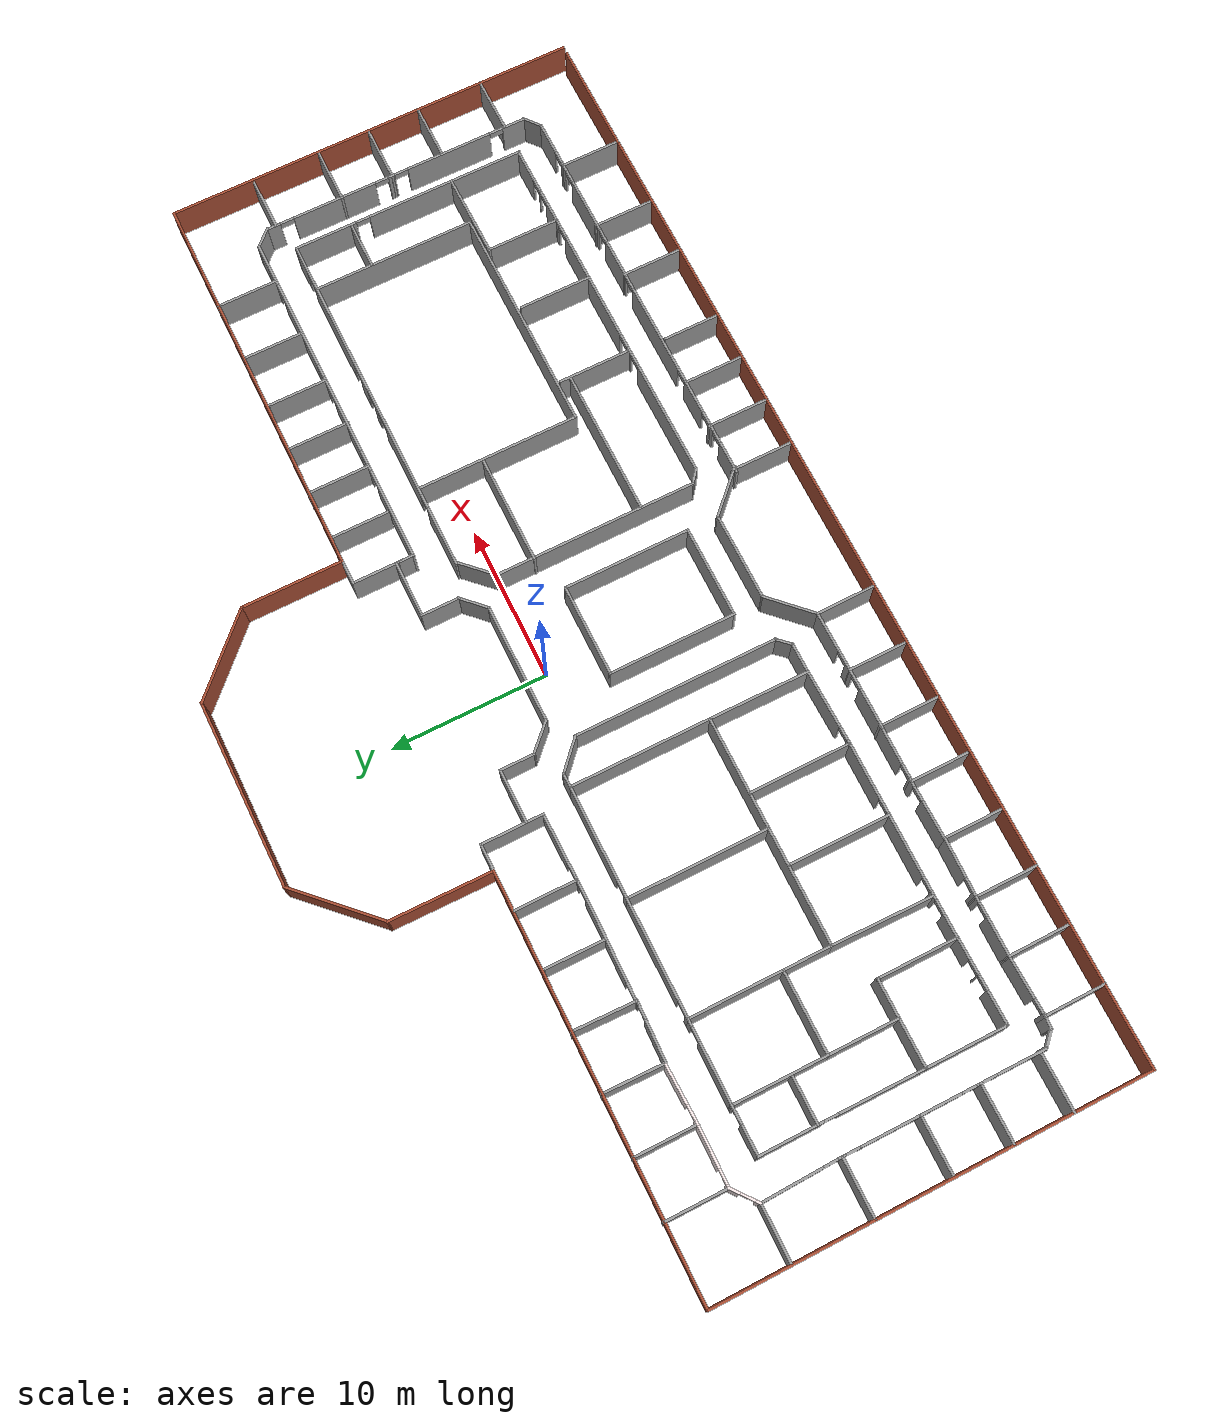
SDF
<?xml version='1.0'?>
<sdf version='1.7'>
  <model name='OEC_2F'>
    <pose>0.733156 -0.285133 0 0 -0 0</pose>
    <link name='Wall_101'>
      <pose>-18.3822 4.28827 0 0 -0 3.12969</pose>
      <visual name='Wall_101_Visual_0'>
        <pose>-0.61431 0 1.25 0 -0 0</pose>
        <geometry>
          <box>
            <size>2.68761 0.15 2.5</size>
          </box>
        </geometry>
        <material>
          <script>
            <uri>file://media/materials/scripts/gazebo.material</uri>
            <name>Gazebo/Grey</name>
          </script>
          <ambient>1 1 1 1</ambient>
        </material>
        <meta>
          <layer>0</layer>
        </meta>
      </visual>
      <collision name='Wall_101_Collision_0'>
        <geometry>
          <box>
            <size>2.68761 0.15 2.5</size>
          </box>
        </geometry>
        <pose>-0.61431 0 1.25 0 -0 0</pose>
      </collision>
      <visual name='Wall_101_Visual_1'>
        <pose>1.7938 0 1.25 0 -0 0</pose>
        <geometry>
          <box>
            <size>0.328619 0.15 2.5</size>
          </box>
        </geometry>
        <material>
          <script>
            <uri>file://media/materials/scripts/gazebo.material</uri>
            <name>Gazebo/Grey</name>
          </script>
          <ambient>1 1 1 1</ambient>
        </material>
        <meta>
          <layer>0</layer>
        </meta>
      </visual>
      <collision name='Wall_101_Collision_1'>
        <geometry>
          <box>
            <size>0.328619 0.15 2.5</size>
          </box>
        </geometry>
        <pose>1.7938 0 1.25 0 -0 0</pose>
      </collision>
      <visual name='Wall_101_Visual_2'>
        <pose>1.17949 0 2.25 0 -0 0</pose>
        <geometry>
          <box>
            <size>0.9 0.15 0.5</size>
          </box>
        </geometry>
        <material>
          <script>
            <uri>file://media/materials/scripts/gazebo.material</uri>
            <name>Gazebo/Grey</name>
          </script>
          <ambient>1 1 1 1</ambient>
        </material>
        <meta>
          <layer>0</layer>
        </meta>
      </visual>
      <collision name='Wall_101_Collision_2'>
        <geometry>
          <box>
            <size>0.9 0.15 0.5</size>
          </box>
        </geometry>
        <pose>1.17949 0 2.25 0 -0 0</pose>
      </collision>
    </link>
    <link name='Wall_102'>
      <pose>-22.0485 4.31707 0 0 -0 3.11269</pose>
      <visual name='Wall_102_Visual_0'>
        <pose>-1.73863 0 1.25 0 -0 0</pose>
        <geometry>
          <box>
            <size>0.333949 0.15 2.5</size>
          </box>
        </geometry>
        <material>
          <script>
            <uri>file://media/materials/scripts/gazebo.material</uri>
            <name>Gazebo/Grey</name>
          </script>
          <ambient>1 1 1 1</ambient>
        </material>
        <meta>
          <layer>0</layer>
        </meta>
      </visual>
      <collision name='Wall_102_Collision_0'>
        <geometry>
          <box>
            <size>0.333949 0.15 2.5</size>
          </box>
        </geometry>
        <pose>-1.73863 0 1.25 0 -0 0</pose>
      </collision>
      <visual name='Wall_102_Visual_1'>
        <pose>0.616975 0 1.25 0 -0 0</pose>
        <geometry>
          <box>
            <size>2.57727 0.15 2.5</size>
          </box>
        </geometry>
        <material>
          <script>
            <uri>file://media/materials/scripts/gazebo.material</uri>
            <name>Gazebo/Grey</name>
          </script>
          <ambient>1 1 1 1</ambient>
        </material>
        <meta>
          <layer>0</layer>
        </meta>
      </visual>
      <collision name='Wall_102_Collision_1'>
        <geometry>
          <box>
            <size>2.57727 0.15 2.5</size>
          </box>
        </geometry>
        <pose>0.616975 0 1.25 0 -0 0</pose>
      </collision>
      <visual name='Wall_102_Visual_2'>
        <pose>-1.12166 0 2.25 0 -0 0</pose>
        <geometry>
          <box>
            <size>0.9 0.15 0.5</size>
          </box>
        </geometry>
        <material>
          <script>
            <uri>file://media/materials/scripts/gazebo.material</uri>
            <name>Gazebo/Grey</name>
          </script>
          <ambient>1 1 1 1</ambient>
        </material>
        <meta>
          <layer>0</layer>
        </meta>
      </visual>
      <collision name='Wall_102_Collision_2'>
        <geometry>
          <box>
            <size>0.9 0.15 0.5</size>
          </box>
        </geometry>
        <pose>-1.12166 0 2.25 0 -0 0</pose>
      </collision>
    </link>
    <link name='Wall_104'>
      <pose>-25.7323 4.36122 0 0 -0 -3.11102</pose>
      <visual name='Wall_104_Visual_0'>
        <pose>-0.610442 0 1.25 0 -0 0</pose>
        <geometry>
          <box>
            <size>2.54565 0.15 2.5</size>
          </box>
        </geometry>
        <material>
          <script>
            <uri>file://media/materials/scripts/gazebo.material</uri>
            <name>Gazebo/Grey</name>
          </script>
          <ambient>0.960784 0.905882 0.905882 1</ambient>
        </material>
        <meta>
          <layer>0</layer>
        </meta>
      </visual>
      <collision name='Wall_104_Collision_0'>
        <geometry>
          <box>
            <size>2.54565 0.15 2.5</size>
          </box>
        </geometry>
        <pose>-0.610442 0 1.25 0 -0 0</pose>
      </collision>
      <visual name='Wall_104_Visual_1'>
        <pose>1.72283 0 1.25 0 -0 0</pose>
        <geometry>
          <box>
            <size>0.320884 0.15 2.5</size>
          </box>
        </geometry>
        <material>
          <script>
            <uri>file://media/materials/scripts/gazebo.material</uri>
            <name>Gazebo/Grey</name>
          </script>
          <ambient>0.960784 0.905882 0.905882 1</ambient>
        </material>
        <meta>
          <layer>0</layer>
        </meta>
      </visual>
      <collision name='Wall_104_Collision_1'>
        <geometry>
          <box>
            <size>0.320884 0.15 2.5</size>
          </box>
        </geometry>
        <pose>1.72283 0 1.25 0 -0 0</pose>
      </collision>
      <visual name='Wall_104_Visual_2'>
        <pose>1.11238 0 2.25 0 -0 0</pose>
        <geometry>
          <box>
            <size>0.9 0.15 0.5</size>
          </box>
        </geometry>
        <material>
          <script>
            <uri>file://media/materials/scripts/gazebo.material</uri>
            <name>Gazebo/Grey</name>
          </script>
          <ambient>0.960784 0.905882 0.905882 1</ambient>
        </material>
        <meta>
          <layer>0</layer>
        </meta>
      </visual>
      <collision name='Wall_104_Collision_2'>
        <geometry>
          <box>
            <size>0.9 0.15 0.5</size>
          </box>
        </geometry>
        <pose>1.11238 0 2.25 0 -0 0</pose>
      </collision>
    </link>
    <link name='Wall_105'>
      <pose>-29.3587 4.32345 0 0 -0 3.13198</pose>
      <visual name='Wall_105_Visual_0'>
        <pose>-0.586662 0 1.25 0 -0 0</pose>
        <geometry>
          <box>
            <size>2.61478 0.15 2.5</size>
          </box>
        </geometry>
        <material>
          <script>
            <uri>file://media/materials/scripts/gazebo.material</uri>
            <name>Gazebo/Grey</name>
          </script>
          <ambient>0.960784 0.905882 0.905882 1</ambient>
        </material>
        <meta>
          <layer>0</layer>
        </meta>
      </visual>
      <collision name='Wall_105_Collision_0'>
        <geometry>
          <box>
            <size>2.61478 0.15 2.5</size>
          </box>
        </geometry>
        <pose>-0.586662 0 1.25 0 -0 0</pose>
      </collision>
      <visual name='Wall_105_Visual_1'>
        <pose>1.75739 0 1.25 0 -0 0</pose>
        <geometry>
          <box>
            <size>0.273323 0.15 2.5</size>
          </box>
        </geometry>
        <material>
          <script>
            <uri>file://media/materials/scripts/gazebo.material</uri>
            <name>Gazebo/Grey</name>
          </script>
          <ambient>0.960784 0.905882 0.905882 1</ambient>
        </material>
        <meta>
          <layer>0</layer>
        </meta>
      </visual>
      <collision name='Wall_105_Collision_1'>
        <geometry>
          <box>
            <size>0.273323 0.15 2.5</size>
          </box>
        </geometry>
        <pose>1.75739 0 1.25 0 -0 0</pose>
      </collision>
      <visual name='Wall_105_Visual_2'>
        <pose>1.17073 0 2.25 0 -0 0</pose>
        <geometry>
          <box>
            <size>0.9 0.15 0.5</size>
          </box>
        </geometry>
        <material>
          <script>
            <uri>file://media/materials/scripts/gazebo.material</uri>
            <name>Gazebo/Grey</name>
          </script>
          <ambient>0.960784 0.905882 0.905882 1</ambient>
        </material>
        <meta>
          <layer>0</layer>
        </meta>
      </visual>
      <collision name='Wall_105_Collision_2'>
        <geometry>
          <box>
            <size>0.9 0.15 0.5</size>
          </box>
        </geometry>
        <pose>1.17073 0 2.25 0 -0 0</pose>
      </collision>
    </link>
    <link name='Wall_107'>
      <pose>-31.8931 3.77384 0 0 -0 -2.47133</pose>
      <visual name='Wall_107_Visual_0'>
        <pose>-0.62608 0 1.25 0 -0 0</pose>
        <geometry>
          <box>
            <size>0.723685 0.15 2.5</size>
          </box>
        </geometry>
        <material>
          <script>
            <uri>file://media/materials/scripts/gazebo.material</uri>
            <name>Gazebo/Grey</name>
          </script>
          <ambient>0.960784 0.905882 0.905882 1</ambient>
        </material>
        <meta>
          <layer>0</layer>
        </meta>
      </visual>
      <collision name='Wall_107_Collision_0'>
        <geometry>
          <box>
            <size>0.723685 0.15 2.5</size>
          </box>
        </geometry>
        <pose>-0.62608 0 1.25 0 -0 0</pose>
      </collision>
      <visual name='Wall_107_Visual_1'>
        <pose>0.811843 0 1.25 0 -0 0</pose>
        <geometry>
          <box>
            <size>0.352159 0.15 2.5</size>
          </box>
        </geometry>
        <material>
          <script>
            <uri>file://media/materials/scripts/gazebo.material</uri>
            <name>Gazebo/Grey</name>
          </script>
          <ambient>0.960784 0.905882 0.905882 1</ambient>
        </material>
        <meta>
          <layer>0</layer>
        </meta>
      </visual>
      <collision name='Wall_107_Collision_1'>
        <geometry>
          <box>
            <size>0.352159 0.15 2.5</size>
          </box>
        </geometry>
        <pose>0.811843 0 1.25 0 -0 0</pose>
      </collision>
      <visual name='Wall_107_Visual_2'>
        <pose>0.185763 0 2.25 0 -0 0</pose>
        <geometry>
          <box>
            <size>0.9 0.15 0.5</size>
          </box>
        </geometry>
        <material>
          <script>
            <uri>file://media/materials/scripts/gazebo.material</uri>
            <name>Gazebo/Grey</name>
          </script>
          <ambient>0.960784 0.905882 0.905882 1</ambient>
        </material>
        <meta>
          <layer>0</layer>
        </meta>
      </visual>
      <collision name='Wall_107_Collision_2'>
        <geometry>
          <box>
            <size>0.9 0.15 0.5</size>
          </box>
        </geometry>
        <pose>0.185763 0 2.25 0 -0 0</pose>
      </collision>
    </link>
    <link name='Wall_109'>
      <collision name='Wall_109_Collision'>
        <geometry>
          <box>
            <size>1 0.15 2.5</size>
          </box>
        </geometry>
        <pose>0 0 1.25 0 -0 0</pose>
      </collision>
      <visual name='Wall_109_Visual'>
        <pose>0 0 1.25 0 -0 0</pose>
        <geometry>
          <box>
            <size>1 0.15 2.5</size>
          </box>
        </geometry>
        <material>
          <script>
            <uri>file://media/materials/scripts/gazebo.material</uri>
            <name>Gazebo/Grey</name>
          </script>
          <ambient>1 1 1 1</ambient>
        </material>
        <meta>
          <layer>0</layer>
        </meta>
      </visual>
      <pose>-7.50932 2.23651 0 0 -0 3.14159</pose>
    </link>
    <link name='Wall_110'>
      <pose>-11.4843 2.23651 0 0 -0 3.14159</pose>
      <visual name='Wall_110_Visual_0'>
        <pose>-0.645977 0 1.25 0 -0 0</pose>
        <geometry>
          <box>
            <size>5.95805 0.15 2.5</size>
          </box>
        </geometry>
        <material>
          <script>
            <uri>file://media/materials/scripts/gazebo.material</uri>
            <name>Gazebo/Grey</name>
          </script>
          <ambient>1 1 1 1</ambient>
        </material>
        <meta>
          <layer>0</layer>
        </meta>
      </visual>
      <collision name='Wall_110_Collision_0'>
        <geometry>
          <box>
            <size>5.95805 0.15 2.5</size>
          </box>
        </geometry>
        <pose>-0.645977 0 1.25 0 -0 0</pose>
      </collision>
      <visual name='Wall_110_Visual_1'>
        <pose>3.42902 0 1.25 0 -0 0</pose>
        <geometry>
          <box>
            <size>0.391954 0.15 2.5</size>
          </box>
        </geometry>
        <material>
          <script>
            <uri>file://media/materials/scripts/gazebo.material</uri>
            <name>Gazebo/Grey</name>
          </script>
          <ambient>1 1 1 1</ambient>
        </material>
        <meta>
          <layer>0</layer>
        </meta>
      </visual>
      <collision name='Wall_110_Collision_1'>
        <geometry>
          <box>
            <size>0.391954 0.15 2.5</size>
          </box>
        </geometry>
        <pose>3.42902 0 1.25 0 -0 0</pose>
      </collision>
      <visual name='Wall_110_Visual_2'>
        <pose>2.78305 0 2.25 0 -0 0</pose>
        <geometry>
          <box>
            <size>0.9 0.15 0.5</size>
          </box>
        </geometry>
        <material>
          <script>
            <uri>file://media/materials/scripts/gazebo.material</uri>
            <name>Gazebo/Grey</name>
          </script>
          <ambient>1 1 1 1</ambient>
        </material>
        <meta>
          <layer>0</layer>
        </meta>
      </visual>
      <collision name='Wall_110_Collision_2'>
        <geometry>
          <box>
            <size>0.9 0.15 0.5</size>
          </box>
        </geometry>
        <pose>2.78305 0 2.25 0 -0 0</pose>
      </collision>
    </link>
    <link name='Wall_111'>
      <pose>-18.7093 2.23651 0 0 -0 3.14159</pose>
      <visual name='Wall_111_Visual_0'>
        <pose>-0.604339 0 1.25 0 -0 0</pose>
        <geometry>
          <box>
            <size>6.29132 0.15 2.5</size>
          </box>
        </geometry>
        <material>
          <script>
            <uri>file://media/materials/scripts/gazebo.material</uri>
            <name>Gazebo/Grey</name>
          </script>
          <ambient>1 1 1 1</ambient>
        </material>
        <meta>
          <layer>0</layer>
        </meta>
      </visual>
      <collision name='Wall_111_Collision_0'>
        <geometry>
          <box>
            <size>6.29132 0.15 2.5</size>
          </box>
        </geometry>
        <pose>-0.604339 0 1.25 0 -0 0</pose>
      </collision>
      <visual name='Wall_111_Visual_1'>
        <pose>3.59566 0 1.25 0 -0 0</pose>
        <geometry>
          <box>
            <size>0.308678 0.15 2.5</size>
          </box>
        </geometry>
        <material>
          <script>
            <uri>file://media/materials/scripts/gazebo.material</uri>
            <name>Gazebo/Grey</name>
          </script>
          <ambient>1 1 1 1</ambient>
        </material>
        <meta>
          <layer>0</layer>
        </meta>
      </visual>
      <collision name='Wall_111_Collision_1'>
        <geometry>
          <box>
            <size>0.308678 0.15 2.5</size>
          </box>
        </geometry>
        <pose>3.59566 0 1.25 0 -0 0</pose>
      </collision>
      <visual name='Wall_111_Visual_2'>
        <pose>2.99132 0 2.25 0 -0 0</pose>
        <geometry>
          <box>
            <size>0.9 0.15 0.5</size>
          </box>
        </geometry>
        <material>
          <script>
            <uri>file://media/materials/scripts/gazebo.material</uri>
            <name>Gazebo/Grey</name>
          </script>
          <ambient>1 1 1 1</ambient>
        </material>
        <meta>
          <layer>0</layer>
        </meta>
      </visual>
      <collision name='Wall_111_Collision_2'>
        <geometry>
          <box>
            <size>0.9 0.15 0.5</size>
          </box>
        </geometry>
        <pose>2.99132 0 2.25 0 -0 0</pose>
      </collision>
    </link>
    <link name='Wall_113'>
      <pose>-24.9343 2.23651 0 0 -0 3.14159</pose>
      <visual name='Wall_113_Visual_0'>
        <pose>-2.35854 0 1.25 0 -0 0</pose>
        <geometry>
          <box>
            <size>0.532918 0.15 2.5</size>
          </box>
        </geometry>
        <material>
          <script>
            <uri>file://media/materials/scripts/gazebo.material</uri>
            <name>Gazebo/Grey</name>
          </script>
          <ambient>1 1 1 1</ambient>
        </material>
        <meta>
          <layer>0</layer>
        </meta>
      </visual>
      <collision name='Wall_113_Collision_0'>
        <geometry>
          <box>
            <size>0.532918 0.15 2.5</size>
          </box>
        </geometry>
        <pose>-2.35854 0 1.25 0 -0 0</pose>
      </collision>
      <visual name='Wall_113_Visual_1'>
        <pose>0.716459 0 1.25 0 -0 0</pose>
        <geometry>
          <box>
            <size>3.81708 0.15 2.5</size>
          </box>
        </geometry>
        <material>
          <script>
            <uri>file://media/materials/scripts/gazebo.material</uri>
            <name>Gazebo/Grey</name>
          </script>
          <ambient>1 1 1 1</ambient>
        </material>
        <meta>
          <layer>0</layer>
        </meta>
      </visual>
      <collision name='Wall_113_Collision_1'>
        <geometry>
          <box>
            <size>3.81708 0.15 2.5</size>
          </box>
        </geometry>
        <pose>0.716459 0 1.25 0 -0 0</pose>
      </collision>
      <visual name='Wall_113_Visual_2'>
        <pose>-1.64208 0 2.25 0 -0 0</pose>
        <geometry>
          <box>
            <size>0.9 0.15 0.5</size>
          </box>
        </geometry>
        <material>
          <script>
            <uri>file://media/materials/scripts/gazebo.material</uri>
            <name>Gazebo/Grey</name>
          </script>
          <ambient>1 1 1 1</ambient>
        </material>
        <meta>
          <layer>0</layer>
        </meta>
      </visual>
      <collision name='Wall_113_Collision_2'>
        <geometry>
          <box>
            <size>0.9 0.15 0.5</size>
          </box>
        </geometry>
        <pose>-1.64208 0 2.25 0 -0 0</pose>
      </collision>
    </link>
    <link name='Wall_115'>
      <pose>-28.9692 2.22462 0 0 -0 -3.13359</pose>
      <visual name='Wall_115_Visual_0'>
        <pose>-1.41288 0 1.25 0 -0 0</pose>
        <geometry>
          <box>
            <size>0.294093 0.15 2.5</size>
          </box>
        </geometry>
        <material>
          <script>
            <uri>file://media/materials/scripts/gazebo.material</uri>
            <name>Gazebo/Grey</name>
          </script>
          <ambient>1 1 1 1</ambient>
        </material>
        <meta>
          <layer>0</layer>
        </meta>
      </visual>
      <collision name='Wall_115_Collision_0'>
        <geometry>
          <box>
            <size>0.294093 0.15 2.5</size>
          </box>
        </geometry>
        <pose>-1.41288 0 1.25 0 -0 0</pose>
      </collision>
      <visual name='Wall_115_Visual_1'>
        <pose>0.597047 0 1.25 0 -0 0</pose>
        <geometry>
          <box>
            <size>1.92576 0.15 2.5</size>
          </box>
        </geometry>
        <material>
          <script>
            <uri>file://media/materials/scripts/gazebo.material</uri>
            <name>Gazebo/Grey</name>
          </script>
          <ambient>1 1 1 1</ambient>
        </material>
        <meta>
          <layer>0</layer>
        </meta>
      </visual>
      <collision name='Wall_115_Collision_1'>
        <geometry>
          <box>
            <size>1.92576 0.15 2.5</size>
          </box>
        </geometry>
        <pose>0.597047 0 1.25 0 -0 0</pose>
      </collision>
      <visual name='Wall_115_Visual_2'>
        <pose>-0.815835 0 2.25 0 -0 0</pose>
        <geometry>
          <box>
            <size>0.9 0.15 0.5</size>
          </box>
        </geometry>
        <material>
          <script>
            <uri>file://media/materials/scripts/gazebo.material</uri>
            <name>Gazebo/Grey</name>
          </script>
          <ambient>1 1 1 1</ambient>
        </material>
        <meta>
          <layer>0</layer>
        </meta>
      </visual>
      <collision name='Wall_115_Collision_2'>
        <geometry>
          <box>
            <size>0.9 0.15 0.5</size>
          </box>
        </geometry>
        <pose>-0.815835 0 2.25 0 -0 0</pose>
      </collision>
    </link>
    <link name='Wall_118'>
      <collision name='Wall_118_Collision'>
        <geometry>
          <box>
            <size>9 0.15 2.5</size>
          </box>
        </geometry>
        <pose>0 0 1.25 0 -0 0</pose>
      </collision>
      <visual name='Wall_118_Visual'>
        <pose>0 0 1.25 0 -0 0</pose>
        <geometry>
          <box>
            <size>9 0.15 2.5</size>
          </box>
        </geometry>
        <material>
          <script>
            <uri>file://media/materials/scripts/gazebo.material</uri>
            <name>Gazebo/Grey</name>
          </script>
          <ambient>1 1 1 1</ambient>
        </material>
        <meta>
          <layer>0</layer>
        </meta>
      </visual>
      <pose>-7.93432 -2.1885 0 0 -0 -1.5708</pose>
    </link>
    <link name='Wall_120'>
      <collision name='Wall_120_Collision'>
        <geometry>
          <box>
            <size>9 0.15 2.5</size>
          </box>
        </geometry>
        <pose>0 0 1.25 0 -0 0</pose>
      </collision>
      <visual name='Wall_120_Visual'>
        <pose>0 0 1.25 0 -0 0</pose>
        <geometry>
          <box>
            <size>9 0.15 2.5</size>
          </box>
        </geometry>
        <material>
          <script>
            <uri>file://media/materials/scripts/gazebo.material</uri>
            <name>Gazebo/Grey</name>
          </script>
          <ambient>1 1 1 1</ambient>
        </material>
        <meta>
          <layer>0</layer>
        </meta>
      </visual>
      <pose>-15.0343 -2.1885 0 0 -0 -1.5708</pose>
    </link>
    <link name='Wall_122'>
      <collision name='Wall_122_Collision'>
        <geometry>
          <box>
            <size>9 0.15 2.5</size>
          </box>
        </geometry>
        <pose>0 0 1.25 0 -0 0</pose>
      </collision>
      <visual name='Wall_122_Visual'>
        <pose>0 0 1.25 0 -0 0</pose>
        <geometry>
          <box>
            <size>9 0.15 2.5</size>
          </box>
        </geometry>
        <material>
          <script>
            <uri>file://media/materials/scripts/gazebo.material</uri>
            <name>Gazebo/Grey</name>
          </script>
          <ambient>1 1 1 1</ambient>
        </material>
        <meta>
          <layer>0</layer>
        </meta>
      </visual>
      <pose>-22.3843 -2.1885 0 0 -0 -1.5708</pose>
    </link>
    <link name='Wall_124'>
      <collision name='Wall_124_Collision'>
        <geometry>
          <box>
            <size>6 0.15 2.5</size>
          </box>
        </geometry>
        <pose>0 0 1.25 0 -0 0</pose>
      </collision>
      <visual name='Wall_124_Visual'>
        <pose>0 0 1.25 0 -0 0</pose>
        <geometry>
          <box>
            <size>6 0.15 2.5</size>
          </box>
        </geometry>
        <material>
          <script>
            <uri>file://media/materials/scripts/gazebo.material</uri>
            <name>Gazebo/Grey</name>
          </script>
          <ambient>1 1 1 1</ambient>
        </material>
        <meta>
          <layer>0</layer>
        </meta>
      </visual>
      <pose>-27.4843 -0.688495 0 0 -0 -1.5708</pose>
    </link>
    <link name='Wall_127'>
      <collision name='Wall_127_Collision'>
        <geometry>
          <box>
            <size>7.25 0.15 2.5</size>
          </box>
        </geometry>
        <pose>0 0 1.25 0 -0 0</pose>
      </collision>
      <visual name='Wall_127_Visual'>
        <pose>0 0 1.25 0 -0 0</pose>
        <geometry>
          <box>
            <size>7.25 0.15 2.5</size>
          </box>
        </geometry>
        <material>
          <script>
            <uri>file://media/materials/scripts/gazebo.material</uri>
            <name>Gazebo/Grey</name>
          </script>
          <ambient>1 1 1 1</ambient>
        </material>
        <meta>
          <layer>0</layer>
        </meta>
      </visual>
      <pose>-11.4843 -6.6135 0 0 -0 3.14159</pose>
    </link>
    <link name='Wall_128'>
      <collision name='Wall_128_Collision'>
        <geometry>
          <box>
            <size>7.5 0.15 2.5</size>
          </box>
        </geometry>
        <pose>0 0 1.25 0 -0 0</pose>
      </collision>
      <visual name='Wall_128_Visual'>
        <pose>0 0 1.25 0 -0 0</pose>
        <geometry>
          <box>
            <size>7.5 0.15 2.5</size>
          </box>
        </geometry>
        <material>
          <script>
            <uri>file://media/materials/scripts/gazebo.material</uri>
            <name>Gazebo/Grey</name>
          </script>
          <ambient>1 1 1 1</ambient>
        </material>
        <meta>
          <layer>0</layer>
        </meta>
      </visual>
      <pose>-18.7093 -6.6135 0 0 -0 3.14159</pose>
    </link>
    <link name='Wall_130'>
      <collision name='Wall_130_Collision'>
        <geometry>
          <box>
            <size>5.25 0.15 2.5</size>
          </box>
        </geometry>
        <pose>0 0 1.25 0 -0 0</pose>
      </collision>
      <visual name='Wall_130_Visual'>
        <pose>0 0 1.25 0 -0 0</pose>
        <geometry>
          <box>
            <size>5.25 0.15 2.5</size>
          </box>
        </geometry>
        <material>
          <script>
            <uri>file://media/materials/scripts/gazebo.material</uri>
            <name>Gazebo/Grey</name>
          </script>
          <ambient>1 1 1 1</ambient>
        </material>
        <meta>
          <layer>0</layer>
        </meta>
      </visual>
      <pose>-24.9343 -3.61349 0 0 -0 0</pose>
    </link>
    <link name='Wall_132'>
      <pose>-32.5386 0.717956 0 0 -0 -1.54269</pose>
      <visual name='Wall_132_Visual_0'>
        <pose>-0.617333 0 1.25 0 -0 0</pose>
        <geometry>
          <box>
            <size>3.89487 0.15 2.5</size>
          </box>
        </geometry>
        <material>
          <script>
            <uri>file://media/materials/scripts/gazebo.material</uri>
            <name>Gazebo/Grey</name>
          </script>
          <ambient>1 1 1 1</ambient>
        </material>
        <meta>
          <layer>0</layer>
        </meta>
      </visual>
      <collision name='Wall_132_Collision_0'>
        <geometry>
          <box>
            <size>3.89487 0.15 2.5</size>
          </box>
        </geometry>
        <pose>-0.617333 0 1.25 0 -0 0</pose>
      </collision>
      <visual name='Wall_132_Visual_1'>
        <pose>2.39744 0 1.25 0 -0 0</pose>
        <geometry>
          <box>
            <size>0.334666 0.15 2.5</size>
          </box>
        </geometry>
        <material>
          <script>
            <uri>file://media/materials/scripts/gazebo.material</uri>
            <name>Gazebo/Grey</name>
          </script>
          <ambient>1 1 1 1</ambient>
        </material>
        <meta>
          <layer>0</layer>
        </meta>
      </visual>
      <collision name='Wall_132_Collision_1'>
        <geometry>
          <box>
            <size>0.334666 0.15 2.5</size>
          </box>
        </geometry>
        <pose>2.39744 0 1.25 0 -0 0</pose>
      </collision>
      <visual name='Wall_132_Visual_2'>
        <pose>1.7801 0 2.25 0 -0 0</pose>
        <geometry>
          <box>
            <size>0.9 0.15 0.5</size>
          </box>
        </geometry>
        <material>
          <script>
            <uri>file://media/materials/scripts/gazebo.material</uri>
            <name>Gazebo/Grey</name>
          </script>
          <ambient>1 1 1 1</ambient>
        </material>
        <meta>
          <layer>0</layer>
        </meta>
      </visual>
      <collision name='Wall_132_Collision_2'>
        <geometry>
          <box>
            <size>0.9 0.15 0.5</size>
          </box>
        </geometry>
        <pose>1.7801 0 2.25 0 -0 0</pose>
      </collision>
    </link>
    <link name='Wall_134'>
      <pose>-32.4686 -4.16702 0 0 -0 -1.5708</pose>
      <visual name='Wall_134_Visual_0'>
        <pose>-2.33578 0 1.25 0 -0 0</pose>
        <geometry>
          <box>
            <size>0.270827 0.15 2.5</size>
          </box>
        </geometry>
        <material>
          <script>
            <uri>file://media/materials/scripts/gazebo.material</uri>
            <name>Gazebo/Grey</name>
          </script>
          <ambient>1 1 1 1</ambient>
        </material>
        <meta>
          <layer>0</layer>
        </meta>
      </visual>
      <collision name='Wall_134_Collision_0'>
        <geometry>
          <box>
            <size>0.270827 0.15 2.5</size>
          </box>
        </geometry>
        <pose>-2.33578 0 1.25 0 -0 0</pose>
      </collision>
      <visual name='Wall_134_Visual_1'>
        <pose>0.585414 0 1.25 0 -0 0</pose>
        <geometry>
          <box>
            <size>3.77156 0.15 2.5</size>
          </box>
        </geometry>
        <material>
          <script>
            <uri>file://media/materials/scripts/gazebo.material</uri>
            <name>Gazebo/Grey</name>
          </script>
          <ambient>1 1 1 1</ambient>
        </material>
        <meta>
          <layer>0</layer>
        </meta>
      </visual>
      <collision name='Wall_134_Collision_1'>
        <geometry>
          <box>
            <size>3.77156 0.15 2.5</size>
          </box>
        </geometry>
        <pose>0.585414 0 1.25 0 -0 0</pose>
      </collision>
      <visual name='Wall_134_Visual_2'>
        <pose>-1.75037 0 2.25 0 -0 0</pose>
        <geometry>
          <box>
            <size>0.9 0.15 0.5</size>
          </box>
        </geometry>
        <material>
          <script>
            <uri>file://media/materials/scripts/gazebo.material</uri>
            <name>Gazebo/Grey</name>
          </script>
          <ambient>1 1 1 1</ambient>
        </material>
        <meta>
          <layer>0</layer>
        </meta>
      </visual>
      <collision name='Wall_134_Collision_2'>
        <geometry>
          <box>
            <size>0.9 0.15 0.5</size>
          </box>
        </geometry>
        <pose>-1.75037 0 2.25 0 -0 0</pose>
      </collision>
    </link>
    <link name='Wall_135'>
      <pose>-32.4686 -8.39202 0 0 -0 -1.5708</pose>
      <visual name='Wall_135_Visual_0'>
        <pose>-0.617157 0 1.25 0 -0 0</pose>
        <geometry>
          <box>
            <size>2.5733 0.15 2.5</size>
          </box>
        </geometry>
        <material>
          <script>
            <uri>file://media/materials/scripts/gazebo.material</uri>
            <name>Gazebo/Grey</name>
          </script>
          <ambient>1 1 1 1</ambient>
        </material>
        <meta>
          <layer>0</layer>
        </meta>
      </visual>
      <collision name='Wall_135_Collision_0'>
        <geometry>
          <box>
            <size>2.5733 0.15 2.5</size>
          </box>
        </geometry>
        <pose>-0.617157 0 1.25 0 -0 0</pose>
      </collision>
      <visual name='Wall_135_Visual_1'>
        <pose>1.73665 0 1.25 0 -0 0</pose>
        <geometry>
          <box>
            <size>0.334313 0.15 2.5</size>
          </box>
        </geometry>
        <material>
          <script>
            <uri>file://media/materials/scripts/gazebo.material</uri>
            <name>Gazebo/Grey</name>
          </script>
          <ambient>1 1 1 1</ambient>
        </material>
        <meta>
          <layer>0</layer>
        </meta>
      </visual>
      <collision name='Wall_135_Collision_1'>
        <geometry>
          <box>
            <size>0.334313 0.15 2.5</size>
          </box>
        </geometry>
        <pose>1.73665 0 1.25 0 -0 0</pose>
      </collision>
      <visual name='Wall_135_Visual_2'>
        <pose>1.11949 0 2.25 0 -0 0</pose>
        <geometry>
          <box>
            <size>0.9 0.15 0.5</size>
          </box>
        </geometry>
        <material>
          <script>
            <uri>file://media/materials/scripts/gazebo.material</uri>
            <name>Gazebo/Grey</name>
          </script>
          <ambient>1 1 1 1</ambient>
        </material>
        <meta>
          <layer>0</layer>
        </meta>
      </visual>
      <collision name='Wall_135_Collision_2'>
        <geometry>
          <box>
            <size>0.9 0.15 0.5</size>
          </box>
        </geometry>
        <pose>1.11949 0 2.25 0 -0 0</pose>
      </collision>
    </link>
    <link name='Wall_137'>
      <pose>-32.4686 -12.2458 0 0 -0 -1.5708</pose>
      <visual name='Wall_137_Visual_0'>
        <pose>-2.00493 0 1.25 0 -0 0</pose>
        <geometry>
          <box>
            <size>0.190132 0.15 2.5</size>
          </box>
        </geometry>
        <material>
          <script>
            <uri>file://media/materials/scripts/gazebo.material</uri>
            <name>Gazebo/Grey</name>
          </script>
          <ambient>1 1 1 1</ambient>
        </material>
        <meta>
          <layer>0</layer>
        </meta>
      </visual>
      <collision name='Wall_137_Collision_0'>
        <geometry>
          <box>
            <size>0.190132 0.15 2.5</size>
          </box>
        </geometry>
        <pose>-2.00493 0 1.25 0 -0 0</pose>
      </collision>
      <visual name='Wall_137_Visual_1'>
        <pose>0.545066 0 1.25 0 -0 0</pose>
        <geometry>
          <box>
            <size>3.10987 0.15 2.5</size>
          </box>
        </geometry>
        <material>
          <script>
            <uri>file://media/materials/scripts/gazebo.material</uri>
            <name>Gazebo/Grey</name>
          </script>
          <ambient>1 1 1 1</ambient>
        </material>
        <meta>
          <layer>0</layer>
        </meta>
      </visual>
      <collision name='Wall_137_Collision_1'>
        <geometry>
          <box>
            <size>3.10987 0.15 2.5</size>
          </box>
        </geometry>
        <pose>0.545066 0 1.25 0 -0 0</pose>
      </collision>
      <visual name='Wall_137_Visual_2'>
        <pose>-1.45987 0 2.25 0 -0 0</pose>
        <geometry>
          <box>
            <size>0.9 0.15 0.5</size>
          </box>
        </geometry>
        <material>
          <script>
            <uri>file://media/materials/scripts/gazebo.material</uri>
            <name>Gazebo/Grey</name>
          </script>
          <ambient>1 1 1 1</ambient>
        </material>
        <meta>
          <layer>0</layer>
        </meta>
      </visual>
      <collision name='Wall_137_Collision_2'>
        <geometry>
          <box>
            <size>0.9 0.15 0.5</size>
          </box>
        </geometry>
        <pose>-1.45987 0 2.25 0 -0 0</pose>
      </collision>
    </link>
    <link name='Wall_139'>
      <collision name='Wall_139_Collision'>
        <geometry>
          <box>
            <size>3.5 0.15 2.5</size>
          </box>
        </geometry>
        <pose>0 0 1.25 0 -0 0</pose>
      </collision>
      <visual name='Wall_139_Visual'>
        <pose>0 0 1.25 0 -0 0</pose>
        <geometry>
          <box>
            <size>3.5 0.15 2.5</size>
          </box>
        </geometry>
        <material>
          <script>
            <uri>file://media/materials/scripts/gazebo.material</uri>
            <name>Gazebo/Grey</name>
          </script>
          <ambient>1 1 1 1</ambient>
        </material>
        <meta>
          <layer>0</layer>
        </meta>
      </visual>
      <pose>-34.2835 3.20674 0 0 -0 3.14159</pose>
    </link>
    <link name='Wall_14'>
      <collision name='Wall_14_Collision'>
        <geometry>
          <box>
            <size>6.57649 0.15 2.5</size>
          </box>
        </geometry>
        <pose>0 0 1.25 0 -0 0</pose>
      </collision>
      <visual name='Wall_14_Visual'>
        <pose>0 0 1.25 0 -0 0</pose>
        <geometry>
          <box>
            <size>6.57649 0.15 2.5</size>
          </box>
        </geometry>
        <material>
          <script>
            <uri>file://media/materials/scripts/gazebo.material</uri>
            <name>Gazebo/Bricks</name>
          </script>
          <ambient>1 1 1 1</ambient>
        </material>
        <meta>
          <layer>0</layer>
        </meta>
      </visual>
      <pose>-10.2885 11.3541 0 0 -0 1.55896</pose>
    </link>
    <link name='Wall_141'>
      <collision name='Wall_141_Collision'>
        <geometry>
          <box>
            <size>3.75 0.15 2.5</size>
          </box>
        </geometry>
        <pose>0 0 1.25 0 -0 0</pose>
      </collision>
      <visual name='Wall_141_Visual'>
        <pose>0 0 1.25 0 -0 0</pose>
        <geometry>
          <box>
            <size>3.75 0.15 2.5</size>
          </box>
        </geometry>
        <material>
          <script>
            <uri>file://media/materials/scripts/gazebo.material</uri>
            <name>Gazebo/Grey</name>
          </script>
          <ambient>1 1 1 1</ambient>
        </material>
        <meta>
          <layer>0</layer>
        </meta>
      </visual>
      <pose>-34.2686 -1.77083 0 0 -0 3.14159</pose>
    </link>
    <link name='Wall_143'>
      <collision name='Wall_143_Collision'>
        <geometry>
          <box>
            <size>3.75 0.15 2.5</size>
          </box>
        </geometry>
        <pose>0 0 1.25 0 -0 0</pose>
      </collision>
      <visual name='Wall_143_Visual'>
        <pose>0 0 1.25 0 -0 0</pose>
        <geometry>
          <box>
            <size>3.75 0.15 2.5</size>
          </box>
        </geometry>
        <material>
          <script>
            <uri>file://media/materials/scripts/gazebo.material</uri>
            <name>Gazebo/Grey</name>
          </script>
          <ambient>1 1 1 1</ambient>
        </material>
        <meta>
          <layer>0</layer>
        </meta>
      </visual>
      <pose>-34.2686 -6.52824 0 0 -0 3.14159</pose>
    </link>
    <link name='Wall_145'>
      <collision name='Wall_145_Collision'>
        <geometry>
          <box>
            <size>3.75 0.15 2.5</size>
          </box>
        </geometry>
        <pose>0 0 1.25 0 -0 0</pose>
      </collision>
      <visual name='Wall_145_Visual'>
        <pose>0 0 1.25 0 -0 0</pose>
        <geometry>
          <box>
            <size>3.75 0.15 2.5</size>
          </box>
        </geometry>
        <material>
          <script>
            <uri>file://media/materials/scripts/gazebo.material</uri>
            <name>Gazebo/Grey</name>
          </script>
          <ambient>1 1 1 1</ambient>
        </material>
        <meta>
          <layer>0</layer>
        </meta>
      </visual>
      <pose>-34.2686 -10.2208 0 0 -0 3.14159</pose>
    </link>
    <link name='Wall_148'>
      <collision name='Wall_148_Collision'>
        <geometry>
          <box>
            <size>3.75 0.15 2.5</size>
          </box>
        </geometry>
        <pose>0 0 1.25 0 -0 0</pose>
      </collision>
      <visual name='Wall_148_Visual'>
        <pose>0 0 1.25 0 -0 0</pose>
        <geometry>
          <box>
            <size>3.75 0.15 2.5</size>
          </box>
        </geometry>
        <material>
          <script>
            <uri>file://media/materials/scripts/gazebo.material</uri>
            <name>Gazebo/Grey</name>
          </script>
          <ambient>1 1 1 1</ambient>
        </material>
        <meta>
          <layer>0</layer>
        </meta>
      </visual>
      <pose>-34.257 -13.9167 0 0 -0 3.14159</pose>
    </link>
    <link name='Wall_15'>
      <collision name='Wall_15_Collision'>
        <geometry>
          <box>
            <size>6.25 0.15 2.5</size>
          </box>
        </geometry>
        <pose>0 0 1.25 0 -0 0</pose>
      </collision>
      <visual name='Wall_15_Visual'>
        <pose>0 0 1.25 0 -0 0</pose>
        <geometry>
          <box>
            <size>6.25 0.15 2.5</size>
          </box>
        </geometry>
        <material>
          <script>
            <uri>file://media/materials/scripts/gazebo.material</uri>
            <name>Gazebo/Bricks</name>
          </script>
          <ambient>1 1 1 1</ambient>
        </material>
        <meta>
          <layer>0</layer>
        </meta>
      </visual>
      <pose>-8.09384 16.7238 0 0 -0 0.785398</pose>
    </link>
    <link name='Wall_150'>
      <collision name='Wall_150_Collision'>
        <geometry>
          <box>
            <size>3.75 0.15 2.5</size>
          </box>
        </geometry>
        <pose>0 0 1.25 0 -0 0</pose>
      </collision>
      <visual name='Wall_150_Visual'>
        <pose>0 0 1.25 0 -0 0</pose>
        <geometry>
          <box>
            <size>3.75 0.15 2.5</size>
          </box>
        </geometry>
        <material>
          <script>
            <uri>file://media/materials/scripts/gazebo.material</uri>
            <name>Gazebo/Grey</name>
          </script>
          <ambient>1 1 1 1</ambient>
        </material>
        <meta>
          <layer>0</layer>
        </meta>
      </visual>
      <pose>-30.4453 0.412732 0 0 -0 -1.56594</pose>
    </link>
    <link name='Wall_151'>
      <pose>-30.4453 -4.68727 0 0 -0 -1.57345</pose>
      <visual name='Wall_151_Visual_0'>
        <pose>-3.14822 0 1.25 0 -0 0</pose>
        <geometry>
          <box>
            <size>0.453553 0.15 2.5</size>
          </box>
        </geometry>
        <material>
          <script>
            <uri>file://media/materials/scripts/gazebo.material</uri>
            <name>Gazebo/Grey</name>
          </script>
          <ambient>1 1 1 1</ambient>
        </material>
        <meta>
          <layer>0</layer>
        </meta>
      </visual>
      <collision name='Wall_151_Collision_0'>
        <geometry>
          <box>
            <size>0.453553 0.15 2.5</size>
          </box>
        </geometry>
        <pose>-3.14822 0 1.25 0 -0 0</pose>
      </collision>
      <visual name='Wall_151_Visual_1'>
        <pose>0.676776 0 1.25 0 -0 0</pose>
        <geometry>
          <box>
            <size>5.39645 0.15 2.5</size>
          </box>
        </geometry>
        <material>
          <script>
            <uri>file://media/materials/scripts/gazebo.material</uri>
            <name>Gazebo/Grey</name>
          </script>
          <ambient>1 1 1 1</ambient>
        </material>
        <meta>
          <layer>0</layer>
        </meta>
      </visual>
      <collision name='Wall_151_Collision_1'>
        <geometry>
          <box>
            <size>5.39645 0.15 2.5</size>
          </box>
        </geometry>
        <pose>0.676776 0 1.25 0 -0 0</pose>
      </collision>
      <visual name='Wall_151_Visual_2'>
        <pose>-2.47145 0 2.25 0 -0 0</pose>
        <geometry>
          <box>
            <size>0.9 0.15 0.5</size>
          </box>
        </geometry>
        <material>
          <script>
            <uri>file://media/materials/scripts/gazebo.material</uri>
            <name>Gazebo/Grey</name>
          </script>
          <ambient>1 1 1 1</ambient>
        </material>
        <meta>
          <layer>0</layer>
        </meta>
      </visual>
      <collision name='Wall_151_Collision_2'>
        <geometry>
          <box>
            <size>0.9 0.15 0.5</size>
          </box>
        </geometry>
        <pose>-2.47145 0 2.25 0 -0 0</pose>
      </collision>
    </link>
    <link name='Wall_153'>
      <collision name='Wall_153_Collision'>
        <geometry>
          <box>
            <size>5.19506 0.15 2.5</size>
          </box>
        </geometry>
        <pose>0 0 1.25 0 -0 0</pose>
      </collision>
      <visual name='Wall_153_Visual'>
        <pose>0 0 1.25 0 -0 0</pose>
        <geometry>
          <box>
            <size>5.19506 0.15 2.5</size>
          </box>
        </geometry>
        <material>
          <script>
            <uri>file://media/materials/scripts/gazebo.material</uri>
            <name>Gazebo/Grey</name>
          </script>
          <ambient>1 1 1 1</ambient>
        </material>
        <meta>
          <layer>0</layer>
        </meta>
      </visual>
      <pose>-30.4541 -10.5098 0 0 -0 -1.5708</pose>
    </link>
    <link name='Wall_155'>
      <collision name='Wall_155_Collision'>
        <geometry>
          <box>
            <size>3 0.15 2.5</size>
          </box>
        </geometry>
        <pose>0 0 1.25 0 -0 0</pose>
      </collision>
      <visual name='Wall_155_Visual'>
        <pose>0 0 1.25 0 -0 0</pose>
        <geometry>
          <box>
            <size>3 0.15 2.5</size>
          </box>
        </geometry>
        <material>
          <script>
            <uri>file://media/materials/scripts/gazebo.material</uri>
            <name>Gazebo/Grey</name>
          </script>
          <ambient>1 1 1 1</ambient>
        </material>
        <meta>
          <layer>0</layer>
        </meta>
      </visual>
      <pose>-29.0116 -1.38727 0 0 -0 0</pose>
    </link>
    <link name='Wall_157'>
      <collision name='Wall_157_Collision'>
        <geometry>
          <box>
            <size>5.5 0.15 2.5</size>
          </box>
        </geometry>
        <pose>0 0 1.25 0 -0 0</pose>
      </collision>
      <visual name='Wall_157_Visual'>
        <pose>0 0 1.25 0 -0 0</pose>
        <geometry>
          <box>
            <size>5.5 0.15 2.5</size>
          </box>
        </geometry>
        <material>
          <script>
            <uri>file://media/materials/scripts/gazebo.material</uri>
            <name>Gazebo/Grey</name>
          </script>
          <ambient>1 1 1 1</ambient>
        </material>
        <meta>
          <layer>0</layer>
        </meta>
      </visual>
      <pose>-27.7791 -7.98727 0 0 -0 0</pose>
    </link>
    <link name='Wall_159'>
      <collision name='Wall_159_Collision'>
        <geometry>
          <box>
            <size>5.14506 0.15 2.5</size>
          </box>
        </geometry>
        <pose>0 0 1.25 0 -0 0</pose>
      </collision>
      <visual name='Wall_159_Visual'>
        <pose>0 0 1.25 0 -0 0</pose>
        <geometry>
          <box>
            <size>5.14506 0.15 2.5</size>
          </box>
        </geometry>
        <material>
          <script>
            <uri>file://media/materials/scripts/gazebo.material</uri>
            <name>Gazebo/Grey</name>
          </script>
          <ambient>1 1 1 1</ambient>
        </material>
        <meta>
          <layer>0</layer>
        </meta>
      </visual>
      <pose>-25.1041 -10.4848 0 0 -0 -1.5708</pose>
    </link>
    <link name='Wall_161'>
      <collision name='Wall_161_Collision'>
        <geometry>
          <box>
            <size>4.5 0.15 2.5</size>
          </box>
        </geometry>
        <pose>0 0 1.25 0 -0 0</pose>
      </collision>
      <visual name='Wall_161_Visual'>
        <pose>0 0 1.25 0 -0 0</pose>
        <geometry>
          <box>
            <size>4.5 0.15 2.5</size>
          </box>
        </geometry>
        <material>
          <script>
            <uri>file://media/materials/scripts/gazebo.material</uri>
            <name>Gazebo/Grey</name>
          </script>
          <ambient>1 1 1 1</ambient>
        </material>
        <meta>
          <layer>0</layer>
        </meta>
      </visual>
      <pose>-27.4843 -5.7885 0 0 -0 -1.5708</pose>
    </link>
    <link name='Wall_164'>
      <collision name='Wall_164_Collision'>
        <geometry>
          <box>
            <size>6.51996 0.15 2.5</size>
          </box>
        </geometry>
        <pose>0 0 1.25 0 -0 0</pose>
      </collision>
      <visual name='Wall_164_Visual'>
        <pose>0 0 1.25 0 -0 0</pose>
        <geometry>
          <box>
            <size>6.51996 0.15 2.5</size>
          </box>
        </geometry>
        <material>
          <script>
            <uri>file://media/materials/scripts/gazebo.material</uri>
            <name>Gazebo/Grey</name>
          </script>
          <ambient>1 1 1 1</ambient>
        </material>
        <meta>
          <layer>0</layer>
        </meta>
      </visual>
      <pose>-22.4442 -9.79791 0 0 -0 -1.5896</pose>
    </link>
    <link name='Wall_165'>
      <pose>-23.8041 -12.9823 0 0 -0 3.14159</pose>
      <visual name='Wall_165_Visual_0'>
        <pose>-1.21215 0 1.25 0 -0 0</pose>
        <geometry>
          <box>
            <size>0.325703 0.15 2.5</size>
          </box>
        </geometry>
        <material>
          <script>
            <uri>file://media/materials/scripts/gazebo.material</uri>
            <name>Gazebo/Grey</name>
          </script>
          <ambient>1 1 1 1</ambient>
        </material>
        <meta>
          <layer>0</layer>
        </meta>
      </visual>
      <collision name='Wall_165_Collision_0'>
        <geometry>
          <box>
            <size>0.325703 0.15 2.5</size>
          </box>
        </geometry>
        <pose>-1.21215 0 1.25 0 -0 0</pose>
      </collision>
      <visual name='Wall_165_Visual_1'>
        <pose>0.612852 0 1.25 0 -0 0</pose>
        <geometry>
          <box>
            <size>1.5243 0.15 2.5</size>
          </box>
        </geometry>
        <material>
          <script>
            <uri>file://media/materials/scripts/gazebo.material</uri>
            <name>Gazebo/Grey</name>
          </script>
          <ambient>1 1 1 1</ambient>
        </material>
        <meta>
          <layer>0</layer>
        </meta>
      </visual>
      <collision name='Wall_165_Collision_1'>
        <geometry>
          <box>
            <size>1.5243 0.15 2.5</size>
          </box>
        </geometry>
        <pose>0.612852 0 1.25 0 -0 0</pose>
      </collision>
      <visual name='Wall_165_Visual_2'>
        <pose>-0.599297 0 2.25 0 -0 0</pose>
        <geometry>
          <box>
            <size>0.9 0.15 0.5</size>
          </box>
        </geometry>
        <material>
          <script>
            <uri>file://media/materials/scripts/gazebo.material</uri>
            <name>Gazebo/Grey</name>
          </script>
          <ambient>1 1 1 1</ambient>
        </material>
        <meta>
          <layer>0</layer>
        </meta>
      </visual>
      <collision name='Wall_165_Collision_2'>
        <geometry>
          <box>
            <size>0.9 0.15 0.5</size>
          </box>
        </geometry>
        <pose>-0.599297 0 2.25 0 -0 0</pose>
      </collision>
    </link>
    <link name='Wall_166'>
      <pose>-27.7791 -13.0248 0 0 -0 -3.13225</pose>
      <visual name='Wall_166_Visual_0'>
        <pose>-2.04239 0 1.25 0 -0 0</pose>
        <geometry>
          <box>
            <size>1.41545 0.15 2.5</size>
          </box>
        </geometry>
        <material>
          <script>
            <uri>file://media/materials/scripts/gazebo.material</uri>
            <name>Gazebo/Grey</name>
          </script>
          <ambient>1 1 1 1</ambient>
        </material>
        <meta>
          <layer>0</layer>
        </meta>
      </visual>
      <collision name='Wall_166_Collision_0'>
        <geometry>
          <box>
            <size>1.41545 0.15 2.5</size>
          </box>
        </geometry>
        <pose>-2.04239 0 1.25 0 -0 0</pose>
      </collision>
      <visual name='Wall_166_Visual_1'>
        <pose>-0.386389 0 1.25 0 -0 0</pose>
        <geometry>
          <box>
            <size>0.096563 0.15 2.5</size>
          </box>
        </geometry>
        <material>
          <script>
            <uri>file://media/materials/scripts/gazebo.material</uri>
            <name>Gazebo/Grey</name>
          </script>
          <ambient>1 1 1 1</ambient>
        </material>
        <meta>
          <layer>0</layer>
        </meta>
      </visual>
      <collision name='Wall_166_Collision_1'>
        <geometry>
          <box>
            <size>0.096563 0.15 2.5</size>
          </box>
        </geometry>
        <pose>-0.386389 0 1.25 0 -0 0</pose>
      </collision>
      <visual name='Wall_166_Visual_2'>
        <pose>1.656 0 1.25 0 -0 0</pose>
        <geometry>
          <box>
            <size>2.18823 0.15 2.5</size>
          </box>
        </geometry>
        <material>
          <script>
            <uri>file://media/materials/scripts/gazebo.material</uri>
            <name>Gazebo/Grey</name>
          </script>
          <ambient>1 1 1 1</ambient>
        </material>
        <meta>
          <layer>0</layer>
        </meta>
      </visual>
      <collision name='Wall_166_Collision_2'>
        <geometry>
          <box>
            <size>2.18823 0.15 2.5</size>
          </box>
        </geometry>
        <pose>1.656 0 1.25 0 -0 0</pose>
      </collision>
      <visual name='Wall_166_Visual_3'>
        <pose>-0.884671 0 2.25 0 -0 0</pose>
        <geometry>
          <box>
            <size>0.9 0.15 0.5</size>
          </box>
        </geometry>
        <material>
          <script>
            <uri>file://media/materials/scripts/gazebo.material</uri>
            <name>Gazebo/Grey</name>
          </script>
          <ambient>1 1 1 1</ambient>
        </material>
        <meta>
          <layer>0</layer>
        </meta>
      </visual>
      <collision name='Wall_166_Collision_3'>
        <geometry>
          <box>
            <size>0.9 0.15 0.5</size>
          </box>
        </geometry>
        <pose>-0.884671 0 2.25 0 -0 0</pose>
      </collision>
      <visual name='Wall_166_Visual_4'>
        <pose>0.111892 0 2.25 0 -0 0</pose>
        <geometry>
          <box>
            <size>0.9 0.15 0.5</size>
          </box>
        </geometry>
        <material>
          <script>
            <uri>file://media/materials/scripts/gazebo.material</uri>
            <name>Gazebo/Grey</name>
          </script>
          <ambient>1 1 1 1</ambient>
        </material>
        <meta>
          <layer>0</layer>
        </meta>
      </visual>
      <collision name='Wall_166_Collision_4'>
        <geometry>
          <box>
            <size>0.9 0.15 0.5</size>
          </box>
        </geometry>
        <pose>0.111892 0 2.25 0 -0 0</pose>
      </collision>
    </link>
    <link name='Wall_168'>
      <collision name='Wall_168_Collision'>
        <geometry>
          <box>
            <size>6.5 0.15 2.5</size>
          </box>
        </geometry>
        <pose>0 0 1.25 0 -0 0</pose>
      </collision>
      <visual name='Wall_168_Visual'>
        <pose>0 0 1.25 0 -0 0</pose>
        <geometry>
          <box>
            <size>6.5 0.15 2.5</size>
          </box>
        </geometry>
        <material>
          <script>
            <uri>file://media/materials/scripts/gazebo.material</uri>
            <name>Gazebo/Grey</name>
          </script>
          <ambient>1 1 1 1</ambient>
        </material>
        <meta>
          <layer>0</layer>
        </meta>
      </visual>
      <pose>-17.3981 -9.8333 0 0 -0 -1.5708</pose>
    </link>
    <link name='Wall_169'>
      <pose>-19.9511 -12.9953 0 0 -0 3.13651</pose>
      <visual name='Wall_169_Visual_0'>
        <pose>-0.629299 0 1.25 0 -0 0</pose>
        <geometry>
          <box>
            <size>3.99747 0.15 2.5</size>
          </box>
        </geometry>
        <material>
          <script>
            <uri>file://media/materials/scripts/gazebo.material</uri>
            <name>Gazebo/Grey</name>
          </script>
          <ambient>1 1 1 1</ambient>
        </material>
        <meta>
          <layer>0</layer>
        </meta>
      </visual>
      <collision name='Wall_169_Collision_0'>
        <geometry>
          <box>
            <size>3.99747 0.15 2.5</size>
          </box>
        </geometry>
        <pose>-0.629299 0 1.25 0 -0 0</pose>
      </collision>
      <visual name='Wall_169_Visual_1'>
        <pose>2.44873 0 1.25 0 -0 0</pose>
        <geometry>
          <box>
            <size>0.358597 0.15 2.5</size>
          </box>
        </geometry>
        <material>
          <script>
            <uri>file://media/materials/scripts/gazebo.material</uri>
            <name>Gazebo/Grey</name>
          </script>
          <ambient>1 1 1 1</ambient>
        </material>
        <meta>
          <layer>0</layer>
        </meta>
      </visual>
      <collision name='Wall_169_Collision_1'>
        <geometry>
          <box>
            <size>0.358597 0.15 2.5</size>
          </box>
        </geometry>
        <pose>2.44873 0 1.25 0 -0 0</pose>
      </collision>
      <visual name='Wall_169_Visual_2'>
        <pose>1.81943 0 2.25 0 -0 0</pose>
        <geometry>
          <box>
            <size>0.9 0.15 0.5</size>
          </box>
        </geometry>
        <material>
          <script>
            <uri>file://media/materials/scripts/gazebo.material</uri>
            <name>Gazebo/Grey</name>
          </script>
          <ambient>1 1 1 1</ambient>
        </material>
        <meta>
          <layer>0</layer>
        </meta>
      </visual>
      <collision name='Wall_169_Collision_2'>
        <geometry>
          <box>
            <size>0.9 0.15 0.5</size>
          </box>
        </geometry>
        <pose>1.81943 0 2.25 0 -0 0</pose>
      </collision>
    </link>
    <link name='Wall_171'>
      <collision name='Wall_171_Collision'>
        <geometry>
          <box>
            <size>6.5 0.15 2.5</size>
          </box>
        </geometry>
        <pose>0 0 1.25 0 -0 0</pose>
      </collision>
      <visual name='Wall_171_Visual'>
        <pose>0 0 1.25 0 -0 0</pose>
        <geometry>
          <box>
            <size>6.5 0.15 2.5</size>
          </box>
        </geometry>
        <material>
          <script>
            <uri>file://media/materials/scripts/gazebo.material</uri>
            <name>Gazebo/Grey</name>
          </script>
          <ambient>1 1 1 1</ambient>
        </material>
        <meta>
          <layer>0</layer>
        </meta>
      </visual>
      <pose>-12.7807 -9.85079 0 0 -0 -1.5708</pose>
    </link>
    <link name='Wall_173'>
      <collision name='Wall_173_Collision'>
        <geometry>
          <box>
            <size>6.46512 0.15 2.5</size>
          </box>
        </geometry>
        <pose>0 0 1.25 0 -0 0</pose>
      </collision>
      <visual name='Wall_173_Visual'>
        <pose>0 0 1.25 0 -0 0</pose>
        <geometry>
          <box>
            <size>6.46512 0.15 2.5</size>
          </box>
        </geometry>
        <material>
          <script>
            <uri>file://media/materials/scripts/gazebo.material</uri>
            <name>Gazebo/Grey</name>
          </script>
          <ambient>1 1 1 1</ambient>
        </material>
        <meta>
          <layer>0</layer>
        </meta>
      </visual>
      <pose>-7.95181 -9.77101 0 0 -0 -1.57634</pose>
    </link>
    <link name='Wall_174'>
      <collision name='Wall_174_Collision'>
        <geometry>
          <box>
            <size>2 0.15 2.5</size>
          </box>
        </geometry>
        <pose>0 0 1.25 0 -0 0</pose>
      </collision>
      <visual name='Wall_174_Visual'>
        <pose>0 0 1.25 0 -0 0</pose>
        <geometry>
          <box>
            <size>2 0.15 2.5</size>
          </box>
        </geometry>
        <material>
          <script>
            <uri>file://media/materials/scripts/gazebo.material</uri>
            <name>Gazebo/Grey</name>
          </script>
          <ambient>1 1 1 1</ambient>
        </material>
        <meta>
          <layer>0</layer>
        </meta>
      </visual>
      <pose>-7.02681 -12.9285 0 0 -0 0</pose>
    </link>
    <link name='Wall_176'>
      <pose>-10.3663 -12.9772 0 0 -0 -3.12145</pose>
      <visual name='Wall_176_Visual_0'>
        <pose>-0.604203 0 1.25 0 -0 0</pose>
        <geometry>
          <box>
            <size>3.77147 0.15 2.5</size>
          </box>
        </geometry>
        <material>
          <script>
            <uri>file://media/materials/scripts/gazebo.material</uri>
            <name>Gazebo/Grey</name>
          </script>
          <ambient>1 1 1 1</ambient>
        </material>
        <meta>
          <layer>0</layer>
        </meta>
      </visual>
      <collision name='Wall_176_Collision_0'>
        <geometry>
          <box>
            <size>3.77147 0.15 2.5</size>
          </box>
        </geometry>
        <pose>-0.604203 0 1.25 0 -0 0</pose>
      </collision>
      <visual name='Wall_176_Visual_1'>
        <pose>2.33574 0 1.25 0 -0 0</pose>
        <geometry>
          <box>
            <size>0.308406 0.15 2.5</size>
          </box>
        </geometry>
        <material>
          <script>
            <uri>file://media/materials/scripts/gazebo.material</uri>
            <name>Gazebo/Grey</name>
          </script>
          <ambient>1 1 1 1</ambient>
        </material>
        <meta>
          <layer>0</layer>
        </meta>
      </visual>
      <collision name='Wall_176_Collision_1'>
        <geometry>
          <box>
            <size>0.308406 0.15 2.5</size>
          </box>
        </geometry>
        <pose>2.33574 0 1.25 0 -0 0</pose>
      </collision>
      <visual name='Wall_176_Visual_2'>
        <pose>1.73153 0 2.25 0 -0 0</pose>
        <geometry>
          <box>
            <size>0.9 0.15 0.5</size>
          </box>
        </geometry>
        <material>
          <script>
            <uri>file://media/materials/scripts/gazebo.material</uri>
            <name>Gazebo/Grey</name>
          </script>
          <ambient>1 1 1 1</ambient>
        </material>
        <meta>
          <layer>0</layer>
        </meta>
      </visual>
      <collision name='Wall_176_Collision_2'>
        <geometry>
          <box>
            <size>0.9 0.15 0.5</size>
          </box>
        </geometry>
        <pose>1.73153 0 2.25 0 -0 0</pose>
      </collision>
    </link>
    <link name='Wall_177'>
      <pose>-15.0894 -13.017 0 0 -0 3.13781</pose>
      <visual name='Wall_177_Visual_0'>
        <pose>-0.568407 0 1.25 0 -0 0</pose>
        <geometry>
          <box>
            <size>3.6306 0.15 2.5</size>
          </box>
        </geometry>
        <material>
          <script>
            <uri>file://media/materials/scripts/gazebo.material</uri>
            <name>Gazebo/Grey</name>
          </script>
          <ambient>1 1 1 1</ambient>
        </material>
        <meta>
          <layer>0</layer>
        </meta>
      </visual>
      <collision name='Wall_177_Collision_0'>
        <geometry>
          <box>
            <size>3.6306 0.15 2.5</size>
          </box>
        </geometry>
        <pose>-0.568407 0 1.25 0 -0 0</pose>
      </collision>
      <visual name='Wall_177_Visual_1'>
        <pose>2.2653 0 1.25 0 -0 0</pose>
        <geometry>
          <box>
            <size>0.236813 0.15 2.5</size>
          </box>
        </geometry>
        <material>
          <script>
            <uri>file://media/materials/scripts/gazebo.material</uri>
            <name>Gazebo/Grey</name>
          </script>
          <ambient>1 1 1 1</ambient>
        </material>
        <meta>
          <layer>0</layer>
        </meta>
      </visual>
      <collision name='Wall_177_Collision_1'>
        <geometry>
          <box>
            <size>0.236813 0.15 2.5</size>
          </box>
        </geometry>
        <pose>2.2653 0 1.25 0 -0 0</pose>
      </collision>
      <visual name='Wall_177_Visual_2'>
        <pose>1.69689 0 2.25 0 -0 0</pose>
        <geometry>
          <box>
            <size>0.9 0.15 0.5</size>
          </box>
        </geometry>
        <material>
          <script>
            <uri>file://media/materials/scripts/gazebo.material</uri>
            <name>Gazebo/Grey</name>
          </script>
          <ambient>1 1 1 1</ambient>
        </material>
        <meta>
          <layer>0</layer>
        </meta>
      </visual>
      <collision name='Wall_177_Collision_2'>
        <geometry>
          <box>
            <size>0.9 0.15 0.5</size>
          </box>
        </geometry>
        <pose>1.69689 0 2.25 0 -0 0</pose>
      </collision>
    </link>
    <link name='Wall_179'>
      <collision name='Wall_179_Collision'>
        <geometry>
          <box>
            <size>3.93068 0.15 2.5</size>
          </box>
        </geometry>
        <pose>0 0 1.25 0 -0 0</pose>
      </collision>
      <visual name='Wall_179_Visual'>
        <pose>0 0 1.25 0 -0 0</pose>
        <geometry>
          <box>
            <size>3.93068 0.15 2.5</size>
          </box>
        </geometry>
        <material>
          <script>
            <uri>file://media/materials/scripts/gazebo.material</uri>
            <name>Gazebo/Grey</name>
          </script>
          <ambient>1 1 1 1</ambient>
        </material>
        <meta>
          <layer>0</layer>
        </meta>
      </visual>
      <pose>-30.9291 -17.0208 0 0 -0 1.57691</pose>
    </link>
    <link name='Wall_18'>
      <collision name='Wall_18_Collision'>
        <geometry>
          <box>
            <size>12 0.15 2.5</size>
          </box>
        </geometry>
        <pose>0 0 1.25 0 -0 0</pose>
      </collision>
      <visual name='Wall_18_Visual'>
        <pose>0 0 1.25 0 -0 0</pose>
        <geometry>
          <box>
            <size>12 0.15 2.5</size>
          </box>
        </geometry>
        <material>
          <script>
            <uri>file://media/materials/scripts/gazebo.material</uri>
            <name>Gazebo/Bricks</name>
          </script>
          <ambient>1 1 1 1</ambient>
        </material>
        <meta>
          <layer>0</layer>
        </meta>
      </visual>
      <pose>-0.012163 18.8805 0 0 -0 0</pose>
    </link>
    <link name='Wall_180'>
      <collision name='Wall_180_Collision'>
        <geometry>
          <box>
            <size>0.904606 0.15 2.5</size>
          </box>
        </geometry>
        <pose>0 0 1.25 0 -0 0</pose>
      </collision>
      <visual name='Wall_180_Visual'>
        <pose>0 0 1.25 0 -0 0</pose>
        <geometry>
          <box>
            <size>0.904606 0.15 2.5</size>
          </box>
        </geometry>
        <material>
          <script>
            <uri>file://media/materials/scripts/gazebo.material</uri>
            <name>Gazebo/Grey</name>
          </script>
          <ambient>1 1 1 1</ambient>
        </material>
        <meta>
          <layer>0</layer>
        </meta>
      </visual>
      <pose>-31.3157 -15.0896 0 0 -0 3.03295</pose>
    </link>
    <link name='Wall_182'>
      <collision name='Wall_182_Collision'>
        <geometry>
          <box>
            <size>3.93068 0.15 2.5</size>
          </box>
        </geometry>
        <pose>0 0 1.25 0 -0 0</pose>
      </collision>
      <visual name='Wall_182_Visual'>
        <pose>0 0 1.25 0 -0 0</pose>
        <geometry>
          <box>
            <size>3.93068 0.15 2.5</size>
          </box>
        </geometry>
        <material>
          <script>
            <uri>file://media/materials/scripts/gazebo.material</uri>
            <name>Gazebo/Grey</name>
          </script>
          <ambient>1 1 1 1</ambient>
        </material>
        <meta>
          <layer>0</layer>
        </meta>
      </visual>
      <pose>-27.2513 -16.9282 0 0 -0 1.57691</pose>
    </link>
    <link name='Wall_183'>
      <pose>-29.1017 -15.0611 0 0 -0 -3.11644</pose>
      <visual name='Wall_183_Visual_0'>
        <pose>-0.569377 0 1.25 0 -0 0</pose>
        <geometry>
          <box>
            <size>2.69018 0.15 2.5</size>
          </box>
        </geometry>
        <material>
          <script>
            <uri>file://media/materials/scripts/gazebo.material</uri>
            <name>Gazebo/Grey</name>
          </script>
          <ambient>1 1 1 1</ambient>
        </material>
        <meta>
          <layer>0</layer>
        </meta>
      </visual>
      <collision name='Wall_183_Collision_0'>
        <geometry>
          <box>
            <size>2.69018 0.15 2.5</size>
          </box>
        </geometry>
        <pose>-0.569377 0 1.25 0 -0 0</pose>
      </collision>
      <visual name='Wall_183_Visual_1'>
        <pose>1.79509 0 1.25 0 -0 0</pose>
        <geometry>
          <box>
            <size>0.238755 0.15 2.5</size>
          </box>
        </geometry>
        <material>
          <script>
            <uri>file://media/materials/scripts/gazebo.material</uri>
            <name>Gazebo/Grey</name>
          </script>
          <ambient>1 1 1 1</ambient>
        </material>
        <meta>
          <layer>0</layer>
        </meta>
      </visual>
      <collision name='Wall_183_Collision_1'>
        <geometry>
          <box>
            <size>0.238755 0.15 2.5</size>
          </box>
        </geometry>
        <pose>1.79509 0 1.25 0 -0 0</pose>
      </collision>
      <visual name='Wall_183_Visual_2'>
        <pose>1.22571 0 2.25 0 -0 0</pose>
        <geometry>
          <box>
            <size>0.9 0.15 0.5</size>
          </box>
        </geometry>
        <material>
          <script>
            <uri>file://media/materials/scripts/gazebo.material</uri>
            <name>Gazebo/Grey</name>
          </script>
          <ambient>1 1 1 1</ambient>
        </material>
        <meta>
          <layer>0</layer>
        </meta>
      </visual>
      <collision name='Wall_183_Collision_2'>
        <geometry>
          <box>
            <size>0.9 0.15 0.5</size>
          </box>
        </geometry>
        <pose>1.22571 0 2.25 0 -0 0</pose>
      </collision>
    </link>
    <link name='Wall_185'>
      <collision name='Wall_185_Collision'>
        <geometry>
          <box>
            <size>4 0.15 2.5</size>
          </box>
        </geometry>
        <pose>0 0 1.25 0 -0 0</pose>
      </collision>
      <visual name='Wall_185_Visual'>
        <pose>0 0 1.25 0 -0 0</pose>
        <geometry>
          <box>
            <size>4 0.15 2.5</size>
          </box>
        </geometry>
        <material>
          <script>
            <uri>file://media/materials/scripts/gazebo.material</uri>
            <name>Gazebo/Grey</name>
          </script>
          <ambient>1 1 1 1</ambient>
        </material>
        <meta>
          <layer>0</layer>
        </meta>
      </visual>
      <pose>-23.6082 -16.9629 0 0 -0 1.5708</pose>
    </link>
    <link name='Wall_186'>
      <pose>-25.4355 -15.0264 0 0 -0 3.13526</pose>
      <visual name='Wall_186_Visual_0'>
        <pose>-1.69379 0 1.25 0 -0 0</pose>
        <geometry>
          <box>
            <size>0.417124 0.15 2.5</size>
          </box>
        </geometry>
        <material>
          <script>
            <uri>file://media/materials/scripts/gazebo.material</uri>
            <name>Gazebo/Grey</name>
          </script>
          <ambient>1 1 1 1</ambient>
        </material>
        <meta>
          <layer>0</layer>
        </meta>
      </visual>
      <collision name='Wall_186_Collision_0'>
        <geometry>
          <box>
            <size>0.417124 0.15 2.5</size>
          </box>
        </geometry>
        <pose>-1.69379 0 1.25 0 -0 0</pose>
      </collision>
      <visual name='Wall_186_Visual_1'>
        <pose>0.658562 0 1.25 0 -0 0</pose>
        <geometry>
          <box>
            <size>2.48759 0.15 2.5</size>
          </box>
        </geometry>
        <material>
          <script>
            <uri>file://media/materials/scripts/gazebo.material</uri>
            <name>Gazebo/Grey</name>
          </script>
          <ambient>1 1 1 1</ambient>
        </material>
        <meta>
          <layer>0</layer>
        </meta>
      </visual>
      <collision name='Wall_186_Collision_1'>
        <geometry>
          <box>
            <size>2.48759 0.15 2.5</size>
          </box>
        </geometry>
        <pose>0.658562 0 1.25 0 -0 0</pose>
      </collision>
      <visual name='Wall_186_Visual_2'>
        <pose>-1.03523 0 2.25 0 -0 0</pose>
        <geometry>
          <box>
            <size>0.9 0.15 0.5</size>
          </box>
        </geometry>
        <material>
          <script>
            <uri>file://media/materials/scripts/gazebo.material</uri>
            <name>Gazebo/Grey</name>
          </script>
          <ambient>1 1 1 1</ambient>
        </material>
        <meta>
          <layer>0</layer>
        </meta>
      </visual>
      <collision name='Wall_186_Collision_2'>
        <geometry>
          <box>
            <size>0.9 0.15 0.5</size>
          </box>
        </geometry>
        <pose>-1.03523 0 2.25 0 -0 0</pose>
      </collision>
    </link>
    <link name='Wall_189'>
      <collision name='Wall_189_Collision'>
        <geometry>
          <box>
            <size>3.8936 0.15 2.5</size>
          </box>
        </geometry>
        <pose>0 0 1.25 0 -0 0</pose>
      </collision>
      <visual name='Wall_189_Visual'>
        <pose>0 0 1.25 0 -0 0</pose>
        <geometry>
          <box>
            <size>3.8936 0.15 2.5</size>
          </box>
        </geometry>
        <material>
          <script>
            <uri>file://media/materials/scripts/gazebo.material</uri>
            <name>Gazebo/Grey</name>
          </script>
          <ambient>1 1 1 1</ambient>
        </material>
        <meta>
          <layer>0</layer>
        </meta>
      </visual>
      <pose>-19.957 -16.9988 0 0 -0 1.5708</pose>
    </link>
    <link name='Wall_19'>
      <collision name='Wall_19_Collision'>
        <geometry>
          <box>
            <size>6.25 0.15 2.5</size>
          </box>
        </geometry>
        <pose>0 0 1.25 0 -0 0</pose>
      </collision>
      <visual name='Wall_19_Visual'>
        <pose>0 0 1.25 0 -0 0</pose>
        <geometry>
          <box>
            <size>6.25 0.15 2.5</size>
          </box>
        </geometry>
        <material>
          <script>
            <uri>file://media/materials/scripts/gazebo.material</uri>
            <name>Gazebo/Bricks</name>
          </script>
          <ambient>1 1 1 1</ambient>
        </material>
        <meta>
          <layer>0</layer>
        </meta>
      </visual>
      <pose>8.06951 16.7238 0 0 -0 -0.785398</pose>
    </link>
    <link name='Wall_190'>
      <pose>-21.7826 -15.0825 0 0 -0 3.1172</pose>
      <visual name='Wall_190_Visual_0'>
        <pose>-0.638658 0 1.25 0 -0 0</pose>
        <geometry>
          <box>
            <size>2.52503 0.15 2.5</size>
          </box>
        </geometry>
        <material>
          <script>
            <uri>file://media/materials/scripts/gazebo.material</uri>
            <name>Gazebo/Grey</name>
          </script>
          <ambient>1 1 1 1</ambient>
        </material>
        <meta>
          <layer>0</layer>
        </meta>
      </visual>
      <collision name='Wall_190_Collision_0'>
        <geometry>
          <box>
            <size>2.52503 0.15 2.5</size>
          </box>
        </geometry>
        <pose>-0.638658 0 1.25 0 -0 0</pose>
      </collision>
      <visual name='Wall_190_Visual_1'>
        <pose>1.71251 0 1.25 0 -0 0</pose>
        <geometry>
          <box>
            <size>0.377317 0.15 2.5</size>
          </box>
        </geometry>
        <material>
          <script>
            <uri>file://media/materials/scripts/gazebo.material</uri>
            <name>Gazebo/Grey</name>
          </script>
          <ambient>1 1 1 1</ambient>
        </material>
        <meta>
          <layer>0</layer>
        </meta>
      </visual>
      <collision name='Wall_190_Collision_1'>
        <geometry>
          <box>
            <size>0.377317 0.15 2.5</size>
          </box>
        </geometry>
        <pose>1.71251 0 1.25 0 -0 0</pose>
      </collision>
      <visual name='Wall_190_Visual_2'>
        <pose>1.07386 0 2.25 0 -0 0</pose>
        <geometry>
          <box>
            <size>0.9 0.15 0.5</size>
          </box>
        </geometry>
        <material>
          <script>
            <uri>file://media/materials/scripts/gazebo.material</uri>
            <name>Gazebo/Grey</name>
          </script>
          <ambient>1 1 1 1</ambient>
        </material>
        <meta>
          <layer>0</layer>
        </meta>
      </visual>
      <collision name='Wall_190_Collision_2'>
        <geometry>
          <box>
            <size>0.9 0.15 0.5</size>
          </box>
        </geometry>
        <pose>1.07386 0 2.25 0 -0 0</pose>
      </collision>
    </link>
    <link name='Wall_192'>
      <collision name='Wall_192_Collision'>
        <geometry>
          <box>
            <size>3.7767 0.15 2.5</size>
          </box>
        </geometry>
        <pose>0 0 1.25 0 -0 0</pose>
      </collision>
      <visual name='Wall_192_Visual'>
        <pose>0 0 1.25 0 -0 0</pose>
        <geometry>
          <box>
            <size>3.7767 0.15 2.5</size>
          </box>
        </geometry>
        <material>
          <script>
            <uri>file://media/materials/scripts/gazebo.material</uri>
            <name>Gazebo/Grey</name>
          </script>
          <ambient>1 1 1 1</ambient>
        </material>
        <meta>
          <layer>0</layer>
        </meta>
      </visual>
      <pose>-16.2728 -16.8977 0 0 -0 1.57813</pose>
    </link>
    <link name='Wall_193'>
      <pose>-18.1215 -15.0791 0 0 -0 -3.12999</pose>
      <visual name='Wall_193_Visual_0'>
        <pose>-1.71308 0 1.25 0 -0 0</pose>
        <geometry>
          <box>
            <size>0.394916 0.15 2.5</size>
          </box>
        </geometry>
        <material>
          <script>
            <uri>file://media/materials/scripts/gazebo.material</uri>
            <name>Gazebo/Grey</name>
          </script>
          <ambient>1 1 1 1</ambient>
        </material>
        <meta>
          <layer>0</layer>
        </meta>
      </visual>
      <collision name='Wall_193_Collision_0'>
        <geometry>
          <box>
            <size>0.394916 0.15 2.5</size>
          </box>
        </geometry>
        <pose>-1.71308 0 1.25 0 -0 0</pose>
      </collision>
      <visual name='Wall_193_Visual_1'>
        <pose>0.647458 0 1.25 0 -0 0</pose>
        <geometry>
          <box>
            <size>2.52616 0.15 2.5</size>
          </box>
        </geometry>
        <material>
          <script>
            <uri>file://media/materials/scripts/gazebo.material</uri>
            <name>Gazebo/Grey</name>
          </script>
          <ambient>1 1 1 1</ambient>
        </material>
        <meta>
          <layer>0</layer>
        </meta>
      </visual>
      <collision name='Wall_193_Collision_1'>
        <geometry>
          <box>
            <size>2.52616 0.15 2.5</size>
          </box>
        </geometry>
        <pose>0.647458 0 1.25 0 -0 0</pose>
      </collision>
      <visual name='Wall_193_Visual_2'>
        <pose>-1.06562 0 2.25 0 -0 0</pose>
        <geometry>
          <box>
            <size>0.9 0.15 0.5</size>
          </box>
        </geometry>
        <material>
          <script>
            <uri>file://media/materials/scripts/gazebo.material</uri>
            <name>Gazebo/Grey</name>
          </script>
          <ambient>1 1 1 1</ambient>
        </material>
        <meta>
          <layer>0</layer>
        </meta>
      </visual>
      <collision name='Wall_193_Collision_2'>
        <geometry>
          <box>
            <size>0.9 0.15 0.5</size>
          </box>
        </geometry>
        <pose>-1.06562 0 2.25 0 -0 0</pose>
      </collision>
    </link>
    <link name='Wall_195'>
      <collision name='Wall_195_Collision'>
        <geometry>
          <box>
            <size>3.8831 0.15 2.5</size>
          </box>
        </geometry>
        <pose>0 0 1.25 0 -0 0</pose>
      </collision>
      <visual name='Wall_195_Visual'>
        <pose>0 0 1.25 0 -0 0</pose>
        <geometry>
          <box>
            <size>3.8831 0.15 2.5</size>
          </box>
        </geometry>
        <material>
          <script>
            <uri>file://media/materials/scripts/gazebo.material</uri>
            <name>Gazebo/Grey</name>
          </script>
          <ambient>1 1 1 1</ambient>
        </material>
        <meta>
          <layer>0</layer>
        </meta>
      </visual>
      <pose>-12.6552 -16.9509 0 0 -0 1.57792</pose>
    </link>
    <link name='Wall_196'>
      <pose>-14.4906 -15.0977 0 0 -0 3.13418</pose>
      <visual name='Wall_196_Visual_0'>
        <pose>-0.60744 0 1.25 0 -0 0</pose>
        <geometry>
          <box>
            <size>2.52703 0.15 2.5</size>
          </box>
        </geometry>
        <material>
          <script>
            <uri>file://media/materials/scripts/gazebo.material</uri>
            <name>Gazebo/Grey</name>
          </script>
          <ambient>1 1 1 1</ambient>
        </material>
        <meta>
          <layer>0</layer>
        </meta>
      </visual>
      <collision name='Wall_196_Collision_0'>
        <geometry>
          <box>
            <size>2.52703 0.15 2.5</size>
          </box>
        </geometry>
        <pose>-0.60744 0 1.25 0 -0 0</pose>
      </collision>
      <visual name='Wall_196_Visual_1'>
        <pose>1.71352 0 1.25 0 -0 0</pose>
        <geometry>
          <box>
            <size>0.31488 0.15 2.5</size>
          </box>
        </geometry>
        <material>
          <script>
            <uri>file://media/materials/scripts/gazebo.material</uri>
            <name>Gazebo/Grey</name>
          </script>
          <ambient>1 1 1 1</ambient>
        </material>
        <meta>
          <layer>0</layer>
        </meta>
      </visual>
      <collision name='Wall_196_Collision_1'>
        <geometry>
          <box>
            <size>0.31488 0.15 2.5</size>
          </box>
        </geometry>
        <pose>1.71352 0 1.25 0 -0 0</pose>
      </collision>
      <visual name='Wall_196_Visual_2'>
        <pose>1.10608 0 2.25 0 -0 0</pose>
        <geometry>
          <box>
            <size>0.9 0.15 0.5</size>
          </box>
        </geometry>
        <material>
          <script>
            <uri>file://media/materials/scripts/gazebo.material</uri>
            <name>Gazebo/Grey</name>
          </script>
          <ambient>1 1 1 1</ambient>
        </material>
        <meta>
          <layer>0</layer>
        </meta>
      </visual>
      <collision name='Wall_196_Collision_2'>
        <geometry>
          <box>
            <size>0.9 0.15 0.5</size>
          </box>
        </geometry>
        <pose>1.10608 0 2.25 0 -0 0</pose>
      </collision>
    </link>
    <link name='Wall_198'>
      <collision name='Wall_198_Collision'>
        <geometry>
          <box>
            <size>3.75 0.15 2.5</size>
          </box>
        </geometry>
        <pose>0 0 1.25 0 -0 0</pose>
      </collision>
      <visual name='Wall_198_Visual'>
        <pose>0 0 1.25 0 -0 0</pose>
        <geometry>
          <box>
            <size>3.75 0.15 2.5</size>
          </box>
        </geometry>
        <material>
          <script>
            <uri>file://media/materials/scripts/gazebo.material</uri>
            <name>Gazebo/Grey</name>
          </script>
          <ambient>1 1 1 1</ambient>
        </material>
        <meta>
          <layer>0</layer>
        </meta>
      </visual>
      <pose>-8.94448 -16.9376 0 0 -0 1.5708</pose>
    </link>
    <link name='Wall_199'>
      <pose>-10.8695 -15.1376 0 0 -0 3.14159</pose>
      <visual name='Wall_199_Visual_0'>
        <pose>-1.7885 0 1.25 0 -0 0</pose>
        <geometry>
          <box>
            <size>0.423006 0.15 2.5</size>
          </box>
        </geometry>
        <material>
          <script>
            <uri>file://media/materials/scripts/gazebo.material</uri>
            <name>Gazebo/Grey</name>
          </script>
          <ambient>1 1 1 1</ambient>
        </material>
        <meta>
          <layer>0</layer>
        </meta>
      </visual>
      <collision name='Wall_199_Collision_0'>
        <geometry>
          <box>
            <size>0.423006 0.15 2.5</size>
          </box>
        </geometry>
        <pose>-1.7885 0 1.25 0 -0 0</pose>
      </collision>
      <visual name='Wall_199_Visual_1'>
        <pose>0.661503 0 1.25 0 -0 0</pose>
        <geometry>
          <box>
            <size>2.67699 0.15 2.5</size>
          </box>
        </geometry>
        <material>
          <script>
            <uri>file://media/materials/scripts/gazebo.material</uri>
            <name>Gazebo/Grey</name>
          </script>
          <ambient>1 1 1 1</ambient>
        </material>
        <meta>
          <layer>0</layer>
        </meta>
      </visual>
      <collision name='Wall_199_Collision_1'>
        <geometry>
          <box>
            <size>2.67699 0.15 2.5</size>
          </box>
        </geometry>
        <pose>0.661503 0 1.25 0 -0 0</pose>
      </collision>
      <visual name='Wall_199_Visual_2'>
        <pose>-1.12699 0 2.25 0 -0 0</pose>
        <geometry>
          <box>
            <size>0.9 0.15 0.5</size>
          </box>
        </geometry>
        <material>
          <script>
            <uri>file://media/materials/scripts/gazebo.material</uri>
            <name>Gazebo/Grey</name>
          </script>
          <ambient>1 1 1 1</ambient>
        </material>
        <meta>
          <layer>0</layer>
        </meta>
      </visual>
      <collision name='Wall_199_Collision_2'>
        <geometry>
          <box>
            <size>0.9 0.15 0.5</size>
          </box>
        </geometry>
        <pose>-1.12699 0 2.25 0 -0 0</pose>
      </collision>
    </link>
    <link name='Wall_2'>
      <collision name='Wall_2_Collision'>
        <geometry>
          <box>
            <size>27.1871 0.15 2.5</size>
          </box>
        </geometry>
        <pose>0 0 1.25 0 -0 0</pose>
      </collision>
      <visual name='Wall_2_Visual'>
        <pose>0 0 1.25 0 -0 0</pose>
        <geometry>
          <box>
            <size>27.1871 0.15 2.5</size>
          </box>
        </geometry>
        <material>
          <script>
            <uri>file://media/materials/scripts/gazebo.material</uri>
            <name>Gazebo/Bricks</name>
          </script>
          <ambient>1 1 1 1</ambient>
        </material>
        <meta>
          <layer>0</layer>
        </meta>
      </visual>
      <pose>-36.0698 -5.37747 0 0 -0 -1.56872</pose>
    </link>
    <link name='Wall_20'>
      <collision name='Wall_20_Collision'>
        <geometry>
          <box>
            <size>6.5575 0.15 2.5</size>
          </box>
        </geometry>
        <pose>0 0 1.25 0 -0 0</pose>
      </collision>
      <visual name='Wall_20_Visual'>
        <pose>0 0 1.25 0 -0 0</pose>
        <geometry>
          <box>
            <size>6.5575 0.15 2.5</size>
          </box>
        </geometry>
        <material>
          <script>
            <uri>file://media/materials/scripts/gazebo.material</uri>
            <name>Gazebo/Bricks</name>
          </script>
          <ambient>1 1 1 1</ambient>
        </material>
        <meta>
          <layer>0</layer>
        </meta>
      </visual>
      <pose>10.2262 11.3634 0 0 -0 -1.5708</pose>
    </link>
    <link name='Wall_201'>
      <collision name='Wall_201_Collision'>
        <geometry>
          <box>
            <size>3.82289 0.15 2.5</size>
          </box>
        </geometry>
        <pose>0 0 1.25 0 -0 0</pose>
      </collision>
      <visual name='Wall_201_Visual'>
        <pose>0 0 1.25 0 -0 0</pose>
        <geometry>
          <box>
            <size>3.82289 0.15 2.5</size>
          </box>
        </geometry>
        <material>
          <script>
            <uri>file://media/materials/scripts/gazebo.material</uri>
            <name>Gazebo/Grey</name>
          </script>
          <ambient>1 1 1 1</ambient>
        </material>
        <meta>
          <layer>0</layer>
        </meta>
      </visual>
      <pose>-5.10068 -16.9544 0 0 -0 1.578</pose>
    </link>
    <link name='Wall_202'>
      <pose>-7.02919 -15.1278 0 0 -0 -3.13648</pose>
      <visual name='Wall_202_Visual_0'>
        <pose>-0.701443 0 1.25 0 -0 0</pose>
        <geometry>
          <box>
            <size>2.57774 0.15 2.5</size>
          </box>
        </geometry>
        <material>
          <script>
            <uri>file://media/materials/scripts/gazebo.material</uri>
            <name>Gazebo/Grey</name>
          </script>
          <ambient>1 1 1 1</ambient>
        </material>
        <meta>
          <layer>0</layer>
        </meta>
      </visual>
      <collision name='Wall_202_Collision_0'>
        <geometry>
          <box>
            <size>2.57774 0.15 2.5</size>
          </box>
        </geometry>
        <pose>-0.701443 0 1.25 0 -0 0</pose>
      </collision>
      <visual name='Wall_202_Visual_1'>
        <pose>1.73887 0 1.25 0 -0 0</pose>
        <geometry>
          <box>
            <size>0.502885 0.15 2.5</size>
          </box>
        </geometry>
        <material>
          <script>
            <uri>file://media/materials/scripts/gazebo.material</uri>
            <name>Gazebo/Grey</name>
          </script>
          <ambient>1 1 1 1</ambient>
        </material>
        <meta>
          <layer>0</layer>
        </meta>
      </visual>
      <collision name='Wall_202_Collision_1'>
        <geometry>
          <box>
            <size>0.502885 0.15 2.5</size>
          </box>
        </geometry>
        <pose>1.73887 0 1.25 0 -0 0</pose>
      </collision>
      <visual name='Wall_202_Visual_2'>
        <pose>1.03743 0 2.25 0 -0 0</pose>
        <geometry>
          <box>
            <size>0.9 0.15 0.5</size>
          </box>
        </geometry>
        <material>
          <script>
            <uri>file://media/materials/scripts/gazebo.material</uri>
            <name>Gazebo/Grey</name>
          </script>
          <ambient>1 1 1 1</ambient>
        </material>
        <meta>
          <layer>0</layer>
        </meta>
      </visual>
      <collision name='Wall_202_Collision_2'>
        <geometry>
          <box>
            <size>0.9 0.15 0.5</size>
          </box>
        </geometry>
        <pose>1.03743 0 2.25 0 -0 0</pose>
      </collision>
    </link>
    <link name='Wall_204'>
      <collision name='Wall_204_Collision'>
        <geometry>
          <box>
            <size>3.75 0.15 2.5</size>
          </box>
        </geometry>
        <pose>0 0 1.25 0 -0 0</pose>
      </collision>
      <visual name='Wall_204_Visual'>
        <pose>0 0 1.25 0 -0 0</pose>
        <geometry>
          <box>
            <size>3.75 0.15 2.5</size>
          </box>
        </geometry>
        <material>
          <script>
            <uri>file://media/materials/scripts/gazebo.material</uri>
            <name>Gazebo/Grey</name>
          </script>
          <ambient>1 1 1 1</ambient>
        </material>
        <meta>
          <layer>0</layer>
        </meta>
      </visual>
      <pose>11.8531 6.30778 0 0 -0 -1.5708</pose>
    </link>
    <link name='Wall_206'>
      <collision name='Wall_206_Collision'>
        <geometry>
          <box>
            <size>4 0.15 2.5</size>
          </box>
        </geometry>
        <pose>0 0 1.25 0 -0 0</pose>
      </collision>
      <visual name='Wall_206_Visual'>
        <pose>0 0 1.25 0 -0 0</pose>
        <geometry>
          <box>
            <size>4 0.15 2.5</size>
          </box>
        </geometry>
        <material>
          <script>
            <uri>file://media/materials/scripts/gazebo.material</uri>
            <name>Gazebo/Grey</name>
          </script>
          <ambient>1 1 1 1</ambient>
        </material>
        <meta>
          <layer>0</layer>
        </meta>
      </visual>
      <pose>15.0544 6.25314 0 0 -0 -1.5708</pose>
    </link>
    <link name='Wall_208'>
      <collision name='Wall_208_Collision'>
        <geometry>
          <box>
            <size>4 0.15 2.5</size>
          </box>
        </geometry>
        <pose>0 0 1.25 0 -0 0</pose>
      </collision>
      <visual name='Wall_208_Visual'>
        <pose>0 0 1.25 0 -0 0</pose>
        <geometry>
          <box>
            <size>4 0.15 2.5</size>
          </box>
        </geometry>
        <material>
          <script>
            <uri>file://media/materials/scripts/gazebo.material</uri>
            <name>Gazebo/Grey</name>
          </script>
          <ambient>1 1 1 1</ambient>
        </material>
        <meta>
          <layer>0</layer>
        </meta>
      </visual>
      <pose>18.1853 6.18278 0 0 -0 -1.5708</pose>
    </link>
    <link name='Wall_210'>
      <collision name='Wall_210_Collision'>
        <geometry>
          <box>
            <size>3.75 0.15 2.5</size>
          </box>
        </geometry>
        <pose>0 0 1.25 0 -0 0</pose>
      </collision>
      <visual name='Wall_210_Visual'>
        <pose>0 0 1.25 0 -0 0</pose>
        <geometry>
          <box>
            <size>3.75 0.15 2.5</size>
          </box>
        </geometry>
        <material>
          <script>
            <uri>file://media/materials/scripts/gazebo.material</uri>
            <name>Gazebo/Grey</name>
          </script>
          <ambient>1 1 1 1</ambient>
        </material>
        <meta>
          <layer>0</layer>
        </meta>
      </visual>
      <pose>21.3514 6.16707 0 0 -0 -1.5708</pose>
    </link>
    <link name='Wall_212'>
      <collision name='Wall_212_Collision'>
        <geometry>
          <box>
            <size>4 0.15 2.5</size>
          </box>
        </geometry>
        <pose>0 0 1.25 0 -0 0</pose>
      </collision>
      <visual name='Wall_212_Visual'>
        <pose>0 0 1.25 0 -0 0</pose>
        <geometry>
          <box>
            <size>4 0.15 2.5</size>
          </box>
        </geometry>
        <material>
          <script>
            <uri>file://media/materials/scripts/gazebo.material</uri>
            <name>Gazebo/Grey</name>
          </script>
          <ambient>1 1 1 1</ambient>
        </material>
        <meta>
          <layer>0</layer>
        </meta>
      </visual>
      <pose>24.9044 6.21796 0 0 -0 -1.5708</pose>
    </link>
    <link name='Wall_214'>
      <collision name='Wall_214_Collision'>
        <geometry>
          <box>
            <size>4 0.15 2.5</size>
          </box>
        </geometry>
        <pose>0 0 1.25 0 -0 0</pose>
      </collision>
      <visual name='Wall_214_Visual'>
        <pose>0 0 1.25 0 -0 0</pose>
        <geometry>
          <box>
            <size>4 0.15 2.5</size>
          </box>
        </geometry>
        <material>
          <script>
            <uri>file://media/materials/scripts/gazebo.material</uri>
            <name>Gazebo/Grey</name>
          </script>
          <ambient>1 1 1 1</ambient>
        </material>
        <meta>
          <layer>0</layer>
        </meta>
      </visual>
      <pose>28.8796 6.21796 0 0 -0 -1.5708</pose>
    </link>
    <link name='Wall_218'>
      <collision name='Wall_218_Collision'>
        <geometry>
          <box>
            <size>10.5 0.15 2.5</size>
          </box>
        </geometry>
        <pose>0 0 1.25 0 -0 0</pose>
      </collision>
      <visual name='Wall_218_Visual'>
        <pose>0 0 1.25 0 -0 0</pose>
        <geometry>
          <box>
            <size>10.5 0.15 2.5</size>
          </box>
        </geometry>
        <material>
          <script>
            <uri>file://media/materials/scripts/gazebo.material</uri>
            <name>Gazebo/Grey</name>
          </script>
          <ambient>1 1 1 1</ambient>
        </material>
        <meta>
          <layer>0</layer>
        </meta>
      </visual>
      <pose>12.3906 -2.92021 0 0 -0 -1.5708</pose>
    </link>
    <link name='Wall_219'>
      <collision name='Wall_219_Collision'>
        <geometry>
          <box>
            <size>15 0.15 2.5</size>
          </box>
        </geometry>
        <pose>0 0 1.25 0 -0 0</pose>
      </collision>
      <visual name='Wall_219_Visual'>
        <pose>0 0 1.25 0 -0 0</pose>
        <geometry>
          <box>
            <size>15 0.15 2.5</size>
          </box>
        </geometry>
        <material>
          <script>
            <uri>file://media/materials/scripts/gazebo.material</uri>
            <name>Gazebo/Grey</name>
          </script>
          <ambient>1 1 1 1</ambient>
        </material>
        <meta>
          <layer>0</layer>
        </meta>
      </visual>
      <pose>19.8156 -8.09521 0 0 -0 0</pose>
    </link>
    <link name='Wall_220'>
      <collision name='Wall_220_Collision'>
        <geometry>
          <box>
            <size>10.5 0.15 2.5</size>
          </box>
        </geometry>
        <pose>0 0 1.25 0 -0 0</pose>
      </collision>
      <visual name='Wall_220_Visual'>
        <pose>0 0 1.25 0 -0 0</pose>
        <geometry>
          <box>
            <size>10.5 0.15 2.5</size>
          </box>
        </geometry>
        <material>
          <script>
            <uri>file://media/materials/scripts/gazebo.material</uri>
            <name>Gazebo/Grey</name>
          </script>
          <ambient>1 1 1 1</ambient>
        </material>
        <meta>
          <layer>0</layer>
        </meta>
      </visual>
      <pose>27.2406 -2.92021 0 0 -0 1.5708</pose>
    </link>
    <link name='Wall_222'>
      <collision name='Wall_222_Collision'>
        <geometry>
          <box>
            <size>3.25 0.15 2.5</size>
          </box>
        </geometry>
        <pose>0 0 1.25 0 -0 0</pose>
      </collision>
      <visual name='Wall_222_Visual'>
        <pose>0 0 1.25 0 -0 0</pose>
        <geometry>
          <box>
            <size>3.25 0.15 2.5</size>
          </box>
        </geometry>
        <material>
          <script>
            <uri>file://media/materials/scripts/gazebo.material</uri>
            <name>Gazebo/Grey</name>
          </script>
          <ambient>1 1 1 1</ambient>
        </material>
        <meta>
          <layer>0</layer>
        </meta>
      </visual>
      <pose>28.8075 -1.41603 0 0 -0 0</pose>
    </link>
    <link name='Wall_224'>
      <collision name='Wall_224_Collision'>
        <geometry>
          <box>
            <size>5.62083 0.15 2.5</size>
          </box>
        </geometry>
        <pose>0 0 1.25 0 -0 0</pose>
      </collision>
      <visual name='Wall_224_Visual'>
        <pose>0 0 1.25 0 -0 0</pose>
        <geometry>
          <box>
            <size>5.62083 0.15 2.5</size>
          </box>
        </geometry>
        <material>
          <script>
            <uri>file://media/materials/scripts/gazebo.material</uri>
            <name>Gazebo/Grey</name>
          </script>
          <ambient>1 1 1 1</ambient>
        </material>
        <meta>
          <layer>0</layer>
        </meta>
      </visual>
      <pose>27.6729 -8.31895 0 0 -0 -3.13424</pose>
    </link>
    <link name='Wall_226'>
      <collision name='Wall_226_Collision'>
        <geometry>
          <box>
            <size>7 0.15 2.5</size>
          </box>
        </geometry>
        <pose>0 0 1.25 0 -0 0</pose>
      </collision>
      <visual name='Wall_226_Visual'>
        <pose>0 0 1.25 0 -0 0</pose>
        <geometry>
          <box>
            <size>7 0.15 2.5</size>
          </box>
        </geometry>
        <material>
          <script>
            <uri>file://media/materials/scripts/gazebo.material</uri>
            <name>Gazebo/Grey</name>
          </script>
          <ambient>1 1 1 1</ambient>
        </material>
        <meta>
          <layer>0</layer>
        </meta>
      </visual>
      <pose>8.77988 -1.93607 0 0 -0 0</pose>
    </link>
    <link name='Wall_228'>
      <collision name='Wall_228_Collision'>
        <geometry>
          <box>
            <size>9.5 0.15 2.5</size>
          </box>
        </geometry>
        <pose>0 0 1.25 0 -0 0</pose>
      </collision>
      <visual name='Wall_228_Visual'>
        <pose>0 0 1.25 0 -0 0</pose>
        <geometry>
          <box>
            <size>9.5 0.15 2.5</size>
          </box>
        </geometry>
        <material>
          <script>
            <uri>file://media/materials/scripts/gazebo.material</uri>
            <name>Gazebo/Grey</name>
          </script>
          <ambient>1 1 1 1</ambient>
        </material>
        <meta>
          <layer>0</layer>
        </meta>
      </visual>
      <pose>10.0911 -8.97182 0 0 -0 0</pose>
    </link>
    <link name='Wall_23'>
      <collision name='Wall_23_Collision'>
        <geometry>
          <box>
            <size>4 0.15 2.5</size>
          </box>
        </geometry>
        <pose>0 0 1.25 0 -0 0</pose>
      </collision>
      <visual name='Wall_23_Visual'>
        <pose>0 0 1.25 0 -0 0</pose>
        <geometry>
          <box>
            <size>4 0.15 2.5</size>
          </box>
        </geometry>
        <material>
          <script>
            <uri>file://media/materials/scripts/gazebo.material</uri>
            <name>Gazebo/Grey</name>
          </script>
          <ambient>1 1 1 1</ambient>
        </material>
        <meta>
          <layer>0</layer>
        </meta>
      </visual>
      <pose>-8.664 6.20876 0 0 -0 1.5708</pose>
    </link>
    <link name='Wall_230'>
      <collision name='Wall_230_Collision'>
        <geometry>
          <box>
            <size>3.5 0.15 2.5</size>
          </box>
        </geometry>
        <pose>0 0 1.25 0 -0 0</pose>
      </collision>
      <visual name='Wall_230_Visual'>
        <pose>0 0 1.25 0 -0 0</pose>
        <geometry>
          <box>
            <size>3.5 0.15 2.5</size>
          </box>
        </geometry>
        <material>
          <script>
            <uri>file://media/materials/scripts/gazebo.material</uri>
            <name>Gazebo/Grey</name>
          </script>
          <ambient>1 1 1 1</ambient>
        </material>
        <meta>
          <layer>0</layer>
        </meta>
      </visual>
      <pose>34.1634 2.77483 0 0 -0 0</pose>
    </link>
    <link name='Wall_232'>
      <collision name='Wall_232_Collision'>
        <geometry>
          <box>
            <size>3.75 0.15 2.5</size>
          </box>
        </geometry>
        <pose>0 0 1.25 0 -0 0</pose>
      </collision>
      <visual name='Wall_232_Visual'>
        <pose>0 0 1.25 0 -0 0</pose>
        <geometry>
          <box>
            <size>3.75 0.15 2.5</size>
          </box>
        </geometry>
        <material>
          <script>
            <uri>file://media/materials/scripts/gazebo.material</uri>
            <name>Gazebo/Grey</name>
          </script>
          <ambient>1 1 1 1</ambient>
        </material>
        <meta>
          <layer>0</layer>
        </meta>
      </visual>
      <pose>34.2272 -1.69135 0 0 -0 0</pose>
    </link>
    <link name='Wall_234'>
      <collision name='Wall_234_Collision'>
        <geometry>
          <box>
            <size>3.75 0.15 2.5</size>
          </box>
        </geometry>
        <pose>0 0 1.25 0 -0 0</pose>
      </collision>
      <visual name='Wall_234_Visual'>
        <pose>0 0 1.25 0 -0 0</pose>
        <geometry>
          <box>
            <size>3.75 0.15 2.5</size>
          </box>
        </geometry>
        <material>
          <script>
            <uri>file://media/materials/scripts/gazebo.material</uri>
            <name>Gazebo/Grey</name>
          </script>
          <ambient>1 1 1 1</ambient>
        </material>
        <meta>
          <layer>0</layer>
        </meta>
      </visual>
      <pose>34.2272 -5.14804 0 0 -0 0</pose>
    </link>
    <link name='Wall_238'>
      <collision name='Wall_238_Collision'>
        <geometry>
          <box>
            <size>3.75 0.15 2.5</size>
          </box>
        </geometry>
        <pose>0 0 1.25 0 -0 0</pose>
      </collision>
      <visual name='Wall_238_Visual'>
        <pose>0 0 1.25 0 -0 0</pose>
        <geometry>
          <box>
            <size>3.75 0.15 2.5</size>
          </box>
        </geometry>
        <material>
          <script>
            <uri>file://media/materials/scripts/gazebo.material</uri>
            <name>Gazebo/Grey</name>
          </script>
          <ambient>1 1 1 1</ambient>
        </material>
        <meta>
          <layer>0</layer>
        </meta>
      </visual>
      <pose>34.2981 -12.9791 0 0 -0 3.14159</pose>
    </link>
    <link name='Wall_24'>
      <collision name='Wall_24_Collision'>
        <geometry>
          <box>
            <size>1.81257 0.15 2.5</size>
          </box>
        </geometry>
        <pose>0 0 1.25 0 -0 0</pose>
      </collision>
      <visual name='Wall_24_Visual'>
        <pose>0 0 1.25 0 -0 0</pose>
        <geometry>
          <box>
            <size>1.81257 0.15 2.5</size>
          </box>
        </geometry>
        <material>
          <script>
            <uri>file://media/materials/scripts/gazebo.material</uri>
            <name>Gazebo/Grey</name>
          </script>
          <ambient>1 1 1 1</ambient>
        </material>
        <meta>
          <layer>0</layer>
        </meta>
      </visual>
      <pose>-9.49528 8.13742 0 0 -0 3.1372</pose>
    </link>
    <link name='Wall_240'>
      <collision name='Wall_240_Collision'>
        <geometry>
          <box>
            <size>3.75 0.15 2.5</size>
          </box>
        </geometry>
        <pose>0 0 1.25 0 -0 0</pose>
      </collision>
      <visual name='Wall_240_Visual'>
        <pose>0 0 1.25 0 -0 0</pose>
        <geometry>
          <box>
            <size>3.75 0.15 2.5</size>
          </box>
        </geometry>
        <material>
          <script>
            <uri>file://media/materials/scripts/gazebo.material</uri>
            <name>Gazebo/Grey</name>
          </script>
          <ambient>1 1 1 1</ambient>
        </material>
        <meta>
          <layer>0</layer>
        </meta>
      </visual>
      <pose>34.2981 -8.60474 0 0 -0 3.14159</pose>
    </link>
    <link name='Wall_242'>
      <collision name='Wall_242_Collision'>
        <geometry>
          <box>
            <size>4.75 0.15 2.5</size>
          </box>
        </geometry>
        <pose>0 0 1.25 0 -0 0</pose>
      </collision>
      <visual name='Wall_242_Visual'>
        <pose>0 0 1.25 0 -0 0</pose>
        <geometry>
          <box>
            <size>4.75 0.15 2.5</size>
          </box>
        </geometry>
        <material>
          <script>
            <uri>file://media/materials/scripts/gazebo.material</uri>
            <name>Gazebo/Grey</name>
          </script>
          <ambient>1 1 1 1</ambient>
        </material>
        <meta>
          <layer>0</layer>
        </meta>
      </visual>
      <pose>14.899 -10.6294 0 0 -0 -1.5708</pose>
    </link>
    <link name='Wall_243'>
      <collision name='Wall_243_Collision'>
        <geometry>
          <box>
            <size>0.16 0.15 2.5</size>
          </box>
        </geometry>
        <pose>0 0 1.25 0 -0 0</pose>
      </collision>
      <visual name='Wall_243_Visual'>
        <pose>0 0 1.25 0 -0 0</pose>
        <geometry>
          <box>
            <size>0.16 0.15 2.5</size>
          </box>
        </geometry>
        <material>
          <script>
            <uri>file://media/materials/scripts/gazebo.material</uri>
            <name>Gazebo/Grey</name>
          </script>
          <ambient>0 0 0 1</ambient>
        </material>
        <meta>
          <layer>0</layer>
        </meta>
      </visual>
      <pose>14.904 -12.9294 0 0 -0 0</pose>
    </link>
    <link name='Wall_244'>
      <collision name='Wall_244_Collision'>
        <geometry>
          <box>
            <size>4.75 0.15 2.5</size>
          </box>
        </geometry>
        <pose>0 0 1.25 0 -0 0</pose>
      </collision>
      <visual name='Wall_244_Visual'>
        <pose>0 0 1.25 0 -0 0</pose>
        <geometry>
          <box>
            <size>4.75 0.15 2.5</size>
          </box>
        </geometry>
        <material>
          <script>
            <uri>file://media/materials/scripts/gazebo.material</uri>
            <name>Gazebo/Grey</name>
          </script>
          <ambient>1 1 1 1</ambient>
        </material>
        <meta>
          <layer>0</layer>
        </meta>
      </visual>
      <pose>20.4664 -10.6906 0 0 -0 -1.5708</pose>
    </link>
    <link name='Wall_246'>
      <collision name='Wall_246_Collision'>
        <geometry>
          <box>
            <size>4.75 0.15 2.5</size>
          </box>
        </geometry>
        <pose>0 0 1.25 0 -0 0</pose>
      </collision>
      <visual name='Wall_246_Visual'>
        <pose>0 0 1.25 0 -0 0</pose>
        <geometry>
          <box>
            <size>4.75 0.15 2.5</size>
          </box>
        </geometry>
        <material>
          <script>
            <uri>file://media/materials/scripts/gazebo.material</uri>
            <name>Gazebo/Grey</name>
          </script>
          <ambient>1 1 1 1</ambient>
        </material>
        <meta>
          <layer>0</layer>
        </meta>
      </visual>
      <pose>24.9577 -10.6189 0 0 -0 -1.5708</pose>
    </link>
    <link name='Wall_247'>
      <collision name='Wall_247_Collision'>
        <geometry>
          <box>
            <size>0.286733 0.15 2.5</size>
          </box>
        </geometry>
        <pose>0 0 1.25 0 -0 0</pose>
      </collision>
      <visual name='Wall_247_Visual'>
        <pose>0 0 1.25 0 -0 0</pose>
        <geometry>
          <box>
            <size>0.286733 0.15 2.5</size>
          </box>
        </geometry>
        <material>
          <script>
            <uri>file://media/materials/scripts/gazebo.material</uri>
            <name>Gazebo/Grey</name>
          </script>
          <ambient>0 0 0 1</ambient>
        </material>
        <meta>
          <layer>0</layer>
        </meta>
      </visual>
      <pose>25.0029 -12.9189 0 0 -0 0.298621</pose>
    </link>
    <link name='Wall_248'>
      <collision name='Wall_248_Collision'>
        <geometry>
          <box>
            <size>4 0.15 2.5</size>
          </box>
        </geometry>
        <pose>0 0 1.25 0 -0 0</pose>
      </collision>
      <visual name='Wall_248_Visual'>
        <pose>0 0 1.25 0 -0 0</pose>
        <geometry>
          <box>
            <size>4 0.15 2.5</size>
          </box>
        </geometry>
        <material>
          <script>
            <uri>file://media/materials/scripts/gazebo.material</uri>
            <name>Gazebo/Grey</name>
          </script>
          <ambient>1 1 1 1</ambient>
        </material>
        <meta>
          <layer>0</layer>
        </meta>
      </visual>
      <pose>28.2804 -16.9631 0 0 -0 1.5708</pose>
    </link>
    <link name='Wall_250'>
      <collision name='Wall_250_Collision'>
        <geometry>
          <box>
            <size>4 0.15 2.5</size>
          </box>
        </geometry>
        <pose>0 0 1.25 0 -0 0</pose>
      </collision>
      <visual name='Wall_250_Visual'>
        <pose>0 0 1.25 0 -0 0</pose>
        <geometry>
          <box>
            <size>4 0.15 2.5</size>
          </box>
        </geometry>
        <material>
          <script>
            <uri>file://media/materials/scripts/gazebo.material</uri>
            <name>Gazebo/Grey</name>
          </script>
          <ambient>1 1 1 1</ambient>
        </material>
        <meta>
          <layer>0</layer>
        </meta>
      </visual>
      <pose>5.09932 -16.8418 0 0 -0 1.5708</pose>
    </link>
    <link name='Wall_252'>
      <collision name='Wall_252_Collision'>
        <geometry>
          <box>
            <size>4 0.15 2.5</size>
          </box>
        </geometry>
        <pose>0 0 1.25 0 -0 0</pose>
      </collision>
      <visual name='Wall_252_Visual'>
        <pose>0 0 1.25 0 -0 0</pose>
        <geometry>
          <box>
            <size>4 0.15 2.5</size>
          </box>
        </geometry>
        <material>
          <script>
            <uri>file://media/materials/scripts/gazebo.material</uri>
            <name>Gazebo/Grey</name>
          </script>
          <ambient>1 1 1 1</ambient>
        </material>
        <meta>
          <layer>0</layer>
        </meta>
      </visual>
      <pose>8.25486 -16.9227 0 0 -0 1.5708</pose>
    </link>
    <link name='Wall_254'>
      <collision name='Wall_254_Collision'>
        <geometry>
          <box>
            <size>3.75 0.15 2.5</size>
          </box>
        </geometry>
        <pose>0 0 1.25 0 -0 0</pose>
      </collision>
      <visual name='Wall_254_Visual'>
        <pose>0 0 1.25 0 -0 0</pose>
        <geometry>
          <box>
            <size>3.75 0.15 2.5</size>
          </box>
        </geometry>
        <material>
          <script>
            <uri>file://media/materials/scripts/gazebo.material</uri>
            <name>Gazebo/Grey</name>
          </script>
          <ambient>1 1 1 1</ambient>
        </material>
        <meta>
          <layer>0</layer>
        </meta>
      </visual>
      <pose>11.4509 -16.9668 0 0 -0 1.5708</pose>
    </link>
    <link name='Wall_256'>
      <collision name='Wall_256_Collision'>
        <geometry>
          <box>
            <size>3.75 0.15 2.5</size>
          </box>
        </geometry>
        <pose>0 0 1.25 0 -0 0</pose>
      </collision>
      <visual name='Wall_256_Visual'>
        <pose>0 0 1.25 0 -0 0</pose>
        <geometry>
          <box>
            <size>3.75 0.15 2.5</size>
          </box>
        </geometry>
        <material>
          <script>
            <uri>file://media/materials/scripts/gazebo.material</uri>
            <name>Gazebo/Grey</name>
          </script>
          <ambient>1 1 1 1</ambient>
        </material>
        <meta>
          <layer>0</layer>
        </meta>
      </visual>
      <pose>14.6064 -17.0881 0 0 -0 1.5708</pose>
    </link>
    <link name='Wall_258'>
      <collision name='Wall_258_Collision'>
        <geometry>
          <box>
            <size>4 0.15 2.5</size>
          </box>
        </geometry>
        <pose>0 0 1.25 0 -0 0</pose>
      </collision>
      <visual name='Wall_258_Visual'>
        <pose>0 0 1.25 0 -0 0</pose>
        <geometry>
          <box>
            <size>4 0.15 2.5</size>
          </box>
        </geometry>
        <material>
          <script>
            <uri>file://media/materials/scripts/gazebo.material</uri>
            <name>Gazebo/Grey</name>
          </script>
          <ambient>1 1 1 1</ambient>
        </material>
        <meta>
          <layer>0</layer>
        </meta>
      </visual>
      <pose>19.6633 -16.9631 0 0 -0 1.5708</pose>
    </link>
    <link name='Wall_260'>
      <collision name='Wall_260_Collision'>
        <geometry>
          <box>
            <size>4 0.15 2.5</size>
          </box>
        </geometry>
        <pose>0 0 1.25 0 -0 0</pose>
      </collision>
      <visual name='Wall_260_Visual'>
        <pose>0 0 1.25 0 -0 0</pose>
        <geometry>
          <box>
            <size>4 0.15 2.5</size>
          </box>
        </geometry>
        <material>
          <script>
            <uri>file://media/materials/scripts/gazebo.material</uri>
            <name>Gazebo/Grey</name>
          </script>
          <ambient>1 1 1 1</ambient>
        </material>
        <meta>
          <layer>0</layer>
        </meta>
      </visual>
      <pose>23.5066 -16.9227 0 0 -0 1.5708</pose>
    </link>
    <link name='Wall_29'>
      <pose>-32.0797 -14.6597 0 0 -0 -0.785398</pose>
      <visual name='Wall_29_Visual_0'>
        <pose>-0.518304 0 1.25 0 -0 0</pose>
        <geometry>
          <box>
            <size>0.213393 0.15 2.5</size>
          </box>
        </geometry>
        <material>
          <script>
            <uri>file://media/materials/scripts/gazebo.material</uri>
            <name>Gazebo/Grey</name>
          </script>
          <ambient>1 1 1 1</ambient>
        </material>
        <meta>
          <layer>0</layer>
        </meta>
      </visual>
      <collision name='Wall_29_Collision_0'>
        <geometry>
          <box>
            <size>0.213393 0.15 2.5</size>
          </box>
        </geometry>
        <pose>-0.518304 0 1.25 0 -0 0</pose>
      </collision>
      <visual name='Wall_29_Visual_1'>
        <pose>0.556696 0 1.25 0 -0 0</pose>
        <geometry>
          <box>
            <size>0.136607 0.15 2.5</size>
          </box>
        </geometry>
        <material>
          <script>
            <uri>file://media/materials/scripts/gazebo.material</uri>
            <name>Gazebo/Grey</name>
          </script>
          <ambient>1 1 1 1</ambient>
        </material>
        <meta>
          <layer>0</layer>
        </meta>
      </visual>
      <collision name='Wall_29_Collision_1'>
        <geometry>
          <box>
            <size>0.136607 0.15 2.5</size>
          </box>
        </geometry>
        <pose>0.556696 0 1.25 0 -0 0</pose>
      </collision>
      <visual name='Wall_29_Visual_2'>
        <pose>0.038393 0 2.25 0 -0 0</pose>
        <geometry>
          <box>
            <size>0.9 0.15 0.5</size>
          </box>
        </geometry>
        <material>
          <script>
            <uri>file://media/materials/scripts/gazebo.material</uri>
            <name>Gazebo/Grey</name>
          </script>
          <ambient>1 1 1 1</ambient>
        </material>
        <meta>
          <layer>0</layer>
        </meta>
      </visual>
      <collision name='Wall_29_Collision_2'>
        <geometry>
          <box>
            <size>0.9 0.15 0.5</size>
          </box>
        </geometry>
        <pose>0.038393 0 2.25 0 -0 0</pose>
      </collision>
    </link>
    <link name='Wall_33'>
      <collision name='Wall_33_Collision'>
        <geometry>
          <box>
            <size>3.5 0.15 2.5</size>
          </box>
        </geometry>
        <pose>0 0 1.25 0 -0 0</pose>
      </collision>
      <visual name='Wall_33_Visual'>
        <pose>0 0 1.25 0 -0 0</pose>
        <geometry>
          <box>
            <size>3.5 0.15 2.5</size>
          </box>
        </geometry>
        <material>
          <script>
            <uri>file://media/materials/scripts/gazebo.material</uri>
            <name>Gazebo/Grey</name>
          </script>
          <ambient>1 1 1 1</ambient>
        </material>
        <meta>
          <layer>0</layer>
        </meta>
      </visual>
      <pose>-3.9295 -13.9336 0 0 -0 0.785398</pose>
    </link>
    <link name='Wall_35'>
      <collision name='Wall_35_Collision'>
        <geometry>
          <box>
            <size>5.75 0.15 2.5</size>
          </box>
        </geometry>
        <pose>0 0 1.25 0 -0 0</pose>
      </collision>
      <visual name='Wall_35_Visual'>
        <pose>0 0 1.25 0 -0 0</pose>
        <geometry>
          <box>
            <size>5.75 0.15 2.5</size>
          </box>
        </geometry>
        <material>
          <script>
            <uri>file://media/materials/scripts/gazebo.material</uri>
            <name>Gazebo/Grey</name>
          </script>
          <ambient>1 1 1 1</ambient>
        </material>
        <meta>
          <layer>0</layer>
        </meta>
      </visual>
      <pose>0.0549 -12.7492 0 0 -0 0</pose>
    </link>
    <link name='Wall_36'>
      <collision name='Wall_36_Collision'>
        <geometry>
          <box>
            <size>3.5 0.15 2.5</size>
          </box>
        </geometry>
        <pose>0 0 1.25 0 -0 0</pose>
      </collision>
      <visual name='Wall_36_Visual'>
        <pose>0 0 1.25 0 -0 0</pose>
        <geometry>
          <box>
            <size>3.5 0.15 2.5</size>
          </box>
        </geometry>
        <material>
          <script>
            <uri>file://media/materials/scripts/gazebo.material</uri>
            <name>Gazebo/Grey</name>
          </script>
          <ambient>1 1 1 1</ambient>
        </material>
        <meta>
          <layer>0</layer>
        </meta>
      </visual>
      <pose>4.0393 -13.9336 0 0 -0 -0.785398</pose>
    </link>
    <link name='Wall_42'>
      <collision name='Wall_42_Collision'>
        <geometry>
          <box>
            <size>1.17447 0.15 2.5</size>
          </box>
        </geometry>
        <pose>0 0 1.25 0 -0 0</pose>
      </collision>
      <visual name='Wall_42_Visual'>
        <pose>0 0 1.25 0 -0 0</pose>
        <geometry>
          <box>
            <size>1.17447 0.15 2.5</size>
          </box>
        </geometry>
        <material>
          <script>
            <uri>file://media/materials/scripts/gazebo.material</uri>
            <name>Gazebo/Grey</name>
          </script>
          <ambient>1 1 1 1</ambient>
        </material>
        <meta>
          <layer>0</layer>
        </meta>
      </visual>
      <pose>-5.75065 -12.5556 0 0 -0 0.815441</pose>
    </link>
    <link name='Wall_44'>
      <collision name='Wall_44_Collision'>
        <geometry>
          <box>
            <size>13 0.15 2.5</size>
          </box>
        </geometry>
        <pose>0 0 1.25 0 -0 0</pose>
      </collision>
      <visual name='Wall_44_Visual'>
        <pose>0 0 1.25 0 -0 0</pose>
        <geometry>
          <box>
            <size>13 0.15 2.5</size>
          </box>
        </geometry>
        <material>
          <script>
            <uri>file://media/materials/scripts/gazebo.material</uri>
            <name>Gazebo/Grey</name>
          </script>
          <ambient>1 1 1 1</ambient>
        </material>
        <meta>
          <layer>0</layer>
        </meta>
      </visual>
      <pose>-5.39949 -5.75767 0 0 -0 1.5708</pose>
    </link>
    <link name='Wall_45'>
      <collision name='Wall_45_Collision'>
        <geometry>
          <box>
            <size>2.45239 0.15 2.5</size>
          </box>
        </geometry>
        <pose>0 0 1.25 0 -0 0</pose>
      </collision>
      <visual name='Wall_45_Visual'>
        <pose>0 0 1.25 0 -0 0</pose>
        <geometry>
          <box>
            <size>2.45239 0.15 2.5</size>
          </box>
        </geometry>
        <material>
          <script>
            <uri>file://media/materials/scripts/gazebo.material</uri>
            <name>Gazebo/Grey</name>
          </script>
          <ambient>1 1 1 1</ambient>
        </material>
        <meta>
          <layer>0</layer>
        </meta>
      </visual>
      <pose>-6.24191 1.45192 0 0 -0 2.39172</pose>
    </link>
    <link name='Wall_48'>
      <collision name='Wall_48_Collision'>
        <geometry>
          <box>
            <size>3.5 0.15 2.5</size>
          </box>
        </geometry>
        <pose>0 0 1.25 0 -0 0</pose>
      </collision>
      <visual name='Wall_48_Visual'>
        <pose>0 0 1.25 0 -0 0</pose>
        <geometry>
          <box>
            <size>3.5 0.15 2.5</size>
          </box>
        </geometry>
        <material>
          <script>
            <uri>file://media/materials/scripts/gazebo.material</uri>
            <name>Gazebo/Grey</name>
          </script>
          <ambient>1 1 1 1</ambient>
        </material>
        <meta>
          <layer>0</layer>
        </meta>
      </visual>
      <pose>-6.97523 5.33801 0 0 -0 0</pose>
    </link>
    <link name='Wall_49'>
      <collision name='Wall_49_Collision'>
        <geometry>
          <box>
            <size>2.25 0.15 2.5</size>
          </box>
        </geometry>
        <pose>0 0 1.25 0 -0 0</pose>
      </collision>
      <visual name='Wall_49_Visual'>
        <pose>0 0 1.25 0 -0 0</pose>
        <geometry>
          <box>
            <size>2.25 0.15 2.5</size>
          </box>
        </geometry>
        <material>
          <script>
            <uri>file://media/materials/scripts/gazebo.material</uri>
            <name>Gazebo/Grey</name>
          </script>
          <ambient>1 1 1 1</ambient>
        </material>
        <meta>
          <layer>0</layer>
        </meta>
      </visual>
      <pose>-5.30023 4.28801 0 0 -0 -1.5708</pose>
    </link>
    <link name='Wall_5'>
      <collision name='Wall_5_Collision'>
        <geometry>
          <box>
            <size>71.75 0.15 2.5</size>
          </box>
        </geometry>
        <pose>0 0 1.25 0 -0 0</pose>
      </collision>
      <visual name='Wall_5_Visual'>
        <pose>0 0 1.25 0 -0 0</pose>
        <geometry>
          <box>
            <size>71.75 0.15 2.5</size>
          </box>
        </geometry>
        <material>
          <script>
            <uri>file://media/materials/scripts/gazebo.material</uri>
            <name>Gazebo/Bricks</name>
          </script>
          <ambient>0.760784 0.662745 0.627451 1</ambient>
        </material>
        <meta>
          <layer>0</layer>
        </meta>
      </visual>
      <pose>-0.241646 -18.896 0 0 -0 0</pose>
    </link>
    <link name='Wall_50'>
      <collision name='Wall_50_Collision'>
        <geometry>
          <box>
            <size>2.25 0.15 2.5</size>
          </box>
        </geometry>
        <pose>0 0 1.25 0 -0 0</pose>
      </collision>
      <visual name='Wall_50_Visual'>
        <pose>0 0 1.25 0 -0 0</pose>
        <geometry>
          <box>
            <size>2.25 0.15 2.5</size>
          </box>
        </geometry>
        <material>
          <script>
            <uri>file://media/materials/scripts/gazebo.material</uri>
            <name>Gazebo/Grey</name>
          </script>
          <ambient>1 1 1 1</ambient>
        </material>
        <meta>
          <layer>0</layer>
        </meta>
      </visual>
      <pose>-4.55777 2.49555 0 0 -0 -0.785398</pose>
    </link>
    <link name='Wall_51'>
      <collision name='Wall_51_Collision'>
        <geometry>
          <box>
            <size>7.75 0.15 2.5</size>
          </box>
        </geometry>
        <pose>0 0 1.25 0 -0 0</pose>
      </collision>
      <visual name='Wall_51_Visual'>
        <pose>0 0 1.25 0 -0 0</pose>
        <geometry>
          <box>
            <size>7.75 0.15 2.5</size>
          </box>
        </geometry>
        <material>
          <script>
            <uri>file://media/materials/scripts/gazebo.material</uri>
            <name>Gazebo/Grey</name>
          </script>
          <ambient>1 1 1 1</ambient>
        </material>
        <meta>
          <layer>0</layer>
        </meta>
      </visual>
      <pose>-0.015306 1.75309 0 0 -0 0</pose>
    </link>
    <link name='Wall_52'>
      <collision name='Wall_52_Collision'>
        <geometry>
          <box>
            <size>2 0.15 2.5</size>
          </box>
        </geometry>
        <pose>0 0 1.25 0 -0 0</pose>
      </collision>
      <visual name='Wall_52_Visual'>
        <pose>0 0 1.25 0 -0 0</pose>
        <geometry>
          <box>
            <size>2 0.15 2.5</size>
          </box>
        </geometry>
        <material>
          <script>
            <uri>file://media/materials/scripts/gazebo.material</uri>
            <name>Gazebo/Grey</name>
          </script>
          <ambient>1 1 1 1</ambient>
        </material>
        <meta>
          <layer>0</layer>
        </meta>
      </visual>
      <pose>4.43877 2.40716 0 0 -0 0.785398</pose>
    </link>
    <link name='Wall_53'>
      <collision name='Wall_53_Collision'>
        <geometry>
          <box>
            <size>2.5 0.15 2.5</size>
          </box>
        </geometry>
        <pose>0 0 1.25 0 -0 0</pose>
      </collision>
      <visual name='Wall_53_Visual'>
        <pose>0 0 1.25 0 -0 0</pose>
        <geometry>
          <box>
            <size>2.5 0.15 2.5</size>
          </box>
        </geometry>
        <material>
          <script>
            <uri>file://media/materials/scripts/gazebo.material</uri>
            <name>Gazebo/Grey</name>
          </script>
          <ambient>1 1 1 1</ambient>
        </material>
        <meta>
          <layer>0</layer>
        </meta>
      </visual>
      <pose>5.09284 4.23624 0 0 -0 1.5708</pose>
    </link>
    <link name='Wall_55'>
      <collision name='Wall_55_Collision'>
        <geometry>
          <box>
            <size>3.75 0.15 2.5</size>
          </box>
        </geometry>
        <pose>0 0 1.25 0 -0 0</pose>
      </collision>
      <visual name='Wall_55_Visual'>
        <pose>0 0 1.25 0 -0 0</pose>
        <geometry>
          <box>
            <size>3.75 0.15 2.5</size>
          </box>
        </geometry>
        <material>
          <script>
            <uri>file://media/materials/scripts/gazebo.material</uri>
            <name>Gazebo/Grey</name>
          </script>
          <ambient>1 1 1 1</ambient>
        </material>
        <meta>
          <layer>0</layer>
        </meta>
      </visual>
      <pose>6.89284 5.41124 0 0 -0 0</pose>
    </link>
    <link name='Wall_56'>
      <collision name='Wall_56_Collision'>
        <geometry>
          <box>
            <size>1.25 0.15 2.5</size>
          </box>
        </geometry>
        <pose>0 0 1.25 0 -0 0</pose>
      </collision>
      <visual name='Wall_56_Visual'>
        <pose>0 0 1.25 0 -0 0</pose>
        <geometry>
          <box>
            <size>1.25 0.15 2.5</size>
          </box>
        </geometry>
        <material>
          <script>
            <uri>file://media/materials/scripts/gazebo.material</uri>
            <name>Gazebo/Grey</name>
          </script>
          <ambient>1 1 1 1</ambient>
        </material>
        <meta>
          <layer>0</layer>
        </meta>
      </visual>
      <pose>8.69284 4.86124 0 0 -0 -1.5708</pose>
    </link>
    <link name='Wall_57'>
      <pose>20.1178 4.31124 0 0 -0 0</pose>
      <visual name='Wall_57_Visual_0'>
        <pose>-8.89371 0 1.25 0 -0 0</pose>
        <geometry>
          <box>
            <size>5.21259 0.15 2.5</size>
          </box>
        </geometry>
        <material>
          <script>
            <uri>file://media/materials/scripts/gazebo.material</uri>
            <name>Gazebo/Grey</name>
          </script>
          <ambient>1 1 1 1</ambient>
        </material>
        <meta>
          <layer>0</layer>
        </meta>
      </visual>
      <collision name='Wall_57_Collision_0'>
        <geometry>
          <box>
            <size>5.21259 0.15 2.5</size>
          </box>
        </geometry>
        <pose>-8.89371 0 1.25 0 -0 0</pose>
      </collision>
      <visual name='Wall_57_Visual_1'>
        <pose>-5.12565 0 1.25 0 -0 0</pose>
        <geometry>
          <box>
            <size>0.523511 0.15 2.5</size>
          </box>
        </geometry>
        <material>
          <script>
            <uri>file://media/materials/scripts/gazebo.material</uri>
            <name>Gazebo/Grey</name>
          </script>
          <ambient>1 1 1 1</ambient>
        </material>
        <meta>
          <layer>0</layer>
        </meta>
      </visual>
      <collision name='Wall_57_Collision_1'>
        <geometry>
          <box>
            <size>0.523511 0.15 2.5</size>
          </box>
        </geometry>
        <pose>-5.12565 0 1.25 0 -0 0</pose>
      </collision>
      <visual name='Wall_57_Visual_2'>
        <pose>-1.99571 0 1.25 0 -0 0</pose>
        <geometry>
          <box>
            <size>3.93638 0.15 2.5</size>
          </box>
        </geometry>
        <material>
          <script>
            <uri>file://media/materials/scripts/gazebo.material</uri>
            <name>Gazebo/Grey</name>
          </script>
          <ambient>1 1 1 1</ambient>
        </material>
        <meta>
          <layer>0</layer>
        </meta>
      </visual>
      <collision name='Wall_57_Collision_2'>
        <geometry>
          <box>
            <size>3.93638 0.15 2.5</size>
          </box>
        </geometry>
        <pose>-1.99571 0 1.25 0 -0 0</pose>
      </collision>
      <visual name='Wall_57_Visual_3'>
        <pose>1.18292 0 1.25 0 -0 0</pose>
        <geometry>
          <box>
            <size>0.620874 0.15 2.5</size>
          </box>
        </geometry>
        <material>
          <script>
            <uri>file://media/materials/scripts/gazebo.material</uri>
            <name>Gazebo/Grey</name>
          </script>
          <ambient>1 1 1 1</ambient>
        </material>
        <meta>
          <layer>0</layer>
        </meta>
      </visual>
      <collision name='Wall_57_Collision_3'>
        <geometry>
          <box>
            <size>0.620874 0.15 2.5</size>
          </box>
        </geometry>
        <pose>1.18292 0 1.25 0 -0 0</pose>
      </collision>
      <visual name='Wall_57_Visual_4'>
        <pose>4.99271 0 1.25 0 -0 0</pose>
        <geometry>
          <box>
            <size>5.19871 0.15 2.5</size>
          </box>
        </geometry>
        <material>
          <script>
            <uri>file://media/materials/scripts/gazebo.material</uri>
            <name>Gazebo/Grey</name>
          </script>
          <ambient>1 1 1 1</ambient>
        </material>
        <meta>
          <layer>0</layer>
        </meta>
      </visual>
      <collision name='Wall_57_Collision_4'>
        <geometry>
          <box>
            <size>5.19871 0.15 2.5</size>
          </box>
        </geometry>
        <pose>4.99271 0 1.25 0 -0 0</pose>
      </collision>
      <visual name='Wall_57_Visual_5'>
        <pose>8.75688 0 1.25 0 -0 0</pose>
        <geometry>
          <box>
            <size>0.529623 0.15 2.5</size>
          </box>
        </geometry>
        <material>
          <script>
            <uri>file://media/materials/scripts/gazebo.material</uri>
            <name>Gazebo/Grey</name>
          </script>
          <ambient>1 1 1 1</ambient>
        </material>
        <meta>
          <layer>0</layer>
        </meta>
      </visual>
      <collision name='Wall_57_Collision_5'>
        <geometry>
          <box>
            <size>0.529623 0.15 2.5</size>
          </box>
        </geometry>
        <pose>8.75688 0 1.25 0 -0 0</pose>
      </collision>
      <visual name='Wall_57_Visual_6'>
        <pose>10.7108 0 1.25 0 -0 0</pose>
        <geometry>
          <box>
            <size>1.57831 0.15 2.5</size>
          </box>
        </geometry>
        <material>
          <script>
            <uri>file://media/materials/scripts/gazebo.material</uri>
            <name>Gazebo/Grey</name>
          </script>
          <ambient>1 1 1 1</ambient>
        </material>
        <meta>
          <layer>0</layer>
        </meta>
      </visual>
      <collision name='Wall_57_Collision_6'>
        <geometry>
          <box>
            <size>1.57831 0.15 2.5</size>
          </box>
        </geometry>
        <pose>10.7108 0 1.25 0 -0 0</pose>
      </collision>
      <visual name='Wall_57_Visual_7'>
        <pose>-5.83741 0 2.25 0 -0 0</pose>
        <geometry>
          <box>
            <size>0.9 0.15 0.5</size>
          </box>
        </geometry>
        <material>
          <script>
            <uri>file://media/materials/scripts/gazebo.material</uri>
            <name>Gazebo/Grey</name>
          </script>
          <ambient>1 1 1 1</ambient>
        </material>
        <meta>
          <layer>0</layer>
        </meta>
      </visual>
      <collision name='Wall_57_Collision_7'>
        <geometry>
          <box>
            <size>0.9 0.15 0.5</size>
          </box>
        </geometry>
        <pose>-5.83741 0 2.25 0 -0 0</pose>
      </collision>
      <visual name='Wall_57_Visual_8'>
        <pose>-4.4139 0 2.25 0 -0 0</pose>
        <geometry>
          <box>
            <size>0.9 0.15 0.5</size>
          </box>
        </geometry>
        <material>
          <script>
            <uri>file://media/materials/scripts/gazebo.material</uri>
            <name>Gazebo/Grey</name>
          </script>
          <ambient>1 1 1 1</ambient>
        </material>
        <meta>
          <layer>0</layer>
        </meta>
      </visual>
      <collision name='Wall_57_Collision_8'>
        <geometry>
          <box>
            <size>0.9 0.15 0.5</size>
          </box>
        </geometry>
        <pose>-4.4139 0 2.25 0 -0 0</pose>
      </collision>
      <visual name='Wall_57_Visual_9'>
        <pose>0.422483 0 2.25 0 -0 0</pose>
        <geometry>
          <box>
            <size>0.9 0.15 0.5</size>
          </box>
        </geometry>
        <material>
          <script>
            <uri>file://media/materials/scripts/gazebo.material</uri>
            <name>Gazebo/Grey</name>
          </script>
          <ambient>1 1 1 1</ambient>
        </material>
        <meta>
          <layer>0</layer>
        </meta>
      </visual>
      <collision name='Wall_57_Collision_9'>
        <geometry>
          <box>
            <size>0.9 0.15 0.5</size>
          </box>
        </geometry>
        <pose>0.422483 0 2.25 0 -0 0</pose>
      </collision>
      <visual name='Wall_57_Visual_10'>
        <pose>1.94336 0 2.25 0 -0 0</pose>
        <geometry>
          <box>
            <size>0.9 0.15 0.5</size>
          </box>
        </geometry>
        <material>
          <script>
            <uri>file://media/materials/scripts/gazebo.material</uri>
            <name>Gazebo/Grey</name>
          </script>
          <ambient>1 1 1 1</ambient>
        </material>
        <meta>
          <layer>0</layer>
        </meta>
      </visual>
      <collision name='Wall_57_Collision_10'>
        <geometry>
          <box>
            <size>0.9 0.15 0.5</size>
          </box>
        </geometry>
        <pose>1.94336 0 2.25 0 -0 0</pose>
      </collision>
      <visual name='Wall_57_Visual_11'>
        <pose>8.04207 0 2.25 0 -0 0</pose>
        <geometry>
          <box>
            <size>0.9 0.15 0.5</size>
          </box>
        </geometry>
        <material>
          <script>
            <uri>file://media/materials/scripts/gazebo.material</uri>
            <name>Gazebo/Grey</name>
          </script>
          <ambient>1 1 1 1</ambient>
        </material>
        <meta>
          <layer>0</layer>
        </meta>
      </visual>
      <collision name='Wall_57_Collision_11'>
        <geometry>
          <box>
            <size>0.9 0.15 0.5</size>
          </box>
        </geometry>
        <pose>8.04207 0 2.25 0 -0 0</pose>
      </collision>
      <visual name='Wall_57_Visual_12'>
        <pose>9.47169 0 2.25 0 -0 0</pose>
        <geometry>
          <box>
            <size>0.9 0.15 0.5</size>
          </box>
        </geometry>
        <material>
          <script>
            <uri>file://media/materials/scripts/gazebo.material</uri>
            <name>Gazebo/Grey</name>
          </script>
          <ambient>1 1 1 1</ambient>
        </material>
        <meta>
          <layer>0</layer>
        </meta>
      </visual>
      <collision name='Wall_57_Collision_12'>
        <geometry>
          <box>
            <size>0.9 0.15 0.5</size>
          </box>
        </geometry>
        <pose>9.47169 0 2.25 0 -0 0</pose>
      </collision>
    </link>
    <link name='Wall_59'>
      <collision name='Wall_59_Collision'>
        <geometry>
          <box>
            <size>1.5218 0.15 2.5</size>
          </box>
        </geometry>
        <pose>0 0 1.25 0 -0 0</pose>
      </collision>
      <visual name='Wall_59_Visual'>
        <pose>0 0 1.25 0 -0 0</pose>
        <geometry>
          <box>
            <size>1.5218 0.15 2.5</size>
          </box>
        </geometry>
        <material>
          <script>
            <uri>file://media/materials/scripts/gazebo.material</uri>
            <name>Gazebo/Grey</name>
          </script>
          <ambient>1 1 1 1</ambient>
        </material>
        <meta>
          <layer>0</layer>
        </meta>
      </visual>
      <pose>32.0201 3.81864 0 0 -0 -0.801167</pose>
    </link>
    <link name='Wall_60'>
      <pose>32.4363 -5.44336 0 0 -0 -1.5708</pose>
      <visual name='Wall_60_Visual_0'>
        <pose>-8.40451 0 1.25 0 -0 0</pose>
        <geometry>
          <box>
            <size>0.94098 0.15 2.5</size>
          </box>
        </geometry>
        <material>
          <script>
            <uri>file://media/materials/scripts/gazebo.material</uri>
            <name>Gazebo/Grey</name>
          </script>
          <ambient>1 1 1 1</ambient>
        </material>
        <meta>
          <layer>0</layer>
        </meta>
      </visual>
      <collision name='Wall_60_Collision_0'>
        <geometry>
          <box>
            <size>0.94098 0.15 2.5</size>
          </box>
        </geometry>
        <pose>-8.40451 0 1.25 0 -0 0</pose>
      </collision>
      <visual name='Wall_60_Visual_1'>
        <pose>-4.25675 0 1.25 0 -0 0</pose>
        <geometry>
          <box>
            <size>5.55454 0.15 2.5</size>
          </box>
        </geometry>
        <material>
          <script>
            <uri>file://media/materials/scripts/gazebo.material</uri>
            <name>Gazebo/Grey</name>
          </script>
          <ambient>1 1 1 1</ambient>
        </material>
        <meta>
          <layer>0</layer>
        </meta>
      </visual>
      <collision name='Wall_60_Collision_1'>
        <geometry>
          <box>
            <size>5.55454 0.15 2.5</size>
          </box>
        </geometry>
        <pose>-4.25675 0 1.25 0 -0 0</pose>
      </collision>
      <visual name='Wall_60_Visual_2'>
        <pose>-0.356497 0 1.25 0 -0 0</pose>
        <geometry>
          <box>
            <size>0.44597 0.15 2.5</size>
          </box>
        </geometry>
        <material>
          <script>
            <uri>file://media/materials/scripts/gazebo.material</uri>
            <name>Gazebo/Grey</name>
          </script>
          <ambient>1 1 1 1</ambient>
        </material>
        <meta>
          <layer>0</layer>
        </meta>
      </visual>
      <collision name='Wall_60_Collision_2'>
        <geometry>
          <box>
            <size>0.44597 0.15 2.5</size>
          </box>
        </geometry>
        <pose>-0.356497 0 1.25 0 -0 0</pose>
      </collision>
      <visual name='Wall_60_Visual_3'>
        <pose>3.60494 0 1.25 0 -0 0</pose>
        <geometry>
          <box>
            <size>5.6769 0.15 2.5</size>
          </box>
        </geometry>
        <material>
          <script>
            <uri>file://media/materials/scripts/gazebo.material</uri>
            <name>Gazebo/Grey</name>
          </script>
          <ambient>1 1 1 1</ambient>
        </material>
        <meta>
          <layer>0</layer>
        </meta>
      </visual>
      <collision name='Wall_60_Collision_3'>
        <geometry>
          <box>
            <size>5.6769 0.15 2.5</size>
          </box>
        </geometry>
        <pose>3.60494 0 1.25 0 -0 0</pose>
      </collision>
      <visual name='Wall_60_Visual_4'>
        <pose>8.10919 0 1.25 0 -0 0</pose>
        <geometry>
          <box>
            <size>1.53161 0.15 2.5</size>
          </box>
        </geometry>
        <material>
          <script>
            <uri>file://media/materials/scripts/gazebo.material</uri>
            <name>Gazebo/Grey</name>
          </script>
          <ambient>1 1 1 1</ambient>
        </material>
        <meta>
          <layer>0</layer>
        </meta>
      </visual>
      <collision name='Wall_60_Collision_4'>
        <geometry>
          <box>
            <size>1.53161 0.15 2.5</size>
          </box>
        </geometry>
        <pose>8.10919 0 1.25 0 -0 0</pose>
      </collision>
      <visual name='Wall_60_Visual_5'>
        <pose>-7.48402 0 2.25 0 -0 0</pose>
        <geometry>
          <box>
            <size>0.9 0.15 0.5</size>
          </box>
        </geometry>
        <material>
          <script>
            <uri>file://media/materials/scripts/gazebo.material</uri>
            <name>Gazebo/Grey</name>
          </script>
          <ambient>1 1 1 1</ambient>
        </material>
        <meta>
          <layer>0</layer>
        </meta>
      </visual>
      <collision name='Wall_60_Collision_5'>
        <geometry>
          <box>
            <size>0.9 0.15 0.5</size>
          </box>
        </geometry>
        <pose>-7.48402 0 2.25 0 -0 0</pose>
      </collision>
      <visual name='Wall_60_Visual_6'>
        <pose>-1.02948 0 2.25 0 -0 0</pose>
        <geometry>
          <box>
            <size>0.9 0.15 0.5</size>
          </box>
        </geometry>
        <material>
          <script>
            <uri>file://media/materials/scripts/gazebo.material</uri>
            <name>Gazebo/Grey</name>
          </script>
          <ambient>1 1 1 1</ambient>
        </material>
        <meta>
          <layer>0</layer>
        </meta>
      </visual>
      <collision name='Wall_60_Collision_6'>
        <geometry>
          <box>
            <size>0.9 0.15 0.5</size>
          </box>
        </geometry>
        <pose>-1.02948 0 2.25 0 -0 0</pose>
      </collision>
      <visual name='Wall_60_Visual_7'>
        <pose>0.316488 0 2.25 0 -0 0</pose>
        <geometry>
          <box>
            <size>0.9 0.15 0.5</size>
          </box>
        </geometry>
        <material>
          <script>
            <uri>file://media/materials/scripts/gazebo.material</uri>
            <name>Gazebo/Grey</name>
          </script>
          <ambient>1 1 1 1</ambient>
        </material>
        <meta>
          <layer>0</layer>
        </meta>
      </visual>
      <collision name='Wall_60_Collision_7'>
        <geometry>
          <box>
            <size>0.9 0.15 0.5</size>
          </box>
        </geometry>
        <pose>0.316488 0 2.25 0 -0 0</pose>
      </collision>
      <visual name='Wall_60_Visual_8'>
        <pose>6.89339 0 2.25 0 -0 0</pose>
        <geometry>
          <box>
            <size>0.9 0.15 0.5</size>
          </box>
        </geometry>
        <material>
          <script>
            <uri>file://media/materials/scripts/gazebo.material</uri>
            <name>Gazebo/Grey</name>
          </script>
          <ambient>1 1 1 1</ambient>
        </material>
        <meta>
          <layer>0</layer>
        </meta>
      </visual>
      <collision name='Wall_60_Collision_8'>
        <geometry>
          <box>
            <size>0.9 0.15 0.5</size>
          </box>
        </geometry>
        <pose>6.89339 0 2.25 0 -0 0</pose>
      </collision>
    </link>
    <link name='Wall_62'>
      <collision name='Wall_62_Collision'>
        <geometry>
          <box>
            <size>1.42013 0.15 2.5</size>
          </box>
        </geometry>
        <pose>0 0 1.25 0 -0 0</pose>
      </collision>
      <visual name='Wall_62_Visual'>
        <pose>0 0 1.25 0 -0 0</pose>
        <geometry>
          <box>
            <size>1.42013 0.15 2.5</size>
          </box>
        </geometry>
        <material>
          <script>
            <uri>file://media/materials/scripts/gazebo.material</uri>
            <name>Gazebo/Grey</name>
          </script>
          <ambient>1 1 1 1</ambient>
        </material>
        <meta>
          <layer>0</layer>
        </meta>
      </visual>
      <pose>32.0048 -14.6748 0 0 -0 -2.45856</pose>
    </link>
    <link name='Wall_63'>
      <pose>18.2123 -15.0756 0 0 -0 3.14159</pose>
      <visual name='Wall_63_Visual_0'>
        <pose>-12.2696 0 1.25 0 -0 0</pose>
        <geometry>
          <box>
            <size>2.21087 0.15 2.5</size>
          </box>
        </geometry>
        <material>
          <script>
            <uri>file://media/materials/scripts/gazebo.material</uri>
            <name>Gazebo/Grey</name>
          </script>
          <ambient>1 1 1 1</ambient>
        </material>
        <meta>
          <layer>0</layer>
        </meta>
      </visual>
      <collision name='Wall_63_Collision_0'>
        <geometry>
          <box>
            <size>2.21087 0.15 2.5</size>
          </box>
        </geometry>
        <pose>-12.2696 0 1.25 0 -0 0</pose>
      </collision>
      <visual name='Wall_63_Visual_1'>
        <pose>-9.96239 0 1.25 0 -0 0</pose>
        <geometry>
          <box>
            <size>0.603489 0.15 2.5</size>
          </box>
        </geometry>
        <material>
          <script>
            <uri>file://media/materials/scripts/gazebo.material</uri>
            <name>Gazebo/Grey</name>
          </script>
          <ambient>1 1 1 1</ambient>
        </material>
        <meta>
          <layer>0</layer>
        </meta>
      </visual>
      <collision name='Wall_63_Collision_1'>
        <geometry>
          <box>
            <size>0.603489 0.15 2.5</size>
          </box>
        </geometry>
        <pose>-9.96239 0 1.25 0 -0 0</pose>
      </collision>
      <visual name='Wall_63_Visual_2'>
        <pose>-6.83976 0 1.25 0 -0 0</pose>
        <geometry>
          <box>
            <size>3.84178 0.15 2.5</size>
          </box>
        </geometry>
        <material>
          <script>
            <uri>file://media/materials/scripts/gazebo.material</uri>
            <name>Gazebo/Grey</name>
          </script>
          <ambient>1 1 1 1</ambient>
        </material>
        <meta>
          <layer>0</layer>
        </meta>
      </visual>
      <collision name='Wall_63_Collision_2'>
        <geometry>
          <box>
            <size>3.84178 0.15 2.5</size>
          </box>
        </geometry>
        <pose>-6.83976 0 1.25 0 -0 0</pose>
      </collision>
      <visual name='Wall_63_Visual_3'>
        <pose>-2.62999 0 1.25 0 -0 0</pose>
        <geometry>
          <box>
            <size>2.77777 0.15 2.5</size>
          </box>
        </geometry>
        <material>
          <script>
            <uri>file://media/materials/scripts/gazebo.material</uri>
            <name>Gazebo/Grey</name>
          </script>
          <ambient>1 1 1 1</ambient>
        </material>
        <meta>
          <layer>0</layer>
        </meta>
      </visual>
      <collision name='Wall_63_Collision_3'>
        <geometry>
          <box>
            <size>2.77777 0.15 2.5</size>
          </box>
        </geometry>
        <pose>-2.62999 0 1.25 0 -0 0</pose>
      </collision>
      <visual name='Wall_63_Visual_4'>
        <pose>2.70162 0 1.25 0 -0 0</pose>
        <geometry>
          <box>
            <size>6.08544 0.15 2.5</size>
          </box>
        </geometry>
        <material>
          <script>
            <uri>file://media/materials/scripts/gazebo.material</uri>
            <name>Gazebo/Grey</name>
          </script>
          <ambient>1 1 1 1</ambient>
        </material>
        <meta>
          <layer>0</layer>
        </meta>
      </visual>
      <collision name='Wall_63_Collision_4'>
        <geometry>
          <box>
            <size>6.08544 0.15 2.5</size>
          </box>
        </geometry>
        <pose>2.70162 0 1.25 0 -0 0</pose>
      </collision>
      <visual name='Wall_63_Visual_5'>
        <pose>7.77879 0 1.25 0 -0 0</pose>
        <geometry>
          <box>
            <size>2.26889 0.15 2.5</size>
          </box>
        </geometry>
        <material>
          <script>
            <uri>file://media/materials/scripts/gazebo.material</uri>
            <name>Gazebo/Grey</name>
          </script>
          <ambient>1 1 1 1</ambient>
        </material>
        <meta>
          <layer>0</layer>
        </meta>
      </visual>
      <collision name='Wall_63_Collision_5'>
        <geometry>
          <box>
            <size>2.26889 0.15 2.5</size>
          </box>
        </geometry>
        <pose>7.77879 0 1.25 0 -0 0</pose>
      </collision>
      <visual name='Wall_63_Visual_6'>
        <pose>10.0687 0 1.25 0 -0 0</pose>
        <geometry>
          <box>
            <size>0.510967 0.15 2.5</size>
          </box>
        </geometry>
        <material>
          <script>
            <uri>file://media/materials/scripts/gazebo.material</uri>
            <name>Gazebo/Grey</name>
          </script>
          <ambient>1 1 1 1</ambient>
        </material>
        <meta>
          <layer>0</layer>
        </meta>
      </visual>
      <collision name='Wall_63_Collision_6'>
        <geometry>
          <box>
            <size>0.510967 0.15 2.5</size>
          </box>
        </geometry>
        <pose>10.0687 0 1.25 0 -0 0</pose>
      </collision>
      <visual name='Wall_63_Visual_7'>
        <pose>12.2996 0 1.25 0 -0 0</pose>
        <geometry>
          <box>
            <size>2.1508 0.15 2.5</size>
          </box>
        </geometry>
        <material>
          <script>
            <uri>file://media/materials/scripts/gazebo.material</uri>
            <name>Gazebo/Grey</name>
          </script>
          <ambient>1 1 1 1</ambient>
        </material>
        <meta>
          <layer>0</layer>
        </meta>
      </visual>
      <collision name='Wall_63_Collision_7'>
        <geometry>
          <box>
            <size>2.1508 0.15 2.5</size>
          </box>
        </geometry>
        <pose>12.2996 0 1.25 0 -0 0</pose>
      </collision>
      <visual name='Wall_63_Visual_8'>
        <pose>-10.7141 0 2.25 0 -0 0</pose>
        <geometry>
          <box>
            <size>0.9 0.15 0.5</size>
          </box>
        </geometry>
        <material>
          <script>
            <uri>file://media/materials/scripts/gazebo.material</uri>
            <name>Gazebo/Grey</name>
          </script>
          <ambient>1 1 1 1</ambient>
        </material>
        <meta>
          <layer>0</layer>
        </meta>
      </visual>
      <collision name='Wall_63_Collision_8'>
        <geometry>
          <box>
            <size>0.9 0.15 0.5</size>
          </box>
        </geometry>
        <pose>-10.7141 0 2.25 0 -0 0</pose>
      </collision>
      <visual name='Wall_63_Visual_9'>
        <pose>-9.21064 0 2.25 0 -0 0</pose>
        <geometry>
          <box>
            <size>0.9 0.15 0.5</size>
          </box>
        </geometry>
        <material>
          <script>
            <uri>file://media/materials/scripts/gazebo.material</uri>
            <name>Gazebo/Grey</name>
          </script>
          <ambient>1 1 1 1</ambient>
        </material>
        <meta>
          <layer>0</layer>
        </meta>
      </visual>
      <collision name='Wall_63_Collision_9'>
        <geometry>
          <box>
            <size>0.9 0.15 0.5</size>
          </box>
        </geometry>
        <pose>-9.21064 0 2.25 0 -0 0</pose>
      </collision>
      <visual name='Wall_63_Visual_10'>
        <pose>-4.46887 0 2.25 0 -0 0</pose>
        <geometry>
          <box>
            <size>0.9 0.15 0.5</size>
          </box>
        </geometry>
        <material>
          <script>
            <uri>file://media/materials/scripts/gazebo.material</uri>
            <name>Gazebo/Grey</name>
          </script>
          <ambient>1 1 1 1</ambient>
        </material>
        <meta>
          <layer>0</layer>
        </meta>
      </visual>
      <collision name='Wall_63_Collision_10'>
        <geometry>
          <box>
            <size>0.9 0.15 0.5</size>
          </box>
        </geometry>
        <pose>-4.46887 0 2.25 0 -0 0</pose>
      </collision>
      <visual name='Wall_63_Visual_11'>
        <pose>-0.791101 0 2.25 0 -0 0</pose>
        <geometry>
          <box>
            <size>0.9 0.15 0.5</size>
          </box>
        </geometry>
        <material>
          <script>
            <uri>file://media/materials/scripts/gazebo.material</uri>
            <name>Gazebo/Grey</name>
          </script>
          <ambient>1 1 1 1</ambient>
        </material>
        <meta>
          <layer>0</layer>
        </meta>
      </visual>
      <collision name='Wall_63_Collision_11'>
        <geometry>
          <box>
            <size>0.9 0.15 0.5</size>
          </box>
        </geometry>
        <pose>-0.791101 0 2.25 0 -0 0</pose>
      </collision>
      <visual name='Wall_63_Visual_12'>
        <pose>6.19434 0 2.25 0 -0 0</pose>
        <geometry>
          <box>
            <size>0.9 0.15 0.5</size>
          </box>
        </geometry>
        <material>
          <script>
            <uri>file://media/materials/scripts/gazebo.material</uri>
            <name>Gazebo/Grey</name>
          </script>
          <ambient>1 1 1 1</ambient>
        </material>
        <meta>
          <layer>0</layer>
        </meta>
      </visual>
      <collision name='Wall_63_Collision_12'>
        <geometry>
          <box>
            <size>0.9 0.15 0.5</size>
          </box>
        </geometry>
        <pose>6.19434 0 2.25 0 -0 0</pose>
      </collision>
      <visual name='Wall_63_Visual_13'>
        <pose>9.36323 0 2.25 0 -0 0</pose>
        <geometry>
          <box>
            <size>0.9 0.15 0.5</size>
          </box>
        </geometry>
        <material>
          <script>
            <uri>file://media/materials/scripts/gazebo.material</uri>
            <name>Gazebo/Grey</name>
          </script>
          <ambient>1 1 1 1</ambient>
        </material>
        <meta>
          <layer>0</layer>
        </meta>
      </visual>
      <collision name='Wall_63_Collision_13'>
        <geometry>
          <box>
            <size>0.9 0.15 0.5</size>
          </box>
        </geometry>
        <pose>9.36323 0 2.25 0 -0 0</pose>
      </collision>
      <visual name='Wall_63_Visual_14'>
        <pose>10.7742 0 2.25 0 -0 0</pose>
        <geometry>
          <box>
            <size>0.9 0.15 0.5</size>
          </box>
        </geometry>
        <material>
          <script>
            <uri>file://media/materials/scripts/gazebo.material</uri>
            <name>Gazebo/Grey</name>
          </script>
          <ambient>1 1 1 1</ambient>
        </material>
        <meta>
          <layer>0</layer>
        </meta>
      </visual>
      <collision name='Wall_63_Collision_14'>
        <geometry>
          <box>
            <size>0.9 0.15 0.5</size>
          </box>
        </geometry>
        <pose>10.7742 0 2.25 0 -0 0</pose>
      </collision>
    </link>
    <link name='Wall_65'>
      <collision name='Wall_65_Collision'>
        <geometry>
          <box>
            <size>13 0.15 2.5</size>
          </box>
        </geometry>
        <pose>0 0 1.25 0 -0 0</pose>
      </collision>
      <visual name='Wall_65_Visual'>
        <pose>0 0 1.25 0 -0 0</pose>
        <geometry>
          <box>
            <size>13 0.15 2.5</size>
          </box>
        </geometry>
        <material>
          <script>
            <uri>file://media/materials/scripts/gazebo.material</uri>
            <name>Gazebo/Grey</name>
          </script>
          <ambient>1 1 1 1</ambient>
        </material>
        <meta>
          <layer>0</layer>
        </meta>
      </visual>
      <pose>5.39104 -5.97323 0 0 -0 -1.5708</pose>
    </link>
    <link name='Wall_66'>
      <collision name='Wall_66_Collision'>
        <geometry>
          <box>
            <size>1.15543 0.15 2.5</size>
          </box>
        </geometry>
        <pose>0 0 1.25 0 -0 0</pose>
      </collision>
      <visual name='Wall_66_Visual'>
        <pose>0 0 1.25 0 -0 0</pose>
        <geometry>
          <box>
            <size>1.15543 0.15 2.5</size>
          </box>
        </geometry>
        <material>
          <script>
            <uri>file://media/materials/scripts/gazebo.material</uri>
            <name>Gazebo/Grey</name>
          </script>
          <ambient>1 1 1 1</ambient>
        </material>
        <meta>
          <layer>0</layer>
        </meta>
      </visual>
      <pose>5.77995 -12.7168 0 0 -0 -0.686273</pose>
    </link>
    <link name='Wall_67'>
      <pose>18.2892 -12.9826 0 0 -0 0.001451</pose>
      <visual name='Wall_67_Visual_0'>
        <pose>-8.37722 0 1.25 0 -0 0</pose>
        <geometry>
          <box>
            <size>7.6363 0.15 2.5</size>
          </box>
        </geometry>
        <material>
          <script>
            <uri>file://media/materials/scripts/gazebo.material</uri>
            <name>Gazebo/Grey</name>
          </script>
          <ambient>1 1 1 1</ambient>
        </material>
        <meta>
          <layer>0</layer>
        </meta>
      </visual>
      <collision name='Wall_67_Collision_0'>
        <geometry>
          <box>
            <size>7.6363 0.15 2.5</size>
          </box>
        </geometry>
        <pose>-8.37722 0 1.25 0 -0 0</pose>
      </collision>
      <visual name='Wall_67_Visual_1'>
        <pose>-3.37753 0 1.25 0 -0 0</pose>
        <geometry>
          <box>
            <size>0.563086 0.15 2.5</size>
          </box>
        </geometry>
        <material>
          <script>
            <uri>file://media/materials/scripts/gazebo.material</uri>
            <name>Gazebo/Grey</name>
          </script>
          <ambient>1 1 1 1</ambient>
        </material>
        <meta>
          <layer>0</layer>
        </meta>
      </visual>
      <collision name='Wall_67_Collision_1'>
        <geometry>
          <box>
            <size>0.563086 0.15 2.5</size>
          </box>
        </geometry>
        <pose>-3.37753 0 1.25 0 -0 0</pose>
      </collision>
      <visual name='Wall_67_Visual_2'>
        <pose>1.58336 0 1.25 0 -0 0</pose>
        <geometry>
          <box>
            <size>7.5587 0.15 2.5</size>
          </box>
        </geometry>
        <material>
          <script>
            <uri>file://media/materials/scripts/gazebo.material</uri>
            <name>Gazebo/Grey</name>
          </script>
          <ambient>1 1 1 1</ambient>
        </material>
        <meta>
          <layer>0</layer>
        </meta>
      </visual>
      <collision name='Wall_67_Collision_2'>
        <geometry>
          <box>
            <size>7.5587 0.15 2.5</size>
          </box>
        </geometry>
        <pose>1.58336 0 1.25 0 -0 0</pose>
      </collision>
      <visual name='Wall_67_Visual_3'>
        <pose>7.16095 0 1.25 0 -0 0</pose>
        <geometry>
          <box>
            <size>1.79648 0.15 2.5</size>
          </box>
        </geometry>
        <material>
          <script>
            <uri>file://media/materials/scripts/gazebo.material</uri>
            <name>Gazebo/Grey</name>
          </script>
          <ambient>1 1 1 1</ambient>
        </material>
        <meta>
          <layer>0</layer>
        </meta>
      </visual>
      <collision name='Wall_67_Collision_3'>
        <geometry>
          <box>
            <size>1.79648 0.15 2.5</size>
          </box>
        </geometry>
        <pose>7.16095 0 1.25 0 -0 0</pose>
      </collision>
      <visual name='Wall_67_Visual_4'>
        <pose>8.99493 0 1.25 0 -0 0</pose>
        <geometry>
          <box>
            <size>0.071484 0.15 2.5</size>
          </box>
        </geometry>
        <material>
          <script>
            <uri>file://media/materials/scripts/gazebo.material</uri>
            <name>Gazebo/Grey</name>
          </script>
          <ambient>1 1 1 1</ambient>
        </material>
        <meta>
          <layer>0</layer>
        </meta>
      </visual>
      <collision name='Wall_67_Collision_4'>
        <geometry>
          <box>
            <size>0.071484 0.15 2.5</size>
          </box>
        </geometry>
        <pose>8.99493 0 1.25 0 -0 0</pose>
      </collision>
      <visual name='Wall_67_Visual_5'>
        <pose>11.063 0 1.25 0 -0 0</pose>
        <geometry>
          <box>
            <size>2.2647 0.15 2.5</size>
          </box>
        </geometry>
        <material>
          <script>
            <uri>file://media/materials/scripts/gazebo.material</uri>
            <name>Gazebo/Grey</name>
          </script>
          <ambient>1 1 1 1</ambient>
        </material>
        <meta>
          <layer>0</layer>
        </meta>
      </visual>
      <collision name='Wall_67_Collision_5'>
        <geometry>
          <box>
            <size>2.2647 0.15 2.5</size>
          </box>
        </geometry>
        <pose>11.063 0 1.25 0 -0 0</pose>
      </collision>
      <visual name='Wall_67_Visual_6'>
        <pose>-4.10907 0 2.25 0 -0 0</pose>
        <geometry>
          <box>
            <size>0.9 0.15 0.5</size>
          </box>
        </geometry>
        <material>
          <script>
            <uri>file://media/materials/scripts/gazebo.material</uri>
            <name>Gazebo/Grey</name>
          </script>
          <ambient>1 1 1 1</ambient>
        </material>
        <meta>
          <layer>0</layer>
        </meta>
      </visual>
      <collision name='Wall_67_Collision_6'>
        <geometry>
          <box>
            <size>0.9 0.15 0.5</size>
          </box>
        </geometry>
        <pose>-4.10907 0 2.25 0 -0 0</pose>
      </collision>
      <visual name='Wall_67_Visual_7'>
        <pose>-2.64599 0 2.25 0 -0 0</pose>
        <geometry>
          <box>
            <size>0.9 0.15 0.5</size>
          </box>
        </geometry>
        <material>
          <script>
            <uri>file://media/materials/scripts/gazebo.material</uri>
            <name>Gazebo/Grey</name>
          </script>
          <ambient>1 1 1 1</ambient>
        </material>
        <meta>
          <layer>0</layer>
        </meta>
      </visual>
      <collision name='Wall_67_Collision_7'>
        <geometry>
          <box>
            <size>0.9 0.15 0.5</size>
          </box>
        </geometry>
        <pose>-2.64599 0 2.25 0 -0 0</pose>
      </collision>
      <visual name='Wall_67_Visual_8'>
        <pose>5.81271 0 2.25 0 -0 0</pose>
        <geometry>
          <box>
            <size>0.9 0.15 0.5</size>
          </box>
        </geometry>
        <material>
          <script>
            <uri>file://media/materials/scripts/gazebo.material</uri>
            <name>Gazebo/Grey</name>
          </script>
          <ambient>1 1 1 1</ambient>
        </material>
        <meta>
          <layer>0</layer>
        </meta>
      </visual>
      <collision name='Wall_67_Collision_8'>
        <geometry>
          <box>
            <size>0.9 0.15 0.5</size>
          </box>
        </geometry>
        <pose>5.81271 0 2.25 0 -0 0</pose>
      </collision>
      <visual name='Wall_67_Visual_9'>
        <pose>8.50919 0 2.25 0 -0 0</pose>
        <geometry>
          <box>
            <size>0.9 0.15 0.5</size>
          </box>
        </geometry>
        <material>
          <script>
            <uri>file://media/materials/scripts/gazebo.material</uri>
            <name>Gazebo/Grey</name>
          </script>
          <ambient>1 1 1 1</ambient>
        </material>
        <meta>
          <layer>0</layer>
        </meta>
      </visual>
      <collision name='Wall_67_Collision_9'>
        <geometry>
          <box>
            <size>0.9 0.15 0.5</size>
          </box>
        </geometry>
        <pose>8.50919 0 2.25 0 -0 0</pose>
      </collision>
      <visual name='Wall_67_Visual_10'>
        <pose>9.48067 0 2.25 0 -0 0</pose>
        <geometry>
          <box>
            <size>0.9 0.15 0.5</size>
          </box>
        </geometry>
        <material>
          <script>
            <uri>file://media/materials/scripts/gazebo.material</uri>
            <name>Gazebo/Grey</name>
          </script>
          <ambient>1 1 1 1</ambient>
        </material>
        <meta>
          <layer>0</layer>
        </meta>
      </visual>
      <collision name='Wall_67_Collision_10'>
        <geometry>
          <box>
            <size>0.9 0.15 0.5</size>
          </box>
        </geometry>
        <pose>9.48067 0 2.25 0 -0 0</pose>
      </collision>
    </link>
    <link name='Wall_68'>
      <pose>30.4096 -5.36033 0 0 -0 1.5708</pose>
      <visual name='Wall_68_Visual_0'>
        <pose>-2.50794 0 1.25 0 -0 0</pose>
        <geometry>
          <box>
            <size>10.4138 0.15 2.5</size>
          </box>
        </geometry>
        <material>
          <script>
            <uri>file://media/materials/scripts/gazebo.material</uri>
            <name>Gazebo/Grey</name>
          </script>
          <ambient>1 1 1 1</ambient>
        </material>
        <meta>
          <layer>0</layer>
        </meta>
      </visual>
      <collision name='Wall_68_Collision_0'>
        <geometry>
          <box>
            <size>10.4138 0.15 2.5</size>
          </box>
        </geometry>
        <pose>-2.50794 0 1.25 0 -0 0</pose>
      </collision>
      <visual name='Wall_68_Visual_1'>
        <pose>5.65689 0 1.25 0 -0 0</pose>
        <geometry>
          <box>
            <size>4.11587 0.15 2.5</size>
          </box>
        </geometry>
        <material>
          <script>
            <uri>file://media/materials/scripts/gazebo.material</uri>
            <name>Gazebo/Grey</name>
          </script>
          <ambient>1 1 1 1</ambient>
        </material>
        <meta>
          <layer>0</layer>
        </meta>
      </visual>
      <collision name='Wall_68_Collision_1'>
        <geometry>
          <box>
            <size>4.11587 0.15 2.5</size>
          </box>
        </geometry>
        <pose>5.65689 0 1.25 0 -0 0</pose>
      </collision>
      <visual name='Wall_68_Visual_2'>
        <pose>3.14895 0 2.25 0 -0 0</pose>
        <geometry>
          <box>
            <size>0.9 0.15 0.5</size>
          </box>
        </geometry>
        <material>
          <script>
            <uri>file://media/materials/scripts/gazebo.material</uri>
            <name>Gazebo/Grey</name>
          </script>
          <ambient>1 1 1 1</ambient>
        </material>
        <meta>
          <layer>0</layer>
        </meta>
      </visual>
      <collision name='Wall_68_Collision_2'>
        <geometry>
          <box>
            <size>0.9 0.15 0.5</size>
          </box>
        </geometry>
        <pose>3.14895 0 2.25 0 -0 0</pose>
      </collision>
    </link>
    <link name='Wall_69'>
      <pose>18.7716 2.27949 0 0 -0 3.14159</pose>
      <visual name='Wall_69_Visual_0'>
        <pose>-10.7527 0 1.25 0 -0 0</pose>
        <geometry>
          <box>
            <size>1.92057 0.15 2.5</size>
          </box>
        </geometry>
        <material>
          <script>
            <uri>file://media/materials/scripts/gazebo.material</uri>
            <name>Gazebo/Grey</name>
          </script>
          <ambient>1 1 1 1</ambient>
        </material>
        <meta>
          <layer>0</layer>
        </meta>
      </visual>
      <collision name='Wall_69_Collision_0'>
        <geometry>
          <box>
            <size>1.92057 0.15 2.5</size>
          </box>
        </geometry>
        <pose>-10.7527 0 1.25 0 -0 0</pose>
      </collision>
      <visual name='Wall_69_Visual_1'>
        <pose>-5.88568 0 1.25 0 -0 0</pose>
        <geometry>
          <box>
            <size>6.01339 0.15 2.5</size>
          </box>
        </geometry>
        <material>
          <script>
            <uri>file://media/materials/scripts/gazebo.material</uri>
            <name>Gazebo/Grey</name>
          </script>
          <ambient>1 1 1 1</ambient>
        </material>
        <meta>
          <layer>0</layer>
        </meta>
      </visual>
      <collision name='Wall_69_Collision_1'>
        <geometry>
          <box>
            <size>6.01339 0.15 2.5</size>
          </box>
        </geometry>
        <pose>-5.88568 0 1.25 0 -0 0</pose>
      </collision>
      <visual name='Wall_69_Visual_2'>
        <pose>-1.37362 0 1.25 0 -0 0</pose>
        <geometry>
          <box>
            <size>1.21073 0.15 2.5</size>
          </box>
        </geometry>
        <material>
          <script>
            <uri>file://media/materials/scripts/gazebo.material</uri>
            <name>Gazebo/Grey</name>
          </script>
          <ambient>1 1 1 1</ambient>
        </material>
        <meta>
          <layer>0</layer>
        </meta>
      </visual>
      <collision name='Wall_69_Collision_2'>
        <geometry>
          <box>
            <size>1.21073 0.15 2.5</size>
          </box>
        </geometry>
        <pose>-1.37362 0 1.25 0 -0 0</pose>
      </collision>
      <visual name='Wall_69_Visual_3'>
        <pose>0.4312 0 1.25 0 -0 0</pose>
        <geometry>
          <box>
            <size>0.59892 0.15 2.5</size>
          </box>
        </geometry>
        <material>
          <script>
            <uri>file://media/materials/scripts/gazebo.material</uri>
            <name>Gazebo/Grey</name>
          </script>
          <ambient>1 1 1 1</ambient>
        </material>
        <meta>
          <layer>0</layer>
        </meta>
      </visual>
      <collision name='Wall_69_Collision_3'>
        <geometry>
          <box>
            <size>0.59892 0.15 2.5</size>
          </box>
        </geometry>
        <pose>0.4312 0 1.25 0 -0 0</pose>
      </collision>
      <visual name='Wall_69_Visual_4'>
        <pose>4.2272 0 1.25 0 -0 0</pose>
        <geometry>
          <box>
            <size>5.19309 0.15 2.5</size>
          </box>
        </geometry>
        <material>
          <script>
            <uri>file://media/materials/scripts/gazebo.material</uri>
            <name>Gazebo/Grey</name>
          </script>
          <ambient>1 1 1 1</ambient>
        </material>
        <meta>
          <layer>0</layer>
        </meta>
      </visual>
      <collision name='Wall_69_Collision_4'>
        <geometry>
          <box>
            <size>5.19309 0.15 2.5</size>
          </box>
        </geometry>
        <pose>4.2272 0 1.25 0 -0 0</pose>
      </collision>
      <visual name='Wall_69_Visual_5'>
        <pose>9.71835 0 1.25 0 -0 0</pose>
        <geometry>
          <box>
            <size>3.9892 0.15 2.5</size>
          </box>
        </geometry>
        <material>
          <script>
            <uri>file://media/materials/scripts/gazebo.material</uri>
            <name>Gazebo/Grey</name>
          </script>
          <ambient>1 1 1 1</ambient>
        </material>
        <meta>
          <layer>0</layer>
        </meta>
      </visual>
      <collision name='Wall_69_Collision_5'>
        <geometry>
          <box>
            <size>3.9892 0.15 2.5</size>
          </box>
        </geometry>
        <pose>9.71835 0 1.25 0 -0 0</pose>
      </collision>
      <visual name='Wall_69_Visual_6'>
        <pose>-9.34238 0 2.25 0 -0 0</pose>
        <geometry>
          <box>
            <size>0.9 0.15 0.5</size>
          </box>
        </geometry>
        <material>
          <script>
            <uri>file://media/materials/scripts/gazebo.material</uri>
            <name>Gazebo/Grey</name>
          </script>
          <ambient>1 1 1 1</ambient>
        </material>
        <meta>
          <layer>0</layer>
        </meta>
      </visual>
      <collision name='Wall_69_Collision_6'>
        <geometry>
          <box>
            <size>0.9 0.15 0.5</size>
          </box>
        </geometry>
        <pose>-9.34238 0 2.25 0 -0 0</pose>
      </collision>
      <visual name='Wall_69_Visual_7'>
        <pose>-2.42899 0 2.25 0 -0 0</pose>
        <geometry>
          <box>
            <size>0.9 0.15 0.5</size>
          </box>
        </geometry>
        <material>
          <script>
            <uri>file://media/materials/scripts/gazebo.material</uri>
            <name>Gazebo/Grey</name>
          </script>
          <ambient>1 1 1 1</ambient>
        </material>
        <meta>
          <layer>0</layer>
        </meta>
      </visual>
      <collision name='Wall_69_Collision_7'>
        <geometry>
          <box>
            <size>0.9 0.15 0.5</size>
          </box>
        </geometry>
        <pose>-2.42899 0 2.25 0 -0 0</pose>
      </collision>
      <visual name='Wall_69_Visual_8'>
        <pose>-0.31826 0 2.25 0 -0 0</pose>
        <geometry>
          <box>
            <size>0.9 0.15 0.5</size>
          </box>
        </geometry>
        <material>
          <script>
            <uri>file://media/materials/scripts/gazebo.material</uri>
            <name>Gazebo/Grey</name>
          </script>
          <ambient>1 1 1 1</ambient>
        </material>
        <meta>
          <layer>0</layer>
        </meta>
      </visual>
      <collision name='Wall_69_Collision_8'>
        <geometry>
          <box>
            <size>0.9 0.15 0.5</size>
          </box>
        </geometry>
        <pose>-0.31826 0 2.25 0 -0 0</pose>
      </collision>
      <visual name='Wall_69_Visual_9'>
        <pose>1.18066 0 2.25 0 -0 0</pose>
        <geometry>
          <box>
            <size>0.9 0.15 0.5</size>
          </box>
        </geometry>
        <material>
          <script>
            <uri>file://media/materials/scripts/gazebo.material</uri>
            <name>Gazebo/Grey</name>
          </script>
          <ambient>1 1 1 1</ambient>
        </material>
        <meta>
          <layer>0</layer>
        </meta>
      </visual>
      <collision name='Wall_69_Collision_9'>
        <geometry>
          <box>
            <size>0.9 0.15 0.5</size>
          </box>
        </geometry>
        <pose>1.18066 0 2.25 0 -0 0</pose>
      </collision>
      <visual name='Wall_69_Visual_10'>
        <pose>7.27375 0 2.25 0 -0 0</pose>
        <geometry>
          <box>
            <size>0.9 0.15 0.5</size>
          </box>
        </geometry>
        <material>
          <script>
            <uri>file://media/materials/scripts/gazebo.material</uri>
            <name>Gazebo/Grey</name>
          </script>
          <ambient>1 1 1 1</ambient>
        </material>
        <meta>
          <layer>0</layer>
        </meta>
      </visual>
      <collision name='Wall_69_Collision_10'>
        <geometry>
          <box>
            <size>0.9 0.15 0.5</size>
          </box>
        </geometry>
        <pose>7.27375 0 2.25 0 -0 0</pose>
      </collision>
    </link>
    <link name='Wall_70'>
      <collision name='Wall_70_Collision'>
        <geometry>
          <box>
            <size>2.67464 0.15 2.5</size>
          </box>
        </geometry>
        <pose>0 0 1.25 0 -0 0</pose>
      </collision>
      <visual name='Wall_70_Visual'>
        <pose>0 0 1.25 0 -0 0</pose>
        <geometry>
          <box>
            <size>2.67464 0.15 2.5</size>
          </box>
        </geometry>
        <material>
          <script>
            <uri>file://media/materials/scripts/gazebo.material</uri>
            <name>Gazebo/Grey</name>
          </script>
          <ambient>1 1 1 1</ambient>
        </material>
        <meta>
          <layer>0</layer>
        </meta>
      </visual>
      <pose>6.27995 1.34804 0 0 -0 -2.35207</pose>
    </link>
    <link name='Wall_72'>
      <collision name='Wall_72_Collision'>
        <geometry>
          <box>
            <size>6 0.15 2.5</size>
          </box>
        </geometry>
        <pose>0 0 1.25 0 -0 0</pose>
      </collision>
      <visual name='Wall_72_Visual'>
        <pose>0 0 1.25 0 -0 0</pose>
        <geometry>
          <box>
            <size>6 0.15 2.5</size>
          </box>
        </geometry>
        <material>
          <script>
            <uri>file://media/materials/scripts/gazebo.material</uri>
            <name>Gazebo/Grey</name>
          </script>
          <ambient>1 1 1 1</ambient>
        </material>
        <meta>
          <layer>0</layer>
        </meta>
      </visual>
      <pose>-0.046021 -2.76127 0 0 -0 0</pose>
    </link>
    <link name='Wall_73'>
      <collision name='Wall_73_Collision'>
        <geometry>
          <box>
            <size>8.16182 0.15 2.5</size>
          </box>
        </geometry>
        <pose>0 0 1.25 0 -0 0</pose>
      </collision>
      <visual name='Wall_73_Visual'>
        <pose>0 0 1.25 0 -0 0</pose>
        <geometry>
          <box>
            <size>8.16182 0.15 2.5</size>
          </box>
        </geometry>
        <material>
          <script>
            <uri>file://media/materials/scripts/gazebo.material</uri>
            <name>Gazebo/Grey</name>
          </script>
          <ambient>1 1 1 1</ambient>
        </material>
        <meta>
          <layer>0</layer>
        </meta>
      </visual>
      <pose>2.87898 -6.76718 0 0 -0 -1.5708</pose>
    </link>
    <link name='Wall_74'>
      <collision name='Wall_74_Collision'>
        <geometry>
          <box>
            <size>6 0.15 2.5</size>
          </box>
        </geometry>
        <pose>0 0 1.25 0 -0 0</pose>
      </collision>
      <visual name='Wall_74_Visual'>
        <pose>0 0 1.25 0 -0 0</pose>
        <geometry>
          <box>
            <size>6 0.15 2.5</size>
          </box>
        </geometry>
        <material>
          <script>
            <uri>file://media/materials/scripts/gazebo.material</uri>
            <name>Gazebo/Grey</name>
          </script>
          <ambient>1 1 1 1</ambient>
        </material>
        <meta>
          <layer>0</layer>
        </meta>
      </visual>
      <pose>-0.046021 -10.7731 0 0 -0 3.14159</pose>
    </link>
    <link name='Wall_75'>
      <collision name='Wall_75_Collision'>
        <geometry>
          <box>
            <size>8.16182 0.15 2.5</size>
          </box>
        </geometry>
        <pose>0 0 1.25 0 -0 0</pose>
      </collision>
      <visual name='Wall_75_Visual'>
        <pose>0 0 1.25 0 -0 0</pose>
        <geometry>
          <box>
            <size>8.16182 0.15 2.5</size>
          </box>
        </geometry>
        <material>
          <script>
            <uri>file://media/materials/scripts/gazebo.material</uri>
            <name>Gazebo/Grey</name>
          </script>
          <ambient>1 1 1 1</ambient>
        </material>
        <meta>
          <layer>0</layer>
        </meta>
      </visual>
      <pose>-2.97102 -6.76718 0 0 -0 1.5708</pose>
    </link>
    <link name='Wall_77'>
      <collision name='Wall_77_Collision'>
        <geometry>
          <box>
            <size>26 0.15 2.5</size>
          </box>
        </geometry>
        <pose>0 0 1.25 0 -0 0</pose>
      </collision>
      <visual name='Wall_77_Visual'>
        <pose>0 0 1.25 0 -0 0</pose>
        <geometry>
          <box>
            <size>26 0.15 2.5</size>
          </box>
        </geometry>
        <material>
          <script>
            <uri>file://media/materials/scripts/gazebo.material</uri>
            <name>Gazebo/Bricks</name>
          </script>
          <ambient>1 1 1 1</ambient>
        </material>
        <meta>
          <layer>0</layer>
        </meta>
      </visual>
      <pose>23.1512 8.14208 0 0 -0 -0.00238</pose>
    </link>
    <link name='Wall_78'>
      <collision name='Wall_78_Collision'>
        <geometry>
          <box>
            <size>27.131 0.15 2.5</size>
          </box>
        </geometry>
        <pose>0 0 1.25 0 -0 0</pose>
      </collision>
      <visual name='Wall_78_Visual'>
        <pose>0 0 1.25 0 -0 0</pose>
        <geometry>
          <box>
            <size>27.131 0.15 2.5</size>
          </box>
        </geometry>
        <material>
          <script>
            <uri>file://media/materials/scripts/gazebo.material</uri>
            <name>Gazebo/Bricks</name>
          </script>
          <ambient>1 1 1 1</ambient>
        </material>
        <meta>
          <layer>0</layer>
        </meta>
      </visual>
      <pose>36.0762 -5.3924 0 0 -0 -1.5708</pose>
    </link>
    <link name='Wall_80'>
      <collision name='Wall_80_Collision'>
        <geometry>
          <box>
            <size>4 0.15 2.5</size>
          </box>
        </geometry>
        <pose>0 0 1.25 0 -0 0</pose>
      </collision>
      <visual name='Wall_80_Visual'>
        <pose>0 0 1.25 0 -0 0</pose>
        <geometry>
          <box>
            <size>4 0.15 2.5</size>
          </box>
        </geometry>
        <material>
          <script>
            <uri>file://media/materials/scripts/gazebo.material</uri>
            <name>Gazebo/Grey</name>
          </script>
          <ambient>1 1 1 1</ambient>
        </material>
        <meta>
          <layer>0</layer>
        </meta>
      </visual>
      <pose>8.69284 6.23624 0 0 -0 1.5708</pose>
    </link>
    <link name='Wall_84'>
      <collision name='Wall_84_Collision'>
        <geometry>
          <box>
            <size>2 0.15 2.5</size>
          </box>
        </geometry>
        <pose>0 0 1.25 0 -0 0</pose>
      </collision>
      <visual name='Wall_84_Visual'>
        <pose>0 0 1.25 0 -0 0</pose>
        <geometry>
          <box>
            <size>2 0.15 2.5</size>
          </box>
        </geometry>
        <material>
          <script>
            <uri>file://media/materials/scripts/gazebo.material</uri>
            <name>Gazebo/Grey</name>
          </script>
          <ambient>1 1 1 1</ambient>
        </material>
        <meta>
          <layer>0</layer>
        </meta>
      </visual>
      <pose>9.61784 8.16124 0 0 -0 0</pose>
    </link>
    <link name='Wall_86'>
      <collision name='Wall_86_Collision'>
        <geometry>
          <box>
            <size>4 0.15 2.5</size>
          </box>
        </geometry>
        <pose>0 0 1.25 0 -0 0</pose>
      </collision>
      <visual name='Wall_86_Visual'>
        <pose>0 0 1.25 0 -0 0</pose>
        <geometry>
          <box>
            <size>4 0.15 2.5</size>
          </box>
        </geometry>
        <material>
          <script>
            <uri>file://media/materials/scripts/gazebo.material</uri>
            <name>Gazebo/Grey</name>
          </script>
          <ambient>1 1 1 1</ambient>
        </material>
        <meta>
          <layer>0</layer>
        </meta>
      </visual>
      <pose>-12.8481 6.17805 0 0 -0 -1.5708</pose>
    </link>
    <link name='Wall_88'>
      <collision name='Wall_88_Collision'>
        <geometry>
          <box>
            <size>3.85582 0.15 2.5</size>
          </box>
        </geometry>
        <pose>0 0 1.25 0 -0 0</pose>
      </collision>
      <visual name='Wall_88_Visual'>
        <pose>0 0 1.25 0 -0 0</pose>
        <geometry>
          <box>
            <size>3.85582 0.15 2.5</size>
          </box>
        </geometry>
        <material>
          <script>
            <uri>file://media/materials/scripts/gazebo.material</uri>
            <name>Gazebo/Grey</name>
          </script>
          <ambient>1 1 1 1</ambient>
        </material>
        <meta>
          <layer>0</layer>
        </meta>
      </visual>
      <pose>-16.4926 6.10553 0 0 -0 -1.57437</pose>
    </link>
    <link name='Wall_9'>
      <collision name='Wall_9_Collision'>
        <geometry>
          <box>
            <size>25.9213 0.15 2.5</size>
          </box>
        </geometry>
        <pose>0 0 1.25 0 -0 0</pose>
      </collision>
      <visual name='Wall_9_Visual'>
        <pose>0 0 1.25 0 -0 0</pose>
        <geometry>
          <box>
            <size>25.9213 0.15 2.5</size>
          </box>
        </geometry>
        <material>
          <script>
            <uri>file://media/materials/scripts/gazebo.material</uri>
            <name>Gazebo/Bricks</name>
          </script>
          <ambient>1 1 1 1</ambient>
        </material>
        <meta>
          <layer>0</layer>
        </meta>
      </visual>
      <pose>-23.2122 8.14107 0 0 -0 0</pose>
    </link>
    <link name='Wall_90'>
      <collision name='Wall_90_Collision'>
        <geometry>
          <box>
            <size>4.01421 0.15 2.5</size>
          </box>
        </geometry>
        <pose>0 0 1.25 0 -0 0</pose>
      </collision>
      <visual name='Wall_90_Visual'>
        <pose>0 0 1.25 0 -0 0</pose>
        <geometry>
          <box>
            <size>4.01421 0.15 2.5</size>
          </box>
        </geometry>
        <material>
          <script>
            <uri>file://media/materials/scripts/gazebo.material</uri>
            <name>Gazebo/Grey</name>
          </script>
          <ambient>1 1 1 1</ambient>
        </material>
        <meta>
          <layer>0</layer>
        </meta>
      </visual>
      <pose>-20.2121 6.24207 0 0 -0 -1.5983</pose>
    </link>
    <link name='Wall_92'>
      <collision name='Wall_92_Collision'>
        <geometry>
          <box>
            <size>3.9081 0.15 2.5</size>
          </box>
        </geometry>
        <pose>0 0 1.25 0 -0 0</pose>
      </collision>
      <visual name='Wall_92_Visual'>
        <pose>0 0 1.25 0 -0 0</pose>
        <geometry>
          <box>
            <size>3.9081 0.15 2.5</size>
          </box>
        </geometry>
        <material>
          <script>
            <uri>file://media/materials/scripts/gazebo.material</uri>
            <name>Gazebo/Grey</name>
          </script>
          <ambient>1 1 1 1</ambient>
        </material>
        <meta>
          <layer>0</layer>
        </meta>
      </visual>
      <pose>-23.8784 6.29497 0 0 -0 -1.59556</pose>
    </link>
    <link name='Wall_94'>
      <collision name='Wall_94_Collision'>
        <geometry>
          <box>
            <size>4 0.15 2.5</size>
          </box>
        </geometry>
        <pose>0 0 1.25 0 -0 0</pose>
      </collision>
      <visual name='Wall_94_Visual'>
        <pose>0 0 1.25 0 -0 0</pose>
        <geometry>
          <box>
            <size>4 0.15 2.5</size>
          </box>
        </geometry>
        <material>
          <script>
            <uri>file://media/materials/scripts/gazebo.material</uri>
            <name>Gazebo/Grey</name>
          </script>
          <ambient>1 1 1 1</ambient>
        </material>
        <meta>
          <layer>0</layer>
        </meta>
      </visual>
      <pose>-27.5397 6.23095 0 0 -0 -1.5708</pose>
    </link>
    <link name='Wall_96'>
      <collision name='Wall_96_Collision'>
        <geometry>
          <box>
            <size>4 0.15 2.5</size>
          </box>
        </geometry>
        <pose>0 0 1.25 0 -0 0</pose>
      </collision>
      <visual name='Wall_96_Visual'>
        <pose>0 0 1.25 0 -0 0</pose>
        <geometry>
          <box>
            <size>4 0.15 2.5</size>
          </box>
        </geometry>
        <material>
          <script>
            <uri>file://media/materials/scripts/gazebo.material</uri>
            <name>Gazebo/Grey</name>
          </script>
          <ambient>1 1 1 1</ambient>
        </material>
        <meta>
          <layer>0</layer>
        </meta>
      </visual>
      <pose>-31.1777 6.26593 0 0 -0 -1.5708</pose>
    </link>
    <link name='Wall_98'>
      <pose>-10.756 4.2618 0 0 -0 -3.13109</pose>
      <visual name='Wall_98_Visual_0'>
        <pose>-0.607056 0 1.25 0 -0 0</pose>
        <geometry>
          <box>
            <size>3.12003 0.15 2.5</size>
          </box>
        </geometry>
        <material>
          <script>
            <uri>file://media/materials/scripts/gazebo.material</uri>
            <name>Gazebo/Grey</name>
          </script>
          <ambient>1 1 1 1</ambient>
        </material>
        <meta>
          <layer>0</layer>
        </meta>
      </visual>
      <collision name='Wall_98_Collision_0'>
        <geometry>
          <box>
            <size>3.12003 0.15 2.5</size>
          </box>
        </geometry>
        <pose>-0.607056 0 1.25 0 -0 0</pose>
      </collision>
      <visual name='Wall_98_Visual_1'>
        <pose>2.01002 0 1.25 0 -0 0</pose>
        <geometry>
          <box>
            <size>0.314113 0.15 2.5</size>
          </box>
        </geometry>
        <material>
          <script>
            <uri>file://media/materials/scripts/gazebo.material</uri>
            <name>Gazebo/Grey</name>
          </script>
          <ambient>1 1 1 1</ambient>
        </material>
        <meta>
          <layer>0</layer>
        </meta>
      </visual>
      <collision name='Wall_98_Collision_1'>
        <geometry>
          <box>
            <size>0.314113 0.15 2.5</size>
          </box>
        </geometry>
        <pose>2.01002 0 1.25 0 -0 0</pose>
      </collision>
      <visual name='Wall_98_Visual_2'>
        <pose>1.40296 0 2.25 0 -0 0</pose>
        <geometry>
          <box>
            <size>0.9 0.15 0.5</size>
          </box>
        </geometry>
        <material>
          <script>
            <uri>file://media/materials/scripts/gazebo.material</uri>
            <name>Gazebo/Grey</name>
          </script>
          <ambient>1 1 1 1</ambient>
        </material>
        <meta>
          <layer>0</layer>
        </meta>
      </visual>
      <collision name='Wall_98_Collision_2'>
        <geometry>
          <box>
            <size>0.9 0.15 0.5</size>
          </box>
        </geometry>
        <pose>1.40296 0 2.25 0 -0 0</pose>
      </collision>
    </link>
    <link name='Wall_99'>
      <pose>-14.6737 4.24623 0 0 -0 3.13809</pose>
      <visual name='Wall_99_Visual_0'>
        <pose>-1.73124 0 1.25 0 -0 0</pose>
        <geometry>
          <box>
            <size>0.339064 0.15 2.5</size>
          </box>
        </geometry>
        <material>
          <script>
            <uri>file://media/materials/scripts/gazebo.material</uri>
            <name>Gazebo/Grey</name>
          </script>
          <ambient>1 1 1 1</ambient>
        </material>
        <meta>
          <layer>0</layer>
        </meta>
      </visual>
      <collision name='Wall_99_Collision_0'>
        <geometry>
          <box>
            <size>0.339064 0.15 2.5</size>
          </box>
        </geometry>
        <pose>-1.73124 0 1.25 0 -0 0</pose>
      </collision>
      <visual name='Wall_99_Visual_1'>
        <pose>0.619532 0 1.25 0 -0 0</pose>
        <geometry>
          <box>
            <size>2.56248 0.15 2.5</size>
          </box>
        </geometry>
        <material>
          <script>
            <uri>file://media/materials/scripts/gazebo.material</uri>
            <name>Gazebo/Grey</name>
          </script>
          <ambient>1 1 1 1</ambient>
        </material>
        <meta>
          <layer>0</layer>
        </meta>
      </visual>
      <collision name='Wall_99_Collision_1'>
        <geometry>
          <box>
            <size>2.56248 0.15 2.5</size>
          </box>
        </geometry>
        <pose>0.619532 0 1.25 0 -0 0</pose>
      </collision>
      <visual name='Wall_99_Visual_2'>
        <pose>-1.11171 0 2.25 0 -0 0</pose>
        <geometry>
          <box>
            <size>0.9 0.15 0.5</size>
          </box>
        </geometry>
        <material>
          <script>
            <uri>file://media/materials/scripts/gazebo.material</uri>
            <name>Gazebo/Grey</name>
          </script>
          <ambient>1 1 1 1</ambient>
        </material>
        <meta>
          <layer>0</layer>
        </meta>
      </visual>
      <collision name='Wall_99_Collision_2'>
        <geometry>
          <box>
            <size>0.9 0.15 0.5</size>
          </box>
        </geometry>
        <pose>-1.11171 0 2.25 0 -0 0</pose>
      </collision>
    </link>
    <static>1</static>
  </model>
</sdf>
